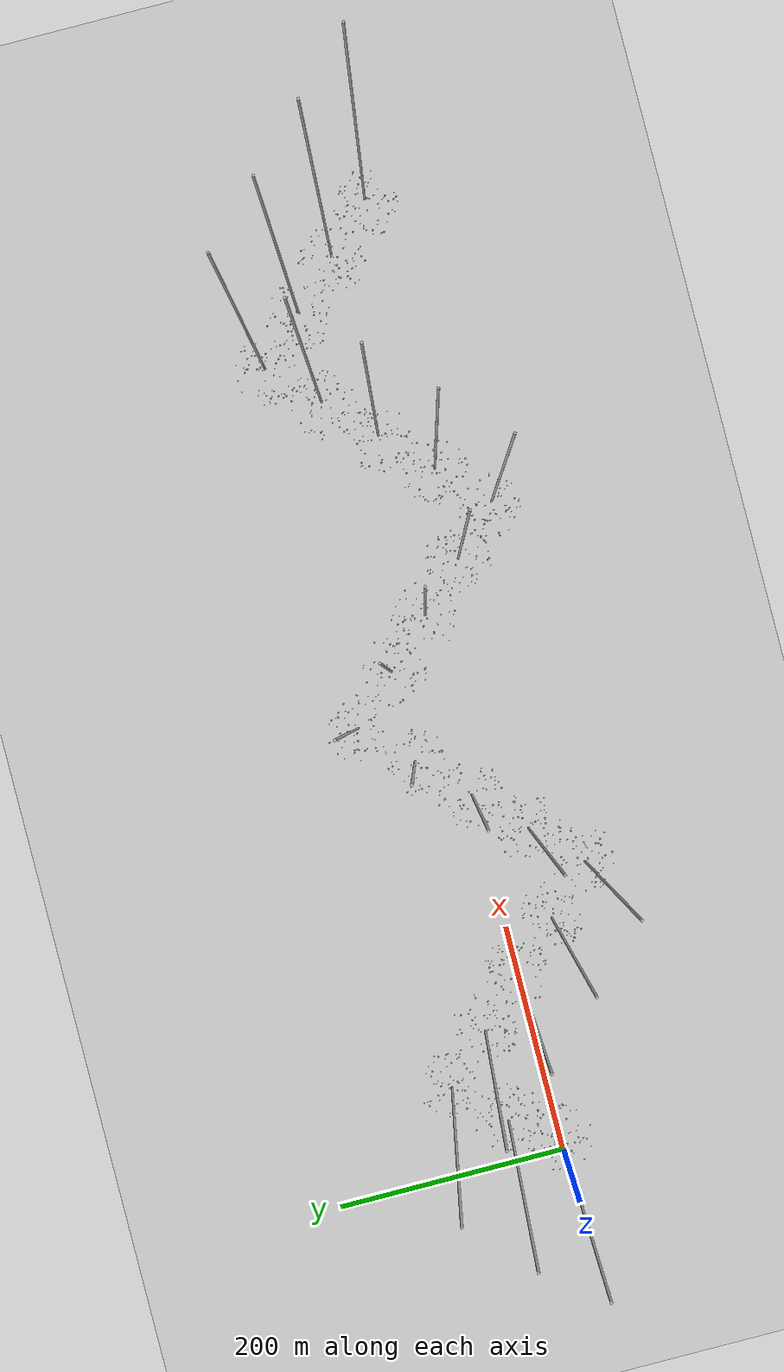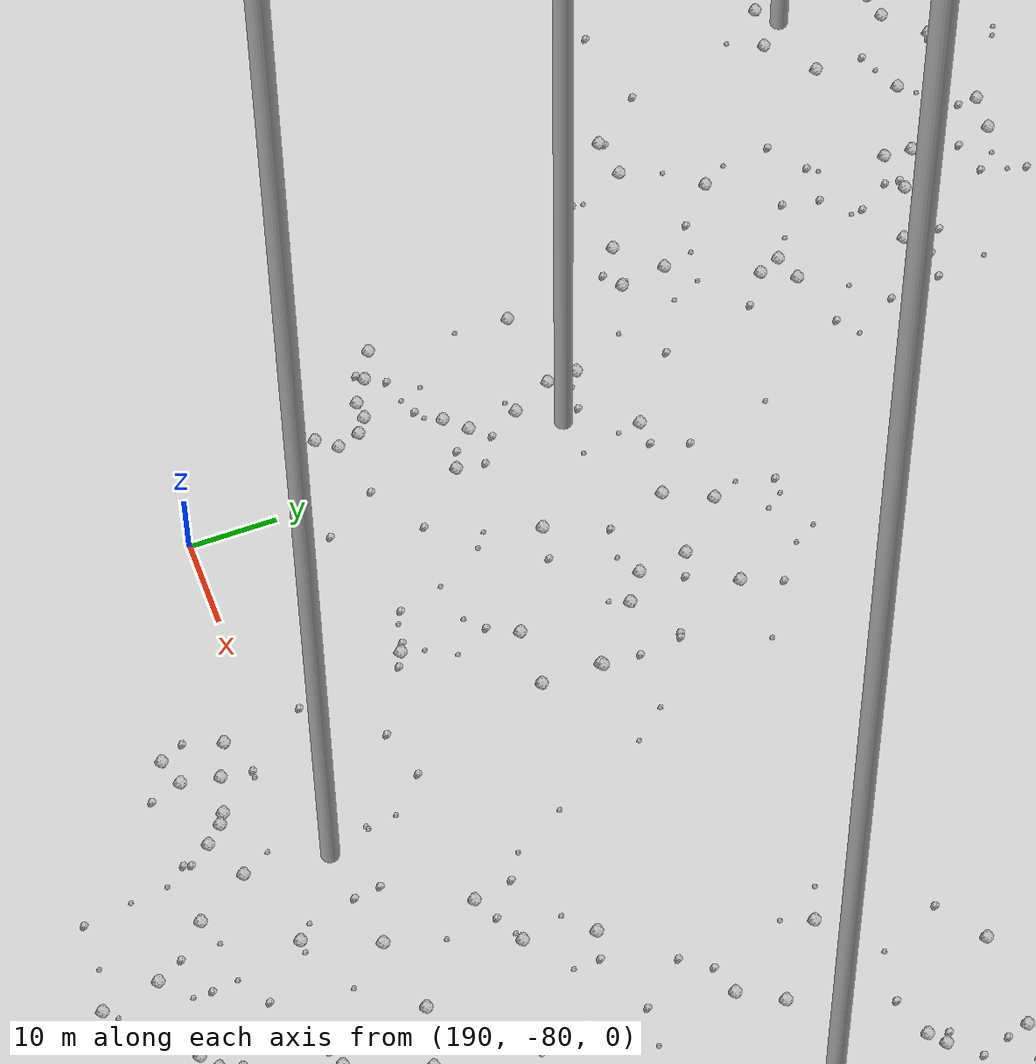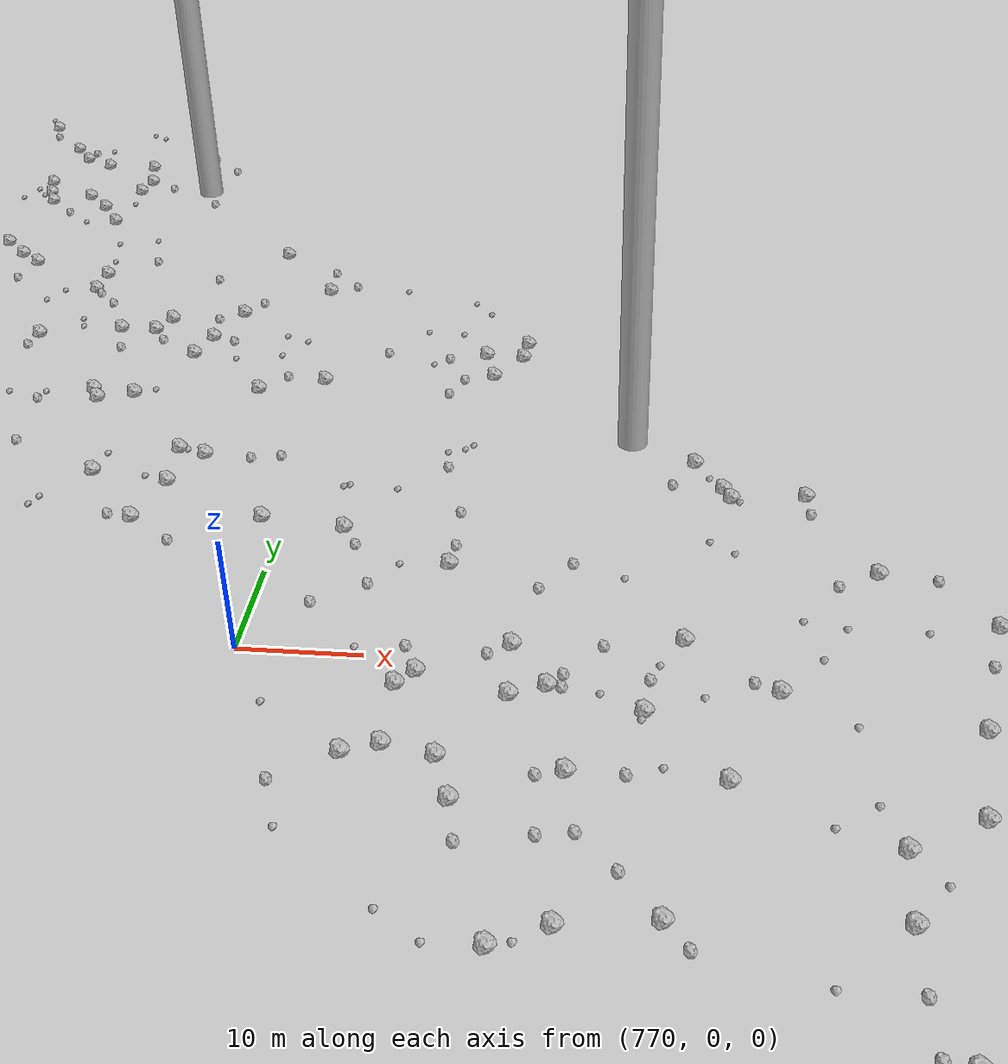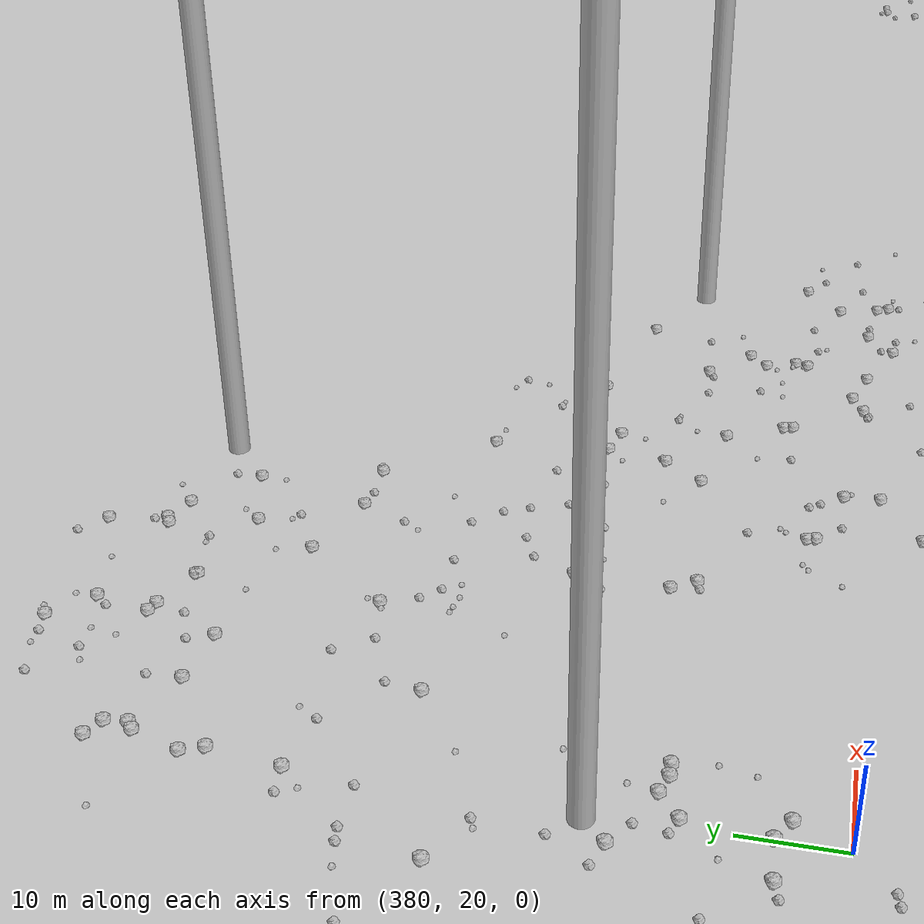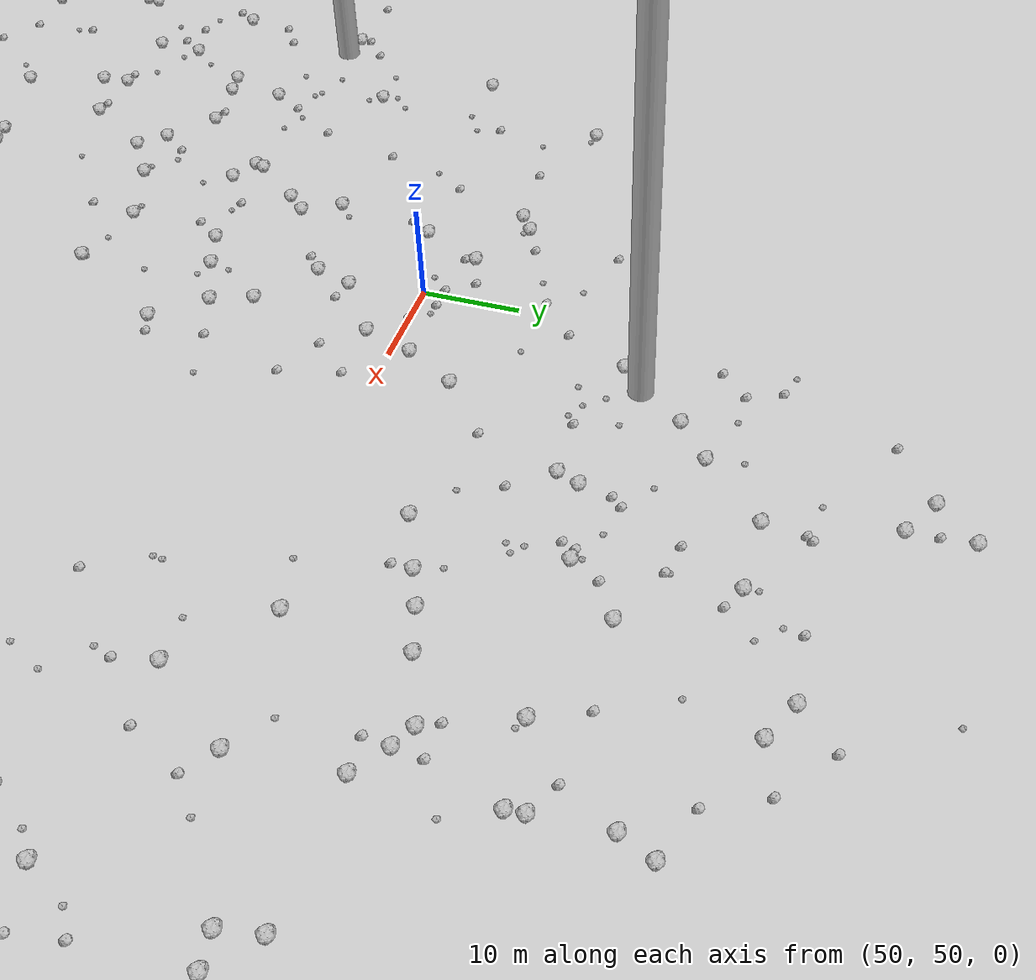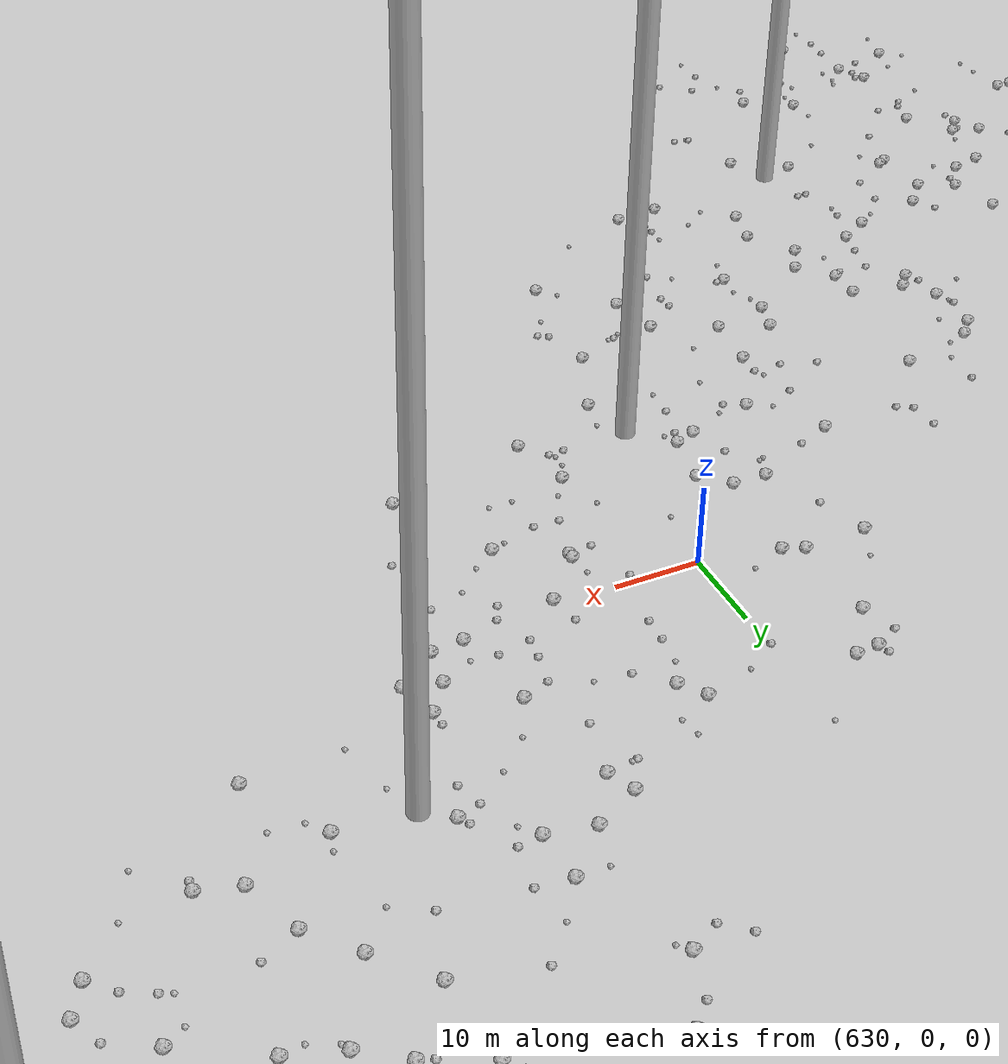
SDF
<sdf version="1.6">
 <world name="default">
  <include><uri>model://custom_ground</uri></include>
  <include><uri>model://sun</uri></include>
  <spherical_coordinates>
   <surface_model>EARTH_WGS84</surface_model>
   <latitude_deg>38.161479</latitude_deg>
   <longitude_deg>-122.454630</longitude_deg>
   <elevation>488.0</elevation>
   <heading_deg>90</heading_deg>
  </spherical_coordinates>
  <model name="rock1_0_0">
   <include><uri>model://rock1</uri><pose>-2.9324141354575097 -6.368236812320632 0.5 0 0 0</pose></include>
  </model>
  <model name="rock1_0_1">
   <include><uri>model://rock1</uri><pose>13.46610589667953 2.4398403298637845 0.5 0 0 0</pose></include>
  </model>
  <model name="rock1_0_2">
   <include><uri>model://rock1</uri><pose>20.34053255283797 20.99698691956157 0.5 0 0 0</pose></include>
  </model>
  <model name="rock1_0_3">
   <include><uri>model://rock1</uri><pose>5.2022583293776705 10.7854915841274 0.5 0 0 0</pose></include>
  </model>
  <model name="rock1_0_4">
   <include><uri>model://rock1</uri><pose>13.807694923434667 7.545383934660585 0.5 0 0 0</pose></include>
  </model>
  <model name="rock1_0_5">
   <include><uri>model://rock1</uri><pose>3.882870924408973 -4.257634271946809 0.5 0 0 0</pose></include>
  </model>
  <model name="rock1_0_6">
   <include><uri>model://rock1</uri><pose>-8.389569873573956 9.612759528949312 0.5 0 0 0</pose></include>
  </model>
  <model name="rock1_0_7">
   <include><uri>model://rock1</uri><pose>5.91481263053959 25.62177669870372 0.5 0 0 0</pose></include>
  </model>
  <model name="rock1_0_8">
   <include><uri>model://rock1</uri><pose>29.066266125253513 2.3659846462236658 0.5 0 0 0</pose></include>
  </model>
  <model name="rock1_0_9">
   <include><uri>model://rock1</uri><pose>18.15856218442294 14.715251476516194 0.5 0 0 0</pose></include>
  </model>
  <model name="rock1_0_10">
   <include><uri>model://rock1</uri><pose>35.48825071149271 -6.189548473605676 0.5 0 0 0</pose></include>
  </model>
  <model name="rock1_0_11">
   <include><uri>model://rock1</uri><pose>37.791730280886924 -5.878001931229068 0.5 0 0 0</pose></include>
  </model>
  <model name="rock1_0_12">
   <include><uri>model://rock1</uri><pose>37.489626567352694 -9.060976700686936 0.5 0 0 0</pose></include>
  </model>
  <model name="rock1_0_13">
   <include><uri>model://rock1</uri><pose>22.467034822884216 2.5062110923653407 0.5 0 0 0</pose></include>
  </model>
  <model name="rock1_0_14">
   <include><uri>model://rock1</uri><pose>25.06688469210004 -8.909779256055394 0.5 0 0 0</pose></include>
  </model>
  <model name="rock1_0_15">
   <include><uri>model://rock1</uri><pose>27.060633304240845 16.11708083216547 0.5 0 0 0</pose></include>
  </model>
  <model name="rock1_0_16">
   <include><uri>model://rock1</uri><pose>22.673257288895968 -0.4912072563856462 0.5 0 0 0</pose></include>
  </model>
  <model name="rock1_0_17">
   <include><uri>model://rock1</uri><pose>-14.720571240163167 13.097522298830306 0.5 0 0 0</pose></include>
  </model>
  <model name="rock1_0_18">
   <include><uri>model://rock1</uri><pose>5.652921043723843 -19.17207267172882 0.5 0 0 0</pose></include>
  </model>
  <model name="rock1_0_19">
   <include><uri>model://rock1</uri><pose>4.212767519009592 -21.939610942625166 0.5 0 0 0</pose></include>
  </model>
  <model name="rock1_0_20">
   <include><uri>model://rock1</uri><pose>7.025915366520991 -14.885467555257843 0.5 0 0 0</pose></include>
  </model>
  <model name="rock1_0_21">
   <include><uri>model://rock1</uri><pose>-14.95244829147186 -3.4588617004487006 0.5 0 0 0</pose></include>
  </model>
  <model name="rock1_0_22">
   <include><uri>model://rock1</uri><pose>20.796471267207245 15.248260672883916 0.5 0 0 0</pose></include>
  </model>
  <model name="rock1_0_23">
   <include><uri>model://rock1</uri><pose>34.141163504209956 9.836183012746282 0.5 0 0 0</pose></include>
  </model>
  <model name="rock1_0_24">
   <include><uri>model://rock1</uri><pose>3.469520152777868 -10.822815651152627 0.5 0 0 0</pose></include>
  </model>
  <model name="rock1_0_25">
   <include><uri>model://rock1</uri><pose>4.151924267984967 -2.7777814685930764 0.5 0 0 0</pose></include>
  </model>
  <model name="rock1_0_26">
   <include><uri>model://rock1</uri><pose>-15.675651259611762 7.624797963854576 0.5 0 0 0</pose></include>
  </model>
  <model name="rock2_0_0">
   <include><uri>model://rock2</uri><pose>8.56708330937509 17.73904087781232 0.3 0 0 0</pose></include>
  </model>
  <model name="rock2_0_1">
   <include><uri>model://rock2</uri><pose>-12.73490866337433 -15.363794722363357 0.3 0 0 0</pose></include>
  </model>
  <model name="rock2_0_2">
   <include><uri>model://rock2</uri><pose>11.795537241028732 4.987536789957886 0.3 0 0 0</pose></include>
  </model>
  <model name="rock2_0_3">
   <include><uri>model://rock2</uri><pose>17.406875028853335 -17.13469149350483 0.3 0 0 0</pose></include>
  </model>
  <model name="rock2_0_4">
   <include><uri>model://rock2</uri><pose>2.4194377632378092 -15.250667296753047 0.3 0 0 0</pose></include>
  </model>
  <model name="rock2_0_5">
   <include><uri>model://rock2</uri><pose>8.488345011271633 29.071413524012826 0.3 0 0 0</pose></include>
  </model>
  <model name="rock2_0_6">
   <include><uri>model://rock2</uri><pose>3.618254422430695 8.615480266341073 0.3 0 0 0</pose></include>
  </model>
  <model name="rock2_0_7">
   <include><uri>model://rock2</uri><pose>6.700646327570507 24.952146245609498 0.3 0 0 0</pose></include>
  </model>
  <model name="rock2_0_8">
   <include><uri>model://rock2</uri><pose>13.265486540809363 -14.503659107865888 0.3 0 0 0</pose></include>
  </model>
  <model name="rock2_0_9">
   <include><uri>model://rock2</uri><pose>22.19783005072634 24.23117611979469 0.3 0 0 0</pose></include>
  </model>
  <model name="rock2_0_10">
   <include><uri>model://rock2</uri><pose>-6.3711401505640435 13.38547749454824 0.3 0 0 0</pose></include>
  </model>
  <model name="rock2_0_11">
   <include><uri>model://rock2</uri><pose>5.67654307018244 26.77121354266624 0.3 0 0 0</pose></include>
  </model>
  <model name="rock2_0_12">
   <include><uri>model://rock2</uri><pose>36.30613639447473 -11.114217703448496 0.3 0 0 0</pose></include>
  </model>
  <model name="rock2_0_13">
   <include><uri>model://rock2</uri><pose>8.737260625918381 5.9770673258229365 0.3 0 0 0</pose></include>
  </model>
  <model name="rock2_0_14">
   <include><uri>model://rock2</uri><pose>3.603408200137295 -28.8995255031459 0.3 0 0 0</pose></include>
  </model>
  <model name="rock2_0_15">
   <include><uri>model://rock2</uri><pose>-12.779948892514465 2.0466476821020905 0.3 0 0 0</pose></include>
  </model>
  <model name="rock2_0_16">
   <include><uri>model://rock2</uri><pose>25.254088206401136 16.410387931614537 0.3 0 0 0</pose></include>
  </model>
  <model name="rock2_0_17">
   <include><uri>model://rock2</uri><pose>20.760701807275538 2.534882022445288 0.3 0 0 0</pose></include>
  </model>
  <model name="rock2_0_18">
   <include><uri>model://rock2</uri><pose>38.83498487604449 -7.837967504967406 0.3 0 0 0</pose></include>
  </model>
  <model name="rock2_0_19">
   <include><uri>model://rock2</uri><pose>12.64199049090223 -7.47627772629318 0.3 0 0 0</pose></include>
  </model>
  <model name="rock2_0_20">
   <include><uri>model://rock2</uri><pose>-5.285332718605929 -7.410247533426912 0.3 0 0 0</pose></include>
  </model>
  <model name="rock2_0_21">
   <include><uri>model://rock2</uri><pose>-2.2695544641724155 25.85945105974796 0.3 0 0 0</pose></include>
  </model>
  <model name="rock2_0_22">
   <include><uri>model://rock2</uri><pose>33.578110315664844 9.403591700333301 0.3 0 0 0</pose></include>
  </model>
  <model name="rock2_0_23">
   <include><uri>model://rock2</uri><pose>27.371622589726485 2.4908124234455826 0.3 0 0 0</pose></include>
  </model>
  <model name="rock2_0_24">
   <include><uri>model://rock2</uri><pose>5.741670624189176 15.836641174411483 0.3 0 0 0</pose></include>
  </model>
  <model name="rock2_0_25">
   <include><uri>model://rock2</uri><pose>14.801483288739597 -27.608426739981617 0.3 0 0 0</pose></include>
  </model>
  <model name="rock2_0_26">
   <include><uri>model://rock2</uri><pose>31.191121601790194 -13.807028844668771 0.3 0 0 0</pose></include>
  </model>
  <model name="rock3_0_0">
   <include><uri>model://rock3</uri><pose>15.221424498030053 6.225143285999664 0.2 0 0 0</pose></include>
  </model>
  <model name="rock3_0_1">
   <include><uri>model://rock3</uri><pose>-9.538513821511058 7.310590706947913 0.2 0 0 0</pose></include>
  </model>
  <model name="rock3_0_2">
   <include><uri>model://rock3</uri><pose>18.120842651205713 25.48493869486724 0.2 0 0 0</pose></include>
  </model>
  <model name="rock3_0_3">
   <include><uri>model://rock3</uri><pose>37.79471746176245 4.824640972387897 0.2 0 0 0</pose></include>
  </model>
  <model name="rock3_0_4">
   <include><uri>model://rock3</uri><pose>-13.690207615545484 -3.3954374056214895 0.2 0 0 0</pose></include>
  </model>
  <model name="rock3_0_5">
   <include><uri>model://rock3</uri><pose>19.279533552422834 4.6988335110949535 0.2 0 0 0</pose></include>
  </model>
  <model name="rock3_0_6">
   <include><uri>model://rock3</uri><pose>-7.849259238556668 -18.288692682406293 0.2 0 0 0</pose></include>
  </model>
  <model name="rock3_0_7">
   <include><uri>model://rock3</uri><pose>-10.964135106389858 1.5007230197050276 0.2 0 0 0</pose></include>
  </model>
  <model name="rock3_0_8">
   <include><uri>model://rock3</uri><pose>30.488881406057608 -19.262697589713262 0.2 0 0 0</pose></include>
  </model>
  <model name="rock3_0_9">
   <include><uri>model://rock3</uri><pose>8.761870356711345 2.6034370426198663 0.2 0 0 0</pose></include>
  </model>
  <model name="rock3_0_10">
   <include><uri>model://rock3</uri><pose>15.22158635747001 22.23393133342043 0.2 0 0 0</pose></include>
  </model>
  <model name="rock3_0_11">
   <include><uri>model://rock3</uri><pose>-3.99562852740171 11.392912643787646 0.2 0 0 0</pose></include>
  </model>
  <model name="rock3_0_12">
   <include><uri>model://rock3</uri><pose>1.5684197108279214 -19.162111756525007 0.2 0 0 0</pose></include>
  </model>
  <model name="rock3_0_13">
   <include><uri>model://rock3</uri><pose>22.18170550650013 -11.264823106256038 0.2 0 0 0</pose></include>
  </model>
  <model name="rock3_0_14">
   <include><uri>model://rock3</uri><pose>-0.6084842122051306 -15.395059354366579 0.2 0 0 0</pose></include>
  </model>
  <model name="rock3_0_15">
   <include><uri>model://rock3</uri><pose>30.91150978996361 -15.999022530333448 0.2 0 0 0</pose></include>
  </model>
  <model name="rock3_0_16">
   <include><uri>model://rock3</uri><pose>14.686261431396282 26.651534976308625 0.2 0 0 0</pose></include>
  </model>
  <model name="rock3_0_17">
   <include><uri>model://rock3</uri><pose>5.932429161006535 6.539220565273638 0.2 0 0 0</pose></include>
  </model>
  <model name="rock3_0_18">
   <include><uri>model://rock3</uri><pose>-3.509189755763966 -23.74419139764698 0.2 0 0 0</pose></include>
  </model>
  <model name="rock3_0_19">
   <include><uri>model://rock3</uri><pose>-4.916373049439143 8.136077528860383 0.2 0 0 0</pose></include>
  </model>
  <model name="rock3_0_20">
   <include><uri>model://rock3</uri><pose>2.181105333119561 -6.81557861238139 0.2 0 0 0</pose></include>
  </model>
  <model name="rock3_0_21">
   <include><uri>model://rock3</uri><pose>23.699676533580657 25.4156827611745 0.2 0 0 0</pose></include>
  </model>
  <model name="rock3_0_22">
   <include><uri>model://rock3</uri><pose>12.94953036758622 -9.211674538617778 0.2 0 0 0</pose></include>
  </model>
  <model name="rock3_0_23">
   <include><uri>model://rock3</uri><pose>15.892152006730342 10.073143696395036 0.2 0 0 0</pose></include>
  </model>
  <model name="rock3_0_24">
   <include><uri>model://rock3</uri><pose>26.282010902362664 24.248802230898796 0.2 0 0 0</pose></include>
  </model>
  <model name="rock3_0_25">
   <include><uri>model://rock3</uri><pose>3.1660500604936033 -16.27827254263422 0.2 0 0 0</pose></include>
  </model>
  <model name="rock3_0_26">
   <include><uri>model://rock3</uri><pose>5.340330569794798 -27.31067399067119 0.2 0 0 0</pose></include>
  </model>
  <model name="rock1_1_0">
   <include><uri>model://rock1</uri><pose>18.2905274595731 59.10230745749842 0.5 0 0 0</pose></include>
  </model>
  <model name="rock1_1_1">
   <include><uri>model://rock1</uri><pose>49.88637888358669 38.48679693743301 0.5 0 0 0</pose></include>
  </model>
  <model name="rock1_1_2">
   <include><uri>model://rock1</uri><pose>37.4201120021702 57.257268308372616 0.5 0 0 0</pose></include>
  </model>
  <model name="rock1_1_3">
   <include><uri>model://rock1</uri><pose>34.525085321475004 25.44672724628716 0.5 0 0 0</pose></include>
  </model>
  <model name="rock1_1_4">
   <include><uri>model://rock1</uri><pose>51.87257275963093 27.419560734093842 0.5 0 0 0</pose></include>
  </model>
  <model name="rock1_1_5">
   <include><uri>model://rock1</uri><pose>38.874260506549824 13.138861667485171 0.5 0 0 0</pose></include>
  </model>
  <model name="rock1_1_6">
   <include><uri>model://rock1</uri><pose>38.65771339722859 36.53093400454575 0.5 0 0 0</pose></include>
  </model>
  <model name="rock1_1_7">
   <include><uri>model://rock1</uri><pose>11.430526426270491 44.390903609527925 0.5 0 0 0</pose></include>
  </model>
  <model name="rock1_1_8">
   <include><uri>model://rock1</uri><pose>59.332493089397666 51.9736587681065 0.5 0 0 0</pose></include>
  </model>
  <model name="rock1_1_9">
   <include><uri>model://rock1</uri><pose>47.68021602225731 25.964607122062404 0.5 0 0 0</pose></include>
  </model>
  <model name="rock1_1_10">
   <include><uri>model://rock1</uri><pose>40.69442556637803 32.64548795279893 0.5 0 0 0</pose></include>
  </model>
  <model name="rock1_1_11">
   <include><uri>model://rock1</uri><pose>40.79243846416138 47.1280413815068 0.5 0 0 0</pose></include>
  </model>
  <model name="rock1_1_12">
   <include><uri>model://rock1</uri><pose>57.31154281287747 29.878862663358596 0.5 0 0 0</pose></include>
  </model>
  <model name="rock1_1_13">
   <include><uri>model://rock1</uri><pose>17.410745249489217 32.91003507958969 0.5 0 0 0</pose></include>
  </model>
  <model name="rock1_1_14">
   <include><uri>model://rock1</uri><pose>35.33235132181421 55.847559480990384 0.5 0 0 0</pose></include>
  </model>
  <model name="rock1_1_15">
   <include><uri>model://rock1</uri><pose>57.54445475259133 46.79284448214716 0.5 0 0 0</pose></include>
  </model>
  <model name="rock1_1_16">
   <include><uri>model://rock1</uri><pose>34.198015136362336 24.424787580195325 0.5 0 0 0</pose></include>
  </model>
  <model name="rock1_1_17">
   <include><uri>model://rock1</uri><pose>31.788516678869968 12.381872905955076 0.5 0 0 0</pose></include>
  </model>
  <model name="rock1_1_18">
   <include><uri>model://rock1</uri><pose>37.04182621239104 22.941273768072833 0.5 0 0 0</pose></include>
  </model>
  <model name="rock1_1_19">
   <include><uri>model://rock1</uri><pose>38.82027266205135 30.617435502751242 0.5 0 0 0</pose></include>
  </model>
  <model name="rock1_1_20">
   <include><uri>model://rock1</uri><pose>46.239027151955995 15.68422114179513 0.5 0 0 0</pose></include>
  </model>
  <model name="rock1_1_21">
   <include><uri>model://rock1</uri><pose>51.19198080945947 42.370605575870414 0.5 0 0 0</pose></include>
  </model>
  <model name="rock1_1_22">
   <include><uri>model://rock1</uri><pose>55.86673154568248 34.03224361499683 0.5 0 0 0</pose></include>
  </model>
  <model name="rock1_1_23">
   <include><uri>model://rock1</uri><pose>54.33209209995621 14.004378570986852 0.5 0 0 0</pose></include>
  </model>
  <model name="rock1_1_24">
   <include><uri>model://rock1</uri><pose>61.37357909480337 25.13701792830375 0.5 0 0 0</pose></include>
  </model>
  <model name="rock1_1_25">
   <include><uri>model://rock1</uri><pose>35.15300930088971 69.22528118367 0.5 0 0 0</pose></include>
  </model>
  <model name="rock1_1_26">
   <include><uri>model://rock1</uri><pose>43.83061988076292 53.41309580645747 0.5 0 0 0</pose></include>
  </model>
  <model name="rock2_1_0">
   <include><uri>model://rock2</uri><pose>60.50622649980082 43.10265006032404 0.3 0 0 0</pose></include>
  </model>
  <model name="rock2_1_1">
   <include><uri>model://rock2</uri><pose>25.96914546255746 29.55335370429385 0.3 0 0 0</pose></include>
  </model>
  <model name="rock2_1_2">
   <include><uri>model://rock2</uri><pose>39.22066753555005 44.865848823228994 0.3 0 0 0</pose></include>
  </model>
  <model name="rock2_1_3">
   <include><uri>model://rock2</uri><pose>40.5634046120952 58.88154646559142 0.3 0 0 0</pose></include>
  </model>
  <model name="rock2_1_4">
   <include><uri>model://rock2</uri><pose>27.447912771072048 55.2403980419255 0.3 0 0 0</pose></include>
  </model>
  <model name="rock2_1_5">
   <include><uri>model://rock2</uri><pose>51.818225772061226 52.04262858555984 0.3 0 0 0</pose></include>
  </model>
  <model name="rock2_1_6">
   <include><uri>model://rock2</uri><pose>45.56931130098894 23.245323520295873 0.3 0 0 0</pose></include>
  </model>
  <model name="rock2_1_7">
   <include><uri>model://rock2</uri><pose>53.38925688054833 41.81156102914798 0.3 0 0 0</pose></include>
  </model>
  <model name="rock2_1_8">
   <include><uri>model://rock2</uri><pose>43.91614541399373 52.35569882199018 0.3 0 0 0</pose></include>
  </model>
  <model name="rock2_1_9">
   <include><uri>model://rock2</uri><pose>20.04714454508963 48.26355924917953 0.3 0 0 0</pose></include>
  </model>
  <model name="rock2_1_10">
   <include><uri>model://rock2</uri><pose>45.51133401893597 10.52831651478808 0.3 0 0 0</pose></include>
  </model>
  <model name="rock2_1_11">
   <include><uri>model://rock2</uri><pose>63.88238688657307 46.79771184454612 0.3 0 0 0</pose></include>
  </model>
  <model name="rock2_1_12">
   <include><uri>model://rock2</uri><pose>48.51442953191753 62.52257856945749 0.3 0 0 0</pose></include>
  </model>
  <model name="rock2_1_13">
   <include><uri>model://rock2</uri><pose>32.24008629292856 47.648143846202004 0.3 0 0 0</pose></include>
  </model>
  <model name="rock2_1_14">
   <include><uri>model://rock2</uri><pose>41.23597346668526 25.89419123029566 0.3 0 0 0</pose></include>
  </model>
  <model name="rock2_1_15">
   <include><uri>model://rock2</uri><pose>28.42141827898603 38.34662706525661 0.3 0 0 0</pose></include>
  </model>
  <model name="rock2_1_16">
   <include><uri>model://rock2</uri><pose>52.62431822473149 66.06874388929694 0.3 0 0 0</pose></include>
  </model>
  <model name="rock2_1_17">
   <include><uri>model://rock2</uri><pose>63.446973283448976 25.95188348954196 0.3 0 0 0</pose></include>
  </model>
  <model name="rock2_1_18">
   <include><uri>model://rock2</uri><pose>54.27025030405546 50.020529649497924 0.3 0 0 0</pose></include>
  </model>
  <model name="rock2_1_19">
   <include><uri>model://rock2</uri><pose>47.48164393277132 54.728498023274966 0.3 0 0 0</pose></include>
  </model>
  <model name="rock2_1_20">
   <include><uri>model://rock2</uri><pose>39.59351768724715 67.56984694147702 0.3 0 0 0</pose></include>
  </model>
  <model name="rock2_1_21">
   <include><uri>model://rock2</uri><pose>65.30765028725301 40.751314996515475 0.3 0 0 0</pose></include>
  </model>
  <model name="rock2_1_22">
   <include><uri>model://rock2</uri><pose>49.333891092505205 52.06635075174027 0.3 0 0 0</pose></include>
  </model>
  <model name="rock2_1_23">
   <include><uri>model://rock2</uri><pose>47.8910992111485 36.85741545651587 0.3 0 0 0</pose></include>
  </model>
  <model name="rock2_1_24">
   <include><uri>model://rock2</uri><pose>38.38495583766255 30.578105098275774 0.3 0 0 0</pose></include>
  </model>
  <model name="rock2_1_25">
   <include><uri>model://rock2</uri><pose>62.354522230166246 31.696670913444038 0.3 0 0 0</pose></include>
  </model>
  <model name="rock2_1_26">
   <include><uri>model://rock2</uri><pose>33.80006835783227 15.145812034142633 0.3 0 0 0</pose></include>
  </model>
  <model name="rock3_1_0">
   <include><uri>model://rock3</uri><pose>40.20269993182324 37.88807890695274 0.2 0 0 0</pose></include>
  </model>
  <model name="rock3_1_1">
   <include><uri>model://rock3</uri><pose>18.01237183390152 44.084758153085716 0.2 0 0 0</pose></include>
  </model>
  <model name="rock3_1_2">
   <include><uri>model://rock3</uri><pose>16.70147702289546 34.463487381396504 0.2 0 0 0</pose></include>
  </model>
  <model name="rock3_1_3">
   <include><uri>model://rock3</uri><pose>53.698926092242694 26.74867894592702 0.2 0 0 0</pose></include>
  </model>
  <model name="rock3_1_4">
   <include><uri>model://rock3</uri><pose>19.376077420756054 58.748334474387576 0.2 0 0 0</pose></include>
  </model>
  <model name="rock3_1_5">
   <include><uri>model://rock3</uri><pose>21.68002421261609 53.80834020397526 0.2 0 0 0</pose></include>
  </model>
  <model name="rock3_1_6">
   <include><uri>model://rock3</uri><pose>44.549310571361644 15.724047268134315 0.2 0 0 0</pose></include>
  </model>
  <model name="rock3_1_7">
   <include><uri>model://rock3</uri><pose>20.6312427583869 45.61728950409292 0.2 0 0 0</pose></include>
  </model>
  <model name="rock3_1_8">
   <include><uri>model://rock3</uri><pose>45.319189601866896 61.14453805815399 0.2 0 0 0</pose></include>
  </model>
  <model name="rock3_1_9">
   <include><uri>model://rock3</uri><pose>35.465626170246225 15.48106238911938 0.2 0 0 0</pose></include>
  </model>
  <model name="rock3_1_10">
   <include><uri>model://rock3</uri><pose>18.930995521460808 24.949727942467845 0.2 0 0 0</pose></include>
  </model>
  <model name="rock3_1_11">
   <include><uri>model://rock3</uri><pose>38.748905794167044 20.13820603522796 0.2 0 0 0</pose></include>
  </model>
  <model name="rock3_1_12">
   <include><uri>model://rock3</uri><pose>12.54647436933103 32.618835073130015 0.2 0 0 0</pose></include>
  </model>
  <model name="rock3_1_13">
   <include><uri>model://rock3</uri><pose>52.204337277787104 29.509760807459635 0.2 0 0 0</pose></include>
  </model>
  <model name="rock3_1_14">
   <include><uri>model://rock3</uri><pose>54.12506184067016 14.365184514193011 0.2 0 0 0</pose></include>
  </model>
  <model name="rock3_1_15">
   <include><uri>model://rock3</uri><pose>42.603391861176554 25.363983387316082 0.2 0 0 0</pose></include>
  </model>
  <model name="rock3_1_16">
   <include><uri>model://rock3</uri><pose>54.47862246733479 21.14473933448372 0.2 0 0 0</pose></include>
  </model>
  <model name="rock3_1_17">
   <include><uri>model://rock3</uri><pose>29.908461634945244 44.36871787822103 0.2 0 0 0</pose></include>
  </model>
  <model name="rock3_1_18">
   <include><uri>model://rock3</uri><pose>47.50269348575131 50.260779430122895 0.2 0 0 0</pose></include>
  </model>
  <model name="rock3_1_19">
   <include><uri>model://rock3</uri><pose>37.828982706191425 56.67808815924367 0.2 0 0 0</pose></include>
  </model>
  <model name="rock3_1_20">
   <include><uri>model://rock3</uri><pose>18.052855559470764 31.40660557092133 0.2 0 0 0</pose></include>
  </model>
  <model name="rock3_1_21">
   <include><uri>model://rock3</uri><pose>50.63028114012504 14.987949671494768 0.2 0 0 0</pose></include>
  </model>
  <model name="rock3_1_22">
   <include><uri>model://rock3</uri><pose>45.72182773190425 65.52374150886925 0.2 0 0 0</pose></include>
  </model>
  <model name="rock3_1_23">
   <include><uri>model://rock3</uri><pose>53.0928470168791 51.84287023753203 0.2 0 0 0</pose></include>
  </model>
  <model name="rock3_1_24">
   <include><uri>model://rock3</uri><pose>67.6935338034428 33.135595927851895 0.2 0 0 0</pose></include>
  </model>
  <model name="rock3_1_25">
   <include><uri>model://rock3</uri><pose>37.489967477216126 13.311628919019832 0.2 0 0 0</pose></include>
  </model>
  <model name="rock3_1_26">
   <include><uri>model://rock3</uri><pose>18.471852880846573 36.06362092046392 0.2 0 0 0</pose></include>
  </model>
  <model name="rock1_2_0">
   <include><uri>model://rock1</uri><pose>105.79113399808077 78.53358145689683 0.5 0 0 0</pose></include>
  </model>
  <model name="rock1_2_1">
   <include><uri>model://rock1</uri><pose>94.38099511798708 93.9577143020945 0.5 0 0 0</pose></include>
  </model>
  <model name="rock1_2_2">
   <include><uri>model://rock1</uri><pose>86.23837759191241 79.77294675334049 0.5 0 0 0</pose></include>
  </model>
  <model name="rock1_2_3">
   <include><uri>model://rock1</uri><pose>106.98140570565764 88.63880334216816 0.5 0 0 0</pose></include>
  </model>
  <model name="rock1_2_4">
   <include><uri>model://rock1</uri><pose>92.77676543250428 53.29092274201198 0.5 0 0 0</pose></include>
  </model>
  <model name="rock1_2_5">
   <include><uri>model://rock1</uri><pose>105.90950729708926 76.85514862069324 0.5 0 0 0</pose></include>
  </model>
  <model name="rock1_2_6">
   <include><uri>model://rock1</uri><pose>62.53449895464707 57.193196731201226 0.5 0 0 0</pose></include>
  </model>
  <model name="rock1_2_7">
   <include><uri>model://rock1</uri><pose>79.79458057330865 59.63605428317319 0.5 0 0 0</pose></include>
  </model>
  <model name="rock1_2_8">
   <include><uri>model://rock1</uri><pose>61.83905727459626 79.4982646390287 0.5 0 0 0</pose></include>
  </model>
  <model name="rock1_2_9">
   <include><uri>model://rock1</uri><pose>80.88927220349302 74.54860331915233 0.5 0 0 0</pose></include>
  </model>
  <model name="rock1_2_10">
   <include><uri>model://rock1</uri><pose>97.56970680264243 75.9624610942402 0.5 0 0 0</pose></include>
  </model>
  <model name="rock1_2_11">
   <include><uri>model://rock1</uri><pose>100.68455012760063 68.01804373516583 0.5 0 0 0</pose></include>
  </model>
  <model name="rock1_2_12">
   <include><uri>model://rock1</uri><pose>71.17662903039906 70.44622925816122 0.5 0 0 0</pose></include>
  </model>
  <model name="rock1_2_13">
   <include><uri>model://rock1</uri><pose>105.44553257652714 85.34308360714986 0.5 0 0 0</pose></include>
  </model>
  <model name="rock1_2_14">
   <include><uri>model://rock1</uri><pose>89.44283670348167 63.82420530512164 0.5 0 0 0</pose></include>
  </model>
  <model name="rock1_2_15">
   <include><uri>model://rock1</uri><pose>65.81532564417886 103.42338446990993 0.5 0 0 0</pose></include>
  </model>
  <model name="rock1_2_16">
   <include><uri>model://rock1</uri><pose>102.96924999400156 66.9074838385664 0.5 0 0 0</pose></include>
  </model>
  <model name="rock1_2_17">
   <include><uri>model://rock1</uri><pose>69.79598784885685 101.24593384559459 0.5 0 0 0</pose></include>
  </model>
  <model name="rock1_2_18">
   <include><uri>model://rock1</uri><pose>72.20497548362364 89.13320905340859 0.5 0 0 0</pose></include>
  </model>
  <model name="rock1_2_19">
   <include><uri>model://rock1</uri><pose>72.13536159693862 72.7088177112457 0.5 0 0 0</pose></include>
  </model>
  <model name="rock1_2_20">
   <include><uri>model://rock1</uri><pose>93.99819949675113 65.29030260097443 0.5 0 0 0</pose></include>
  </model>
  <model name="rock1_2_21">
   <include><uri>model://rock1</uri><pose>85.60464695553048 62.170171583120435 0.5 0 0 0</pose></include>
  </model>
  <model name="rock1_2_22">
   <include><uri>model://rock1</uri><pose>55.837836467795555 72.51086059564282 0.5 0 0 0</pose></include>
  </model>
  <model name="rock1_2_23">
   <include><uri>model://rock1</uri><pose>90.4937693720977 95.7415491890919 0.5 0 0 0</pose></include>
  </model>
  <model name="rock1_2_24">
   <include><uri>model://rock1</uri><pose>69.56724101247053 107.43493004752736 0.5 0 0 0</pose></include>
  </model>
  <model name="rock1_2_25">
   <include><uri>model://rock1</uri><pose>65.9584210990176 82.7869043130124 0.5 0 0 0</pose></include>
  </model>
  <model name="rock1_2_26">
   <include><uri>model://rock1</uri><pose>80.04738264615774 89.2674443918279 0.5 0 0 0</pose></include>
  </model>
  <model name="rock2_2_0">
   <include><uri>model://rock2</uri><pose>72.5854065379167 93.2864304078534 0.3 0 0 0</pose></include>
  </model>
  <model name="rock2_2_1">
   <include><uri>model://rock2</uri><pose>72.69796889908582 75.96263603357994 0.3 0 0 0</pose></include>
  </model>
  <model name="rock2_2_2">
   <include><uri>model://rock2</uri><pose>74.0369155359146 66.53792887444713 0.3 0 0 0</pose></include>
  </model>
  <model name="rock2_2_3">
   <include><uri>model://rock2</uri><pose>76.73598840210218 83.2007486017272 0.3 0 0 0</pose></include>
  </model>
  <model name="rock2_2_4">
   <include><uri>model://rock2</uri><pose>59.68571761857922 99.1958762606345 0.3 0 0 0</pose></include>
  </model>
  <model name="rock2_2_5">
   <include><uri>model://rock2</uri><pose>73.69172313529694 77.07751183425448 0.3 0 0 0</pose></include>
  </model>
  <model name="rock2_2_6">
   <include><uri>model://rock2</uri><pose>82.45851446295397 77.54521033524185 0.3 0 0 0</pose></include>
  </model>
  <model name="rock2_2_7">
   <include><uri>model://rock2</uri><pose>82.31272558267432 88.17750596520965 0.3 0 0 0</pose></include>
  </model>
  <model name="rock2_2_8">
   <include><uri>model://rock2</uri><pose>56.72867342495509 84.6078654484124 0.3 0 0 0</pose></include>
  </model>
  <model name="rock2_2_9">
   <include><uri>model://rock2</uri><pose>79.55994917394801 74.61760304355234 0.3 0 0 0</pose></include>
  </model>
  <model name="rock2_2_10">
   <include><uri>model://rock2</uri><pose>64.67575321473055 70.04777364989445 0.3 0 0 0</pose></include>
  </model>
  <model name="rock2_2_11">
   <include><uri>model://rock2</uri><pose>54.04423288240453 81.77933134809159 0.3 0 0 0</pose></include>
  </model>
  <model name="rock2_2_12">
   <include><uri>model://rock2</uri><pose>103.23959182637842 69.71129285627532 0.3 0 0 0</pose></include>
  </model>
  <model name="rock2_2_13">
   <include><uri>model://rock2</uri><pose>69.63092707761265 104.26976935779433 0.3 0 0 0</pose></include>
  </model>
  <model name="rock2_2_14">
   <include><uri>model://rock2</uri><pose>102.59152310530757 80.11016268112026 0.3 0 0 0</pose></include>
  </model>
  <model name="rock2_2_15">
   <include><uri>model://rock2</uri><pose>85.40508087398302 60.13078205662116 0.3 0 0 0</pose></include>
  </model>
  <model name="rock2_2_16">
   <include><uri>model://rock2</uri><pose>80.01313785948209 82.5835395077687 0.3 0 0 0</pose></include>
  </model>
  <model name="rock2_2_17">
   <include><uri>model://rock2</uri><pose>99.72802557585383 69.84859234838592 0.3 0 0 0</pose></include>
  </model>
  <model name="rock2_2_18">
   <include><uri>model://rock2</uri><pose>101.72384654197751 90.56814833258623 0.3 0 0 0</pose></include>
  </model>
  <model name="rock2_2_19">
   <include><uri>model://rock2</uri><pose>94.12933285917347 99.68088634221166 0.3 0 0 0</pose></include>
  </model>
  <model name="rock2_2_20">
   <include><uri>model://rock2</uri><pose>55.287004645026656 87.93504035307038 0.3 0 0 0</pose></include>
  </model>
  <model name="rock2_2_21">
   <include><uri>model://rock2</uri><pose>83.45811003061573 95.0920675382297 0.3 0 0 0</pose></include>
  </model>
  <model name="rock2_2_22">
   <include><uri>model://rock2</uri><pose>95.40695956632204 80.75320039005611 0.3 0 0 0</pose></include>
  </model>
  <model name="rock2_2_23">
   <include><uri>model://rock2</uri><pose>99.27341947297379 95.71962892233108 0.3 0 0 0</pose></include>
  </model>
  <model name="rock2_2_24">
   <include><uri>model://rock2</uri><pose>79.02551143461622 73.29433128596767 0.3 0 0 0</pose></include>
  </model>
  <model name="rock2_2_25">
   <include><uri>model://rock2</uri><pose>73.06969219620137 93.89941182494047 0.3 0 0 0</pose></include>
  </model>
  <model name="rock2_2_26">
   <include><uri>model://rock2</uri><pose>68.26584276706143 62.04366372920104 0.3 0 0 0</pose></include>
  </model>
  <model name="rock3_2_0">
   <include><uri>model://rock3</uri><pose>83.07764804220818 93.25019631568045 0.2 0 0 0</pose></include>
  </model>
  <model name="rock3_2_1">
   <include><uri>model://rock3</uri><pose>60.16206908239381 84.55273220134211 0.2 0 0 0</pose></include>
  </model>
  <model name="rock3_2_2">
   <include><uri>model://rock3</uri><pose>79.88183803851429 82.9949129501328 0.2 0 0 0</pose></include>
  </model>
  <model name="rock3_2_3">
   <include><uri>model://rock3</uri><pose>65.28330047310264 86.2720309574618 0.2 0 0 0</pose></include>
  </model>
  <model name="rock3_2_4">
   <include><uri>model://rock3</uri><pose>80.36653070776067 68.65679631487859 0.2 0 0 0</pose></include>
  </model>
  <model name="rock3_2_5">
   <include><uri>model://rock3</uri><pose>63.509776939035696 74.10796222443119 0.2 0 0 0</pose></include>
  </model>
  <model name="rock3_2_6">
   <include><uri>model://rock3</uri><pose>75.58888505423542 62.502957828495845 0.2 0 0 0</pose></include>
  </model>
  <model name="rock3_2_7">
   <include><uri>model://rock3</uri><pose>79.71990586314345 90.57184866724944 0.2 0 0 0</pose></include>
  </model>
  <model name="rock3_2_8">
   <include><uri>model://rock3</uri><pose>59.49422478986165 69.00141553896539 0.2 0 0 0</pose></include>
  </model>
  <model name="rock3_2_9">
   <include><uri>model://rock3</uri><pose>84.58237087423129 64.5550829196829 0.2 0 0 0</pose></include>
  </model>
  <model name="rock3_2_10">
   <include><uri>model://rock3</uri><pose>85.00685389742225 91.25505386443655 0.2 0 0 0</pose></include>
  </model>
  <model name="rock3_2_11">
   <include><uri>model://rock3</uri><pose>81.36340499816436 69.3633463172358 0.2 0 0 0</pose></include>
  </model>
  <model name="rock3_2_12">
   <include><uri>model://rock3</uri><pose>68.67409561847526 93.93514790375733 0.2 0 0 0</pose></include>
  </model>
  <model name="rock3_2_13">
   <include><uri>model://rock3</uri><pose>88.99106281973351 108.40433556922602 0.2 0 0 0</pose></include>
  </model>
  <model name="rock3_2_14">
   <include><uri>model://rock3</uri><pose>56.13319799326686 62.239873250368305 0.2 0 0 0</pose></include>
  </model>
  <model name="rock3_2_15">
   <include><uri>model://rock3</uri><pose>107.83150947700233 72.32394044123993 0.2 0 0 0</pose></include>
  </model>
  <model name="rock3_2_16">
   <include><uri>model://rock3</uri><pose>52.676871016806906 88.64475489325613 0.2 0 0 0</pose></include>
  </model>
  <model name="rock3_2_17">
   <include><uri>model://rock3</uri><pose>70.53063003726467 79.23457257121709 0.2 0 0 0</pose></include>
  </model>
  <model name="rock3_2_18">
   <include><uri>model://rock3</uri><pose>80.30230563883893 70.28549892909331 0.2 0 0 0</pose></include>
  </model>
  <model name="rock3_2_19">
   <include><uri>model://rock3</uri><pose>92.26934792755574 87.04847688763388 0.2 0 0 0</pose></include>
  </model>
  <model name="rock3_2_20">
   <include><uri>model://rock3</uri><pose>80.37114960091421 75.43650976837128 0.2 0 0 0</pose></include>
  </model>
  <model name="rock3_2_21">
   <include><uri>model://rock3</uri><pose>77.12580765330344 76.39265861975095 0.2 0 0 0</pose></include>
  </model>
  <model name="rock3_2_22">
   <include><uri>model://rock3</uri><pose>61.87240499438728 70.13602974572694 0.2 0 0 0</pose></include>
  </model>
  <model name="rock3_2_23">
   <include><uri>model://rock3</uri><pose>87.05047087822132 51.91151668219742 0.2 0 0 0</pose></include>
  </model>
  <model name="rock3_2_24">
   <include><uri>model://rock3</uri><pose>98.50018370371279 75.36800815486824 0.2 0 0 0</pose></include>
  </model>
  <model name="rock3_2_25">
   <include><uri>model://rock3</uri><pose>63.55351330282126 69.23913414691035 0.2 0 0 0</pose></include>
  </model>
  <model name="rock3_2_26">
   <include><uri>model://rock3</uri><pose>60.33465769928152 71.96439754187996 0.2 0 0 0</pose></include>
  </model>
  <model name="rock1_3_0">
   <include><uri>model://rock1</uri><pose>106.15887484441106 64.64882912324124 0.5 0 0 0</pose></include>
  </model>
  <model name="rock1_3_1">
   <include><uri>model://rock1</uri><pose>119.35797944951935 45.5062060865185 0.5 0 0 0</pose></include>
  </model>
  <model name="rock1_3_2">
   <include><uri>model://rock1</uri><pose>119.99042342747244 64.31839375894424 0.5 0 0 0</pose></include>
  </model>
  <model name="rock1_3_3">
   <include><uri>model://rock1</uri><pose>123.38513158163622 22.3475159616341 0.5 0 0 0</pose></include>
  </model>
  <model name="rock1_3_4">
   <include><uri>model://rock1</uri><pose>112.5379369673978 22.01695319954365 0.5 0 0 0</pose></include>
  </model>
  <model name="rock1_3_5">
   <include><uri>model://rock1</uri><pose>132.42302871743834 28.649422057209478 0.5 0 0 0</pose></include>
  </model>
  <model name="rock1_3_6">
   <include><uri>model://rock1</uri><pose>113.52134010198881 23.18360995387593 0.5 0 0 0</pose></include>
  </model>
  <model name="rock1_3_7">
   <include><uri>model://rock1</uri><pose>130.13114401707895 37.46037411572384 0.5 0 0 0</pose></include>
  </model>
  <model name="rock1_3_8">
   <include><uri>model://rock1</uri><pose>129.02150233850762 48.56912735472149 0.5 0 0 0</pose></include>
  </model>
  <model name="rock1_3_9">
   <include><uri>model://rock1</uri><pose>123.77003998973053 61.059395015673196 0.5 0 0 0</pose></include>
  </model>
  <model name="rock1_3_10">
   <include><uri>model://rock1</uri><pose>120.60058389974265 60.58404513602175 0.5 0 0 0</pose></include>
  </model>
  <model name="rock1_3_11">
   <include><uri>model://rock1</uri><pose>96.46987513795231 28.295568591701944 0.5 0 0 0</pose></include>
  </model>
  <model name="rock1_3_12">
   <include><uri>model://rock1</uri><pose>137.2573024025255 15.762643680538622 0.5 0 0 0</pose></include>
  </model>
  <model name="rock1_3_13">
   <include><uri>model://rock1</uri><pose>106.75614629137317 54.56731288447969 0.5 0 0 0</pose></include>
  </model>
  <model name="rock1_3_14">
   <include><uri>model://rock1</uri><pose>104.01484944136713 32.685841273441824 0.5 0 0 0</pose></include>
  </model>
  <model name="rock1_3_15">
   <include><uri>model://rock1</uri><pose>124.72613638227291 17.369908602777862 0.5 0 0 0</pose></include>
  </model>
  <model name="rock1_3_16">
   <include><uri>model://rock1</uri><pose>100.31170137359993 46.22054009571723 0.5 0 0 0</pose></include>
  </model>
  <model name="rock1_3_17">
   <include><uri>model://rock1</uri><pose>146.797986631284 41.273800227609286 0.5 0 0 0</pose></include>
  </model>
  <model name="rock1_3_18">
   <include><uri>model://rock1</uri><pose>111.3924418586347 23.921590247029545 0.5 0 0 0</pose></include>
  </model>
  <model name="rock1_3_19">
   <include><uri>model://rock1</uri><pose>100.22088601981338 19.83948980251808 0.5 0 0 0</pose></include>
  </model>
  <model name="rock1_3_20">
   <include><uri>model://rock1</uri><pose>138.2389839251723 48.05237803661244 0.5 0 0 0</pose></include>
  </model>
  <model name="rock1_3_21">
   <include><uri>model://rock1</uri><pose>98.90711743723915 18.904427234503558 0.5 0 0 0</pose></include>
  </model>
  <model name="rock1_3_22">
   <include><uri>model://rock1</uri><pose>141.24526999305016 31.470981082483586 0.5 0 0 0</pose></include>
  </model>
  <model name="rock1_3_23">
   <include><uri>model://rock1</uri><pose>95.40994345164052 24.112246097736627 0.5 0 0 0</pose></include>
  </model>
  <model name="rock1_3_24">
   <include><uri>model://rock1</uri><pose>117.54461124008371 27.066946679298447 0.5 0 0 0</pose></include>
  </model>
  <model name="rock1_3_25">
   <include><uri>model://rock1</uri><pose>114.44279750444306 39.743697587760906 0.5 0 0 0</pose></include>
  </model>
  <model name="rock1_3_26">
   <include><uri>model://rock1</uri><pose>135.7382397707857 57.1090953745898 0.5 0 0 0</pose></include>
  </model>
  <model name="rock2_3_0">
   <include><uri>model://rock2</uri><pose>130.54117732013873 45.50062730750543 0.3 0 0 0</pose></include>
  </model>
  <model name="rock2_3_1">
   <include><uri>model://rock2</uri><pose>110.01658712381192 15.319479446437924 0.3 0 0 0</pose></include>
  </model>
  <model name="rock2_3_2">
   <include><uri>model://rock2</uri><pose>118.25995100555954 13.336227827386256 0.3 0 0 0</pose></include>
  </model>
  <model name="rock2_3_3">
   <include><uri>model://rock2</uri><pose>109.55823617911324 52.461476310156954 0.3 0 0 0</pose></include>
  </model>
  <model name="rock2_3_4">
   <include><uri>model://rock2</uri><pose>117.336143695451 37.436757602835584 0.3 0 0 0</pose></include>
  </model>
  <model name="rock2_3_5">
   <include><uri>model://rock2</uri><pose>124.82072949486295 46.79864846126788 0.3 0 0 0</pose></include>
  </model>
  <model name="rock2_3_6">
   <include><uri>model://rock2</uri><pose>127.50900228705316 35.342975725390424 0.3 0 0 0</pose></include>
  </model>
  <model name="rock2_3_7">
   <include><uri>model://rock2</uri><pose>102.53703327989015 64.3722495054287 0.3 0 0 0</pose></include>
  </model>
  <model name="rock2_3_8">
   <include><uri>model://rock2</uri><pose>107.6859025359245 25.129349924512386 0.3 0 0 0</pose></include>
  </model>
  <model name="rock2_3_9">
   <include><uri>model://rock2</uri><pose>100.97836412457062 42.273028081052104 0.3 0 0 0</pose></include>
  </model>
  <model name="rock2_3_10">
   <include><uri>model://rock2</uri><pose>127.86400378577207 28.76711616341687 0.3 0 0 0</pose></include>
  </model>
  <model name="rock2_3_11">
   <include><uri>model://rock2</uri><pose>99.94621700774687 20.466855114820273 0.3 0 0 0</pose></include>
  </model>
  <model name="rock2_3_12">
   <include><uri>model://rock2</uri><pose>131.69868188010167 26.25698275482688 0.3 0 0 0</pose></include>
  </model>
  <model name="rock2_3_13">
   <include><uri>model://rock2</uri><pose>124.08950599444313 51.22679214645093 0.3 0 0 0</pose></include>
  </model>
  <model name="rock2_3_14">
   <include><uri>model://rock2</uri><pose>134.9114500152534 50.39506339039101 0.3 0 0 0</pose></include>
  </model>
  <model name="rock2_3_15">
   <include><uri>model://rock2</uri><pose>106.57842737939899 46.93782050983882 0.3 0 0 0</pose></include>
  </model>
  <model name="rock2_3_16">
   <include><uri>model://rock2</uri><pose>138.82942225690246 31.67294456863396 0.3 0 0 0</pose></include>
  </model>
  <model name="rock2_3_17">
   <include><uri>model://rock2</uri><pose>125.0463268976612 27.746223568531725 0.3 0 0 0</pose></include>
  </model>
  <model name="rock2_3_18">
   <include><uri>model://rock2</uri><pose>108.09433781677362 16.128285734960304 0.3 0 0 0</pose></include>
  </model>
  <model name="rock2_3_19">
   <include><uri>model://rock2</uri><pose>115.79079886436644 33.98590217730283 0.3 0 0 0</pose></include>
  </model>
  <model name="rock2_3_20">
   <include><uri>model://rock2</uri><pose>135.7087755707018 16.525457814968405 0.3 0 0 0</pose></include>
  </model>
  <model name="rock2_3_21">
   <include><uri>model://rock2</uri><pose>116.87462781763395 34.780983528553065 0.3 0 0 0</pose></include>
  </model>
  <model name="rock2_3_22">
   <include><uri>model://rock2</uri><pose>93.07252199113954 35.1148936019265 0.3 0 0 0</pose></include>
  </model>
  <model name="rock2_3_23">
   <include><uri>model://rock2</uri><pose>141.52897799560523 31.114569206697034 0.3 0 0 0</pose></include>
  </model>
  <model name="rock2_3_24">
   <include><uri>model://rock2</uri><pose>137.030907839534 62.89013840160856 0.3 0 0 0</pose></include>
  </model>
  <model name="rock2_3_25">
   <include><uri>model://rock2</uri><pose>98.9347249099622 23.635475421707973 0.3 0 0 0</pose></include>
  </model>
  <model name="rock2_3_26">
   <include><uri>model://rock2</uri><pose>136.7337762553754 26.96976127754166 0.3 0 0 0</pose></include>
  </model>
  <model name="rock3_3_0">
   <include><uri>model://rock3</uri><pose>112.70009437720184 55.008457993901665 0.2 0 0 0</pose></include>
  </model>
  <model name="rock3_3_1">
   <include><uri>model://rock3</uri><pose>101.70979543234506 33.63088056492785 0.2 0 0 0</pose></include>
  </model>
  <model name="rock3_3_2">
   <include><uri>model://rock3</uri><pose>129.5417700973882 32.517693755237104 0.2 0 0 0</pose></include>
  </model>
  <model name="rock3_3_3">
   <include><uri>model://rock3</uri><pose>123.12392271015585 68.88291881880635 0.2 0 0 0</pose></include>
  </model>
  <model name="rock3_3_4">
   <include><uri>model://rock3</uri><pose>112.2779016693494 14.178987422114966 0.2 0 0 0</pose></include>
  </model>
  <model name="rock3_3_5">
   <include><uri>model://rock3</uri><pose>117.89531757135575 14.588106666119085 0.2 0 0 0</pose></include>
  </model>
  <model name="rock3_3_6">
   <include><uri>model://rock3</uri><pose>90.21240350712864 41.28858435396178 0.2 0 0 0</pose></include>
  </model>
  <model name="rock3_3_7">
   <include><uri>model://rock3</uri><pose>115.25741636369811 25.26156469165145 0.2 0 0 0</pose></include>
  </model>
  <model name="rock3_3_8">
   <include><uri>model://rock3</uri><pose>132.64720699556744 47.13911207667761 0.2 0 0 0</pose></include>
  </model>
  <model name="rock3_3_9">
   <include><uri>model://rock3</uri><pose>121.74452838410099 49.62549254797233 0.2 0 0 0</pose></include>
  </model>
  <model name="rock3_3_10">
   <include><uri>model://rock3</uri><pose>110.96601282740497 34.3076703529151 0.2 0 0 0</pose></include>
  </model>
  <model name="rock3_3_11">
   <include><uri>model://rock3</uri><pose>116.95174327435386 43.63942272165173 0.2 0 0 0</pose></include>
  </model>
  <model name="rock3_3_12">
   <include><uri>model://rock3</uri><pose>95.58818358968313 45.863466463427216 0.2 0 0 0</pose></include>
  </model>
  <model name="rock3_3_13">
   <include><uri>model://rock3</uri><pose>136.02422145157394 51.698234122361384 0.2 0 0 0</pose></include>
  </model>
  <model name="rock3_3_14">
   <include><uri>model://rock3</uri><pose>102.75585042347647 57.24351836214181 0.2 0 0 0</pose></include>
  </model>
  <model name="rock3_3_15">
   <include><uri>model://rock3</uri><pose>136.98458010907356 48.98119915621618 0.2 0 0 0</pose></include>
  </model>
  <model name="rock3_3_16">
   <include><uri>model://rock3</uri><pose>149.530724844903 41.532957184817334 0.2 0 0 0</pose></include>
  </model>
  <model name="rock3_3_17">
   <include><uri>model://rock3</uri><pose>100.2596912344717 40.331279963809976 0.2 0 0 0</pose></include>
  </model>
  <model name="rock3_3_18">
   <include><uri>model://rock3</uri><pose>103.57873740577288 37.195123661140556 0.2 0 0 0</pose></include>
  </model>
  <model name="rock3_3_19">
   <include><uri>model://rock3</uri><pose>122.9607802111774 37.2531475164498 0.2 0 0 0</pose></include>
  </model>
  <model name="rock3_3_20">
   <include><uri>model://rock3</uri><pose>109.56559556331699 20.66173964455381 0.2 0 0 0</pose></include>
  </model>
  <model name="rock3_3_21">
   <include><uri>model://rock3</uri><pose>108.17734212145791 14.126086036519453 0.2 0 0 0</pose></include>
  </model>
  <model name="rock3_3_22">
   <include><uri>model://rock3</uri><pose>102.8352740555697 31.59347318098383 0.2 0 0 0</pose></include>
  </model>
  <model name="rock3_3_23">
   <include><uri>model://rock3</uri><pose>129.70467169767423 67.17777714857647 0.2 0 0 0</pose></include>
  </model>
  <model name="rock3_3_24">
   <include><uri>model://rock3</uri><pose>90.10033164277262 40.38707119060667 0.2 0 0 0</pose></include>
  </model>
  <model name="rock3_3_25">
   <include><uri>model://rock3</uri><pose>125.43331292619635 36.16645051346969 0.2 0 0 0</pose></include>
  </model>
  <model name="rock3_3_26">
   <include><uri>model://rock3</uri><pose>118.82539514736197 30.955425176875224 0.2 0 0 0</pose></include>
  </model>
  <model name="rock1_4_0">
   <include><uri>model://rock1</uri><pose>156.40983064829427 -19.94691892518203 0.5 0 0 0</pose></include>
  </model>
  <model name="rock1_4_1">
   <include><uri>model://rock1</uri><pose>134.06989500054888 10.692925134269764 0.5 0 0 0</pose></include>
  </model>
  <model name="rock1_4_2">
   <include><uri>model://rock1</uri><pose>165.73951144337855 -10.469010858962633 0.5 0 0 0</pose></include>
  </model>
  <model name="rock1_4_3">
   <include><uri>model://rock1</uri><pose>174.38968685799475 -18.65021550856422 0.5 0 0 0</pose></include>
  </model>
  <model name="rock1_4_4">
   <include><uri>model://rock1</uri><pose>173.86314866748438 10.666024554903245 0.5 0 0 0</pose></include>
  </model>
  <model name="rock1_4_5">
   <include><uri>model://rock1</uri><pose>155.48554672715977 7.006566843376895 0.5 0 0 0</pose></include>
  </model>
  <model name="rock1_4_6">
   <include><uri>model://rock1</uri><pose>155.15994540721414 20.96969807688064 0.5 0 0 0</pose></include>
  </model>
  <model name="rock1_4_7">
   <include><uri>model://rock1</uri><pose>160.30084783056472 -25.195261123329274 0.5 0 0 0</pose></include>
  </model>
  <model name="rock1_4_8">
   <include><uri>model://rock1</uri><pose>165.39905143846588 22.846902833301364 0.5 0 0 0</pose></include>
  </model>
  <model name="rock1_4_9">
   <include><uri>model://rock1</uri><pose>148.05437270146334 16.16696936350617 0.5 0 0 0</pose></include>
  </model>
  <model name="rock1_4_10">
   <include><uri>model://rock1</uri><pose>134.08733786455534 -9.377568283922447 0.5 0 0 0</pose></include>
  </model>
  <model name="rock1_4_11">
   <include><uri>model://rock1</uri><pose>175.07283545072332 -23.97997254689576 0.5 0 0 0</pose></include>
  </model>
  <model name="rock1_4_12">
   <include><uri>model://rock1</uri><pose>160.85131388029458 14.905669246920937 0.5 0 0 0</pose></include>
  </model>
  <model name="rock1_4_13">
   <include><uri>model://rock1</uri><pose>180.8137642369598 -5.068028627270728 0.5 0 0 0</pose></include>
  </model>
  <model name="rock1_4_14">
   <include><uri>model://rock1</uri><pose>170.08216798590442 -23.24674467960375 0.5 0 0 0</pose></include>
  </model>
  <model name="rock1_4_15">
   <include><uri>model://rock1</uri><pose>180.03541442232097 8.09331465673715 0.5 0 0 0</pose></include>
  </model>
  <model name="rock1_4_16">
   <include><uri>model://rock1</uri><pose>150.41094074285792 2.546189792941057 0.5 0 0 0</pose></include>
  </model>
  <model name="rock1_4_17">
   <include><uri>model://rock1</uri><pose>163.25342386598027 -25.95853516594597 0.5 0 0 0</pose></include>
  </model>
  <model name="rock1_4_18">
   <include><uri>model://rock1</uri><pose>169.30038337765757 13.308501030788989 0.5 0 0 0</pose></include>
  </model>
  <model name="rock1_4_19">
   <include><uri>model://rock1</uri><pose>169.5019485698441 22.61482106583292 0.5 0 0 0</pose></include>
  </model>
  <model name="rock1_4_20">
   <include><uri>model://rock1</uri><pose>177.7376146046082 -6.20747291403654 0.5 0 0 0</pose></include>
  </model>
  <model name="rock1_4_21">
   <include><uri>model://rock1</uri><pose>160.9605799727467 -19.129102833545616 0.5 0 0 0</pose></include>
  </model>
  <model name="rock1_4_22">
   <include><uri>model://rock1</uri><pose>178.83788457274056 -8.739121861535914 0.5 0 0 0</pose></include>
  </model>
  <model name="rock1_4_23">
   <include><uri>model://rock1</uri><pose>145.4701741429324 3.314226808160228 0.5 0 0 0</pose></include>
  </model>
  <model name="rock1_4_24">
   <include><uri>model://rock1</uri><pose>169.12029178385745 10.04115196472118 0.5 0 0 0</pose></include>
  </model>
  <model name="rock1_4_25">
   <include><uri>model://rock1</uri><pose>151.0848312784819 16.77094082658779 0.5 0 0 0</pose></include>
  </model>
  <model name="rock1_4_26">
   <include><uri>model://rock1</uri><pose>133.58695422530195 -13.155899953156329 0.5 0 0 0</pose></include>
  </model>
  <model name="rock2_4_0">
   <include><uri>model://rock2</uri><pose>180.1967913962896 12.352465973990007 0.3 0 0 0</pose></include>
  </model>
  <model name="rock2_4_1">
   <include><uri>model://rock2</uri><pose>187.49456100377444 -2.929942447918272 0.3 0 0 0</pose></include>
  </model>
  <model name="rock2_4_2">
   <include><uri>model://rock2</uri><pose>155.65298863571627 12.598040292099519 0.3 0 0 0</pose></include>
  </model>
  <model name="rock2_4_3">
   <include><uri>model://rock2</uri><pose>139.43302091618958 -1.1144112597480351 0.3 0 0 0</pose></include>
  </model>
  <model name="rock2_4_4">
   <include><uri>model://rock2</uri><pose>156.70145947634614 -19.332881831185635 0.3 0 0 0</pose></include>
  </model>
  <model name="rock2_4_5">
   <include><uri>model://rock2</uri><pose>165.43115589808107 20.622882228531076 0.3 0 0 0</pose></include>
  </model>
  <model name="rock2_4_6">
   <include><uri>model://rock2</uri><pose>186.8830414586293 3.9250022057131346 0.3 0 0 0</pose></include>
  </model>
  <model name="rock2_4_7">
   <include><uri>model://rock2</uri><pose>151.7422690750155 -14.132349904095287 0.3 0 0 0</pose></include>
  </model>
  <model name="rock2_4_8">
   <include><uri>model://rock2</uri><pose>174.45935406352984 19.715691156326983 0.3 0 0 0</pose></include>
  </model>
  <model name="rock2_4_9">
   <include><uri>model://rock2</uri><pose>155.82570378155282 20.727187195137404 0.3 0 0 0</pose></include>
  </model>
  <model name="rock2_4_10">
   <include><uri>model://rock2</uri><pose>173.08771591922425 -25.54936001124753 0.3 0 0 0</pose></include>
  </model>
  <model name="rock2_4_11">
   <include><uri>model://rock2</uri><pose>142.38103148455107 -16.41361919079467 0.3 0 0 0</pose></include>
  </model>
  <model name="rock2_4_12">
   <include><uri>model://rock2</uri><pose>163.4342131622663 -2.020038858270624 0.3 0 0 0</pose></include>
  </model>
  <model name="rock2_4_13">
   <include><uri>model://rock2</uri><pose>167.55141605731464 1.1582600401212488 0.3 0 0 0</pose></include>
  </model>
  <model name="rock2_4_14">
   <include><uri>model://rock2</uri><pose>172.63347733681053 10.524939769900442 0.3 0 0 0</pose></include>
  </model>
  <model name="rock2_4_15">
   <include><uri>model://rock2</uri><pose>182.8330166403509 10.342447626679053 0.3 0 0 0</pose></include>
  </model>
  <model name="rock2_4_16">
   <include><uri>model://rock2</uri><pose>182.34052720471118 -11.358024598643418 0.3 0 0 0</pose></include>
  </model>
  <model name="rock2_4_17">
   <include><uri>model://rock2</uri><pose>171.18282369789904 -3.20021244525606 0.3 0 0 0</pose></include>
  </model>
  <model name="rock2_4_18">
   <include><uri>model://rock2</uri><pose>172.51321669941603 8.790562585552195 0.3 0 0 0</pose></include>
  </model>
  <model name="rock2_4_19">
   <include><uri>model://rock2</uri><pose>185.969984826678 9.977490210531855 0.3 0 0 0</pose></include>
  </model>
  <model name="rock2_4_20">
   <include><uri>model://rock2</uri><pose>172.0183354199488 1.0306525370241673 0.3 0 0 0</pose></include>
  </model>
  <model name="rock2_4_21">
   <include><uri>model://rock2</uri><pose>170.0003057133079 -14.424591736419142 0.3 0 0 0</pose></include>
  </model>
  <model name="rock2_4_22">
   <include><uri>model://rock2</uri><pose>170.56996400563006 18.598461954164883 0.3 0 0 0</pose></include>
  </model>
  <model name="rock2_4_23">
   <include><uri>model://rock2</uri><pose>133.05429497916202 -1.0770238505905354 0.3 0 0 0</pose></include>
  </model>
  <model name="rock2_4_24">
   <include><uri>model://rock2</uri><pose>174.85711541865533 5.11537716934491 0.3 0 0 0</pose></include>
  </model>
  <model name="rock2_4_25">
   <include><uri>model://rock2</uri><pose>175.8598695044989 24.80770840692729 0.3 0 0 0</pose></include>
  </model>
  <model name="rock2_4_26">
   <include><uri>model://rock2</uri><pose>163.3629630786278 -26.862416355523198 0.3 0 0 0</pose></include>
  </model>
  <model name="rock3_4_0">
   <include><uri>model://rock3</uri><pose>162.45035829571916 -14.444454247350196 0.2 0 0 0</pose></include>
  </model>
  <model name="rock3_4_1">
   <include><uri>model://rock3</uri><pose>143.25133352652728 -18.536951379270487 0.2 0 0 0</pose></include>
  </model>
  <model name="rock3_4_2">
   <include><uri>model://rock3</uri><pose>148.4537653600283 -1.3505418916533856 0.2 0 0 0</pose></include>
  </model>
  <model name="rock3_4_3">
   <include><uri>model://rock3</uri><pose>144.70494504456147 22.4503356215032 0.2 0 0 0</pose></include>
  </model>
  <model name="rock3_4_4">
   <include><uri>model://rock3</uri><pose>157.81336043692139 27.84400320258085 0.2 0 0 0</pose></include>
  </model>
  <model name="rock3_4_5">
   <include><uri>model://rock3</uri><pose>137.147338663731 13.158263171029283 0.2 0 0 0</pose></include>
  </model>
  <model name="rock3_4_6">
   <include><uri>model://rock3</uri><pose>168.2518905731803 2.3278817294589658 0.2 0 0 0</pose></include>
  </model>
  <model name="rock3_4_7">
   <include><uri>model://rock3</uri><pose>177.21420438194895 -15.737012295997845 0.2 0 0 0</pose></include>
  </model>
  <model name="rock3_4_8">
   <include><uri>model://rock3</uri><pose>175.23597091335049 22.63994021506867 0.2 0 0 0</pose></include>
  </model>
  <model name="rock3_4_9">
   <include><uri>model://rock3</uri><pose>157.71919796250606 13.45386731684119 0.2 0 0 0</pose></include>
  </model>
  <model name="rock3_4_10">
   <include><uri>model://rock3</uri><pose>183.59112378724586 0.07816568054167661 0.2 0 0 0</pose></include>
  </model>
  <model name="rock3_4_11">
   <include><uri>model://rock3</uri><pose>163.86379219632263 -7.6038923816203265 0.2 0 0 0</pose></include>
  </model>
  <model name="rock3_4_12">
   <include><uri>model://rock3</uri><pose>156.65924842500982 28.40778003940789 0.2 0 0 0</pose></include>
  </model>
  <model name="rock3_4_13">
   <include><uri>model://rock3</uri><pose>173.4100259408777 -15.083418695659727 0.2 0 0 0</pose></include>
  </model>
  <model name="rock3_4_14">
   <include><uri>model://rock3</uri><pose>162.15447979614657 16.704148902232305 0.2 0 0 0</pose></include>
  </model>
  <model name="rock3_4_15">
   <include><uri>model://rock3</uri><pose>189.81475889686516 -1.0661162950508718 0.2 0 0 0</pose></include>
  </model>
  <model name="rock3_4_16">
   <include><uri>model://rock3</uri><pose>185.0530417386106 15.839765804563626 0.2 0 0 0</pose></include>
  </model>
  <model name="rock3_4_17">
   <include><uri>model://rock3</uri><pose>175.25072324082257 -4.466099307517723 0.2 0 0 0</pose></include>
  </model>
  <model name="rock3_4_18">
   <include><uri>model://rock3</uri><pose>163.2851663469658 -24.323778099584175 0.2 0 0 0</pose></include>
  </model>
  <model name="rock3_4_19">
   <include><uri>model://rock3</uri><pose>172.63526585290555 21.81004023627758 0.2 0 0 0</pose></include>
  </model>
  <model name="rock3_4_20">
   <include><uri>model://rock3</uri><pose>132.44624439184614 -6.562951560858458 0.2 0 0 0</pose></include>
  </model>
  <model name="rock3_4_21">
   <include><uri>model://rock3</uri><pose>174.9060726735116 3.747163575679906 0.2 0 0 0</pose></include>
  </model>
  <model name="rock3_4_22">
   <include><uri>model://rock3</uri><pose>186.76757712133144 8.101238049789792 0.2 0 0 0</pose></include>
  </model>
  <model name="rock3_4_23">
   <include><uri>model://rock3</uri><pose>174.43454719419225 -23.33010551681913 0.2 0 0 0</pose></include>
  </model>
  <model name="rock3_4_24">
   <include><uri>model://rock3</uri><pose>132.01823399278874 -0.7325535888627286 0.2 0 0 0</pose></include>
  </model>
  <model name="rock3_4_25">
   <include><uri>model://rock3</uri><pose>144.06113329711962 10.090644852316224 0.2 0 0 0</pose></include>
  </model>
  <model name="rock3_4_26">
   <include><uri>model://rock3</uri><pose>135.1624823035718 7.9213959824910845 0.2 0 0 0</pose></include>
  </model>
  <model name="rock1_5_0">
   <include><uri>model://rock1</uri><pose>186.35962155320274 -40.71542516849719 0.5 0 0 0</pose></include>
  </model>
  <model name="rock1_5_1">
   <include><uri>model://rock1</uri><pose>214.76227171364013 -24.85821757193 0.5 0 0 0</pose></include>
  </model>
  <model name="rock1_5_2">
   <include><uri>model://rock1</uri><pose>219.25147641914117 -42.730821242719045 0.5 0 0 0</pose></include>
  </model>
  <model name="rock1_5_3">
   <include><uri>model://rock1</uri><pose>176.72158761814546 -55.175188968418745 0.5 0 0 0</pose></include>
  </model>
  <model name="rock1_5_4">
   <include><uri>model://rock1</uri><pose>192.45831842145637 -28.271769635723075 0.5 0 0 0</pose></include>
  </model>
  <model name="rock1_5_5">
   <include><uri>model://rock1</uri><pose>204.13905986017693 -23.86899921972956 0.5 0 0 0</pose></include>
  </model>
  <model name="rock1_5_6">
   <include><uri>model://rock1</uri><pose>201.67920560495895 -29.104382607244638 0.5 0 0 0</pose></include>
  </model>
  <model name="rock1_5_7">
   <include><uri>model://rock1</uri><pose>183.09310052360024 -58.02165977699506 0.5 0 0 0</pose></include>
  </model>
  <model name="rock1_5_8">
   <include><uri>model://rock1</uri><pose>179.35905739599758 -56.975428409239846 0.5 0 0 0</pose></include>
  </model>
  <model name="rock1_5_9">
   <include><uri>model://rock1</uri><pose>201.23519901353825 -42.92629540736823 0.5 0 0 0</pose></include>
  </model>
  <model name="rock1_5_10">
   <include><uri>model://rock1</uri><pose>183.8022479765213 -32.64011960963869 0.5 0 0 0</pose></include>
  </model>
  <model name="rock1_5_11">
   <include><uri>model://rock1</uri><pose>210.52039914102352 -62.63982177866816 0.5 0 0 0</pose></include>
  </model>
  <model name="rock1_5_12">
   <include><uri>model://rock1</uri><pose>210.08887329208326 -34.85505437883371 0.5 0 0 0</pose></include>
  </model>
  <model name="rock1_5_13">
   <include><uri>model://rock1</uri><pose>173.4630040901718 -53.57496168172271 0.5 0 0 0</pose></include>
  </model>
  <model name="rock1_5_14">
   <include><uri>model://rock1</uri><pose>219.3444125188949 -49.55704286379789 0.5 0 0 0</pose></include>
  </model>
  <model name="rock1_5_15">
   <include><uri>model://rock1</uri><pose>174.81935250404143 -37.54108142999342 0.5 0 0 0</pose></include>
  </model>
  <model name="rock1_5_16">
   <include><uri>model://rock1</uri><pose>184.01878670813446 -36.11144277936075 0.5 0 0 0</pose></include>
  </model>
  <model name="rock1_5_17">
   <include><uri>model://rock1</uri><pose>186.6862603353294 -46.3665548471492 0.5 0 0 0</pose></include>
  </model>
  <model name="rock1_5_18">
   <include><uri>model://rock1</uri><pose>209.55669913578384 -29.25613961438348 0.5 0 0 0</pose></include>
  </model>
  <model name="rock1_5_19">
   <include><uri>model://rock1</uri><pose>182.30120214967093 -62.89737103218866 0.5 0 0 0</pose></include>
  </model>
  <model name="rock1_5_20">
   <include><uri>model://rock1</uri><pose>181.38475163338614 -56.80990100450601 0.5 0 0 0</pose></include>
  </model>
  <model name="rock1_5_21">
   <include><uri>model://rock1</uri><pose>184.59801573215998 -48.677873060245695 0.5 0 0 0</pose></include>
  </model>
  <model name="rock1_5_22">
   <include><uri>model://rock1</uri><pose>213.23378410562253 -37.09101014507466 0.5 0 0 0</pose></include>
  </model>
  <model name="rock1_5_23">
   <include><uri>model://rock1</uri><pose>190.98832932775713 -49.351837477988475 0.5 0 0 0</pose></include>
  </model>
  <model name="rock1_5_24">
   <include><uri>model://rock1</uri><pose>212.63614671701083 -49.6034109090798 0.5 0 0 0</pose></include>
  </model>
  <model name="rock1_5_25">
   <include><uri>model://rock1</uri><pose>183.94060237191087 -60.6696389896586 0.5 0 0 0</pose></include>
  </model>
  <model name="rock1_5_26">
   <include><uri>model://rock1</uri><pose>219.47006777746836 -42.55995104386833 0.5 0 0 0</pose></include>
  </model>
  <model name="rock2_5_0">
   <include><uri>model://rock2</uri><pose>209.4214170812733 -62.10981797255239 0.3 0 0 0</pose></include>
  </model>
  <model name="rock2_5_1">
   <include><uri>model://rock2</uri><pose>188.8710877160794 -48.562879623845845 0.3 0 0 0</pose></include>
  </model>
  <model name="rock2_5_2">
   <include><uri>model://rock2</uri><pose>175.89928183945636 -55.932714460278135 0.3 0 0 0</pose></include>
  </model>
  <model name="rock2_5_3">
   <include><uri>model://rock2</uri><pose>219.60443733502188 -38.263165962767445 0.3 0 0 0</pose></include>
  </model>
  <model name="rock2_5_4">
   <include><uri>model://rock2</uri><pose>182.53927910127203 -51.29999139474867 0.3 0 0 0</pose></include>
  </model>
  <model name="rock2_5_5">
   <include><uri>model://rock2</uri><pose>184.89274617263843 -22.332011879432976 0.3 0 0 0</pose></include>
  </model>
  <model name="rock2_5_6">
   <include><uri>model://rock2</uri><pose>205.6472384112463 -60.972787640494744 0.3 0 0 0</pose></include>
  </model>
  <model name="rock2_5_7">
   <include><uri>model://rock2</uri><pose>203.89808439842255 -35.95243099516529 0.3 0 0 0</pose></include>
  </model>
  <model name="rock2_5_8">
   <include><uri>model://rock2</uri><pose>177.8171692610522 -52.94667064721609 0.3 0 0 0</pose></include>
  </model>
  <model name="rock2_5_9">
   <include><uri>model://rock2</uri><pose>194.35055410345387 -65.19655599341112 0.3 0 0 0</pose></include>
  </model>
  <model name="rock2_5_10">
   <include><uri>model://rock2</uri><pose>190.48633153014825 -59.16436333345882 0.3 0 0 0</pose></include>
  </model>
  <model name="rock2_5_11">
   <include><uri>model://rock2</uri><pose>218.55984967724896 -33.254917185199375 0.3 0 0 0</pose></include>
  </model>
  <model name="rock2_5_12">
   <include><uri>model://rock2</uri><pose>212.25627663026378 -30.325601656698424 0.3 0 0 0</pose></include>
  </model>
  <model name="rock2_5_13">
   <include><uri>model://rock2</uri><pose>185.53395982621524 -33.91272935729429 0.3 0 0 0</pose></include>
  </model>
  <model name="rock2_5_14">
   <include><uri>model://rock2</uri><pose>195.2277671613428 -28.08435478810231 0.3 0 0 0</pose></include>
  </model>
  <model name="rock2_5_15">
   <include><uri>model://rock2</uri><pose>212.0540467773323 -63.410862800244765 0.3 0 0 0</pose></include>
  </model>
  <model name="rock2_5_16">
   <include><uri>model://rock2</uri><pose>182.81730908284013 -58.288320652717296 0.3 0 0 0</pose></include>
  </model>
  <model name="rock2_5_17">
   <include><uri>model://rock2</uri><pose>188.29694837785678 -34.05475376836166 0.3 0 0 0</pose></include>
  </model>
  <model name="rock2_5_18">
   <include><uri>model://rock2</uri><pose>188.3839042109442 -44.226285475730265 0.3 0 0 0</pose></include>
  </model>
  <model name="rock2_5_19">
   <include><uri>model://rock2</uri><pose>196.701148673882 -23.91954922454805 0.3 0 0 0</pose></include>
  </model>
  <model name="rock2_5_20">
   <include><uri>model://rock2</uri><pose>205.05720435897447 -43.56600880509647 0.3 0 0 0</pose></include>
  </model>
  <model name="rock2_5_21">
   <include><uri>model://rock2</uri><pose>219.0505551983945 -33.42829150639507 0.3 0 0 0</pose></include>
  </model>
  <model name="rock2_5_22">
   <include><uri>model://rock2</uri><pose>204.08636257899565 -16.668829704452214 0.3 0 0 0</pose></include>
  </model>
  <model name="rock2_5_23">
   <include><uri>model://rock2</uri><pose>196.67241065442226 -55.1152378397204 0.3 0 0 0</pose></include>
  </model>
  <model name="rock2_5_24">
   <include><uri>model://rock2</uri><pose>210.81702446775432 -52.935094404373274 0.3 0 0 0</pose></include>
  </model>
  <model name="rock2_5_25">
   <include><uri>model://rock2</uri><pose>191.38305849977635 -46.07580864305015 0.3 0 0 0</pose></include>
  </model>
  <model name="rock2_5_26">
   <include><uri>model://rock2</uri><pose>216.41018628849537 -20.34166354587461 0.3 0 0 0</pose></include>
  </model>
  <model name="rock3_5_0">
   <include><uri>model://rock3</uri><pose>180.55790773454737 -52.1822455473453 0.2 0 0 0</pose></include>
  </model>
  <model name="rock3_5_1">
   <include><uri>model://rock3</uri><pose>204.18284412835632 -55.84038903046659 0.2 0 0 0</pose></include>
  </model>
  <model name="rock3_5_2">
   <include><uri>model://rock3</uri><pose>179.63995768565067 -49.6390856659673 0.2 0 0 0</pose></include>
  </model>
  <model name="rock3_5_3">
   <include><uri>model://rock3</uri><pose>178.6675799072555 -19.051179351097346 0.2 0 0 0</pose></include>
  </model>
  <model name="rock3_5_4">
   <include><uri>model://rock3</uri><pose>211.009690404666 -60.08966410988972 0.2 0 0 0</pose></include>
  </model>
  <model name="rock3_5_5">
   <include><uri>model://rock3</uri><pose>193.77192052529654 -35.40843752529032 0.2 0 0 0</pose></include>
  </model>
  <model name="rock3_5_6">
   <include><uri>model://rock3</uri><pose>207.43029988159657 -36.479637488709116 0.2 0 0 0</pose></include>
  </model>
  <model name="rock3_5_7">
   <include><uri>model://rock3</uri><pose>205.9268323533196 -16.78492467688534 0.2 0 0 0</pose></include>
  </model>
  <model name="rock3_5_8">
   <include><uri>model://rock3</uri><pose>222.46866811488718 -24.088979709268706 0.2 0 0 0</pose></include>
  </model>
  <model name="rock3_5_9">
   <include><uri>model://rock3</uri><pose>201.05850078447293 -50.43527750706413 0.2 0 0 0</pose></include>
  </model>
  <model name="rock3_5_10">
   <include><uri>model://rock3</uri><pose>202.8823704666218 -20.904804864655105 0.2 0 0 0</pose></include>
  </model>
  <model name="rock3_5_11">
   <include><uri>model://rock3</uri><pose>183.51302420141974 -50.5188426167004 0.2 0 0 0</pose></include>
  </model>
  <model name="rock3_5_12">
   <include><uri>model://rock3</uri><pose>208.83459299037025 -54.84774561402736 0.2 0 0 0</pose></include>
  </model>
  <model name="rock3_5_13">
   <include><uri>model://rock3</uri><pose>207.00939458809654 -61.721175719339804 0.2 0 0 0</pose></include>
  </model>
  <model name="rock3_5_14">
   <include><uri>model://rock3</uri><pose>199.375226847614 -49.17083398775566 0.2 0 0 0</pose></include>
  </model>
  <model name="rock3_5_15">
   <include><uri>model://rock3</uri><pose>184.8044047345676 -41.44978719293239 0.2 0 0 0</pose></include>
  </model>
  <model name="rock3_5_16">
   <include><uri>model://rock3</uri><pose>180.6876194841717 -26.47071666473429 0.2 0 0 0</pose></include>
  </model>
  <model name="rock3_5_17">
   <include><uri>model://rock3</uri><pose>212.23957361555043 -39.26060938345296 0.2 0 0 0</pose></include>
  </model>
  <model name="rock3_5_18">
   <include><uri>model://rock3</uri><pose>194.42448329456528 -14.138487775032658 0.2 0 0 0</pose></include>
  </model>
  <model name="rock3_5_19">
   <include><uri>model://rock3</uri><pose>229.25069879289615 -42.014007275159145 0.2 0 0 0</pose></include>
  </model>
  <model name="rock3_5_20">
   <include><uri>model://rock3</uri><pose>207.28665232565896 -18.673122287503574 0.2 0 0 0</pose></include>
  </model>
  <model name="rock3_5_21">
   <include><uri>model://rock3</uri><pose>192.70915190376678 -30.91129525719421 0.2 0 0 0</pose></include>
  </model>
  <model name="rock3_5_22">
   <include><uri>model://rock3</uri><pose>210.90595986658045 -14.827359223847466 0.2 0 0 0</pose></include>
  </model>
  <model name="rock3_5_23">
   <include><uri>model://rock3</uri><pose>212.72716438036474 -56.856549528907834 0.2 0 0 0</pose></include>
  </model>
  <model name="rock3_5_24">
   <include><uri>model://rock3</uri><pose>212.3166626784552 -17.358744455380027 0.2 0 0 0</pose></include>
  </model>
  <model name="rock3_5_25">
   <include><uri>model://rock3</uri><pose>174.33098519610064 -43.68003112483871 0.2 0 0 0</pose></include>
  </model>
  <model name="rock3_5_26">
   <include><uri>model://rock3</uri><pose>226.2759305446061 -38.46867851440697 0.2 0 0 0</pose></include>
  </model>
  <model name="rock1_6_0">
   <include><uri>model://rock1</uri><pose>251.22703996016082 -94.22520025456976 0.5 0 0 0</pose></include>
  </model>
  <model name="rock1_6_1">
   <include><uri>model://rock1</uri><pose>218.21068529235995 -85.75547407573336 0.5 0 0 0</pose></include>
  </model>
  <model name="rock1_6_2">
   <include><uri>model://rock1</uri><pose>248.35090568448703 -97.99982180131296 0.5 0 0 0</pose></include>
  </model>
  <model name="rock1_6_3">
   <include><uri>model://rock1</uri><pose>257.78447788268033 -75.46182513580632 0.5 0 0 0</pose></include>
  </model>
  <model name="rock1_6_4">
   <include><uri>model://rock1</uri><pose>225.3649544280796 -89.51114587857751 0.5 0 0 0</pose></include>
  </model>
  <model name="rock1_6_5">
   <include><uri>model://rock1</uri><pose>238.77027206748403 -99.45620451514964 0.5 0 0 0</pose></include>
  </model>
  <model name="rock1_6_6">
   <include><uri>model://rock1</uri><pose>214.311073594842 -91.13197841466285 0.5 0 0 0</pose></include>
  </model>
  <model name="rock1_6_7">
   <include><uri>model://rock1</uri><pose>239.39451587943515 -83.89580221800628 0.5 0 0 0</pose></include>
  </model>
  <model name="rock1_6_8">
   <include><uri>model://rock1</uri><pose>233.67956942758715 -93.09265096929818 0.5 0 0 0</pose></include>
  </model>
  <model name="rock1_6_9">
   <include><uri>model://rock1</uri><pose>241.1966147844485 -65.04422714996915 0.5 0 0 0</pose></include>
  </model>
  <model name="rock1_6_10">
   <include><uri>model://rock1</uri><pose>242.61523764568366 -75.76237108300572 0.5 0 0 0</pose></include>
  </model>
  <model name="rock1_6_11">
   <include><uri>model://rock1</uri><pose>247.34494015654644 -61.81914212400346 0.5 0 0 0</pose></include>
  </model>
  <model name="rock1_6_12">
   <include><uri>model://rock1</uri><pose>253.73899463837367 -98.79760226234316 0.5 0 0 0</pose></include>
  </model>
  <model name="rock1_6_13">
   <include><uri>model://rock1</uri><pose>217.39180485881977 -90.03765708635208 0.5 0 0 0</pose></include>
  </model>
  <model name="rock1_6_14">
   <include><uri>model://rock1</uri><pose>250.2342881700812 -96.5189647419582 0.5 0 0 0</pose></include>
  </model>
  <model name="rock1_6_15">
   <include><uri>model://rock1</uri><pose>222.36008780926258 -86.8579308959122 0.5 0 0 0</pose></include>
  </model>
  <model name="rock1_6_16">
   <include><uri>model://rock1</uri><pose>266.96882194153187 -75.96655158653545 0.5 0 0 0</pose></include>
  </model>
  <model name="rock1_6_17">
   <include><uri>model://rock1</uri><pose>229.9825442633832 -87.09133005937642 0.5 0 0 0</pose></include>
  </model>
  <model name="rock1_6_18">
   <include><uri>model://rock1</uri><pose>251.1813697895657 -73.94027004341268 0.5 0 0 0</pose></include>
  </model>
  <model name="rock1_6_19">
   <include><uri>model://rock1</uri><pose>214.40292005364415 -84.13568498331814 0.5 0 0 0</pose></include>
  </model>
  <model name="rock1_6_20">
   <include><uri>model://rock1</uri><pose>260.3566766928087 -78.61056942723152 0.5 0 0 0</pose></include>
  </model>
  <model name="rock1_6_21">
   <include><uri>model://rock1</uri><pose>260.5955513350807 -70.69092381459208 0.5 0 0 0</pose></include>
  </model>
  <model name="rock1_6_22">
   <include><uri>model://rock1</uri><pose>249.05616564406284 -54.10904084565747 0.5 0 0 0</pose></include>
  </model>
  <model name="rock1_6_23">
   <include><uri>model://rock1</uri><pose>240.06318179103576 -106.03302699371555 0.5 0 0 0</pose></include>
  </model>
  <model name="rock1_6_24">
   <include><uri>model://rock1</uri><pose>254.4044423792841 -84.35434229068724 0.5 0 0 0</pose></include>
  </model>
  <model name="rock1_6_25">
   <include><uri>model://rock1</uri><pose>250.30735867715313 -84.84569153941273 0.5 0 0 0</pose></include>
  </model>
  <model name="rock1_6_26">
   <include><uri>model://rock1</uri><pose>223.5379287578698 -87.59391791075886 0.5 0 0 0</pose></include>
  </model>
  <model name="rock2_6_0">
   <include><uri>model://rock2</uri><pose>219.36930574346582 -67.31552219582669 0.3 0 0 0</pose></include>
  </model>
  <model name="rock2_6_1">
   <include><uri>model://rock2</uri><pose>260.1902604159267 -84.67936867757568 0.3 0 0 0</pose></include>
  </model>
  <model name="rock2_6_2">
   <include><uri>model://rock2</uri><pose>241.71151619699262 -94.44599340381474 0.3 0 0 0</pose></include>
  </model>
  <model name="rock2_6_3">
   <include><uri>model://rock2</uri><pose>258.46201597208324 -91.72661648360953 0.3 0 0 0</pose></include>
  </model>
  <model name="rock2_6_4">
   <include><uri>model://rock2</uri><pose>252.4489367632721 -76.87916739453004 0.3 0 0 0</pose></include>
  </model>
  <model name="rock2_6_5">
   <include><uri>model://rock2</uri><pose>258.8455947311494 -58.94145547902049 0.3 0 0 0</pose></include>
  </model>
  <model name="rock2_6_6">
   <include><uri>model://rock2</uri><pose>224.99908714002765 -65.72544372903984 0.3 0 0 0</pose></include>
  </model>
  <model name="rock2_6_7">
   <include><uri>model://rock2</uri><pose>258.04870017589263 -103.7698792691337 0.3 0 0 0</pose></include>
  </model>
  <model name="rock2_6_8">
   <include><uri>model://rock2</uri><pose>240.2691577624238 -60.57892494166462 0.3 0 0 0</pose></include>
  </model>
  <model name="rock2_6_9">
   <include><uri>model://rock2</uri><pose>261.8739152110564 -96.85591401313908 0.3 0 0 0</pose></include>
  </model>
  <model name="rock2_6_10">
   <include><uri>model://rock2</uri><pose>213.14202240886104 -75.16100226762127 0.3 0 0 0</pose></include>
  </model>
  <model name="rock2_6_11">
   <include><uri>model://rock2</uri><pose>229.8577687556485 -104.82196530244562 0.3 0 0 0</pose></include>
  </model>
  <model name="rock2_6_12">
   <include><uri>model://rock2</uri><pose>218.46125967205796 -93.6011024698548 0.3 0 0 0</pose></include>
  </model>
  <model name="rock2_6_13">
   <include><uri>model://rock2</uri><pose>236.58406363847192 -76.90701281719423 0.3 0 0 0</pose></include>
  </model>
  <model name="rock2_6_14">
   <include><uri>model://rock2</uri><pose>261.95515364587925 -64.86273060506056 0.3 0 0 0</pose></include>
  </model>
  <model name="rock2_6_15">
   <include><uri>model://rock2</uri><pose>226.7690177376054 -92.77143127674175 0.3 0 0 0</pose></include>
  </model>
  <model name="rock2_6_16">
   <include><uri>model://rock2</uri><pose>218.56936876052941 -82.25023567931052 0.3 0 0 0</pose></include>
  </model>
  <model name="rock2_6_17">
   <include><uri>model://rock2</uri><pose>252.15014988622366 -54.850114519437724 0.3 0 0 0</pose></include>
  </model>
  <model name="rock2_6_18">
   <include><uri>model://rock2</uri><pose>227.02486919251956 -91.9426820292101 0.3 0 0 0</pose></include>
  </model>
  <model name="rock2_6_19">
   <include><uri>model://rock2</uri><pose>252.47017598448613 -85.03741276041825 0.3 0 0 0</pose></include>
  </model>
  <model name="rock2_6_20">
   <include><uri>model://rock2</uri><pose>243.90871777721338 -63.48818299891663 0.3 0 0 0</pose></include>
  </model>
  <model name="rock2_6_21">
   <include><uri>model://rock2</uri><pose>244.93779469845944 -89.17325474614557 0.3 0 0 0</pose></include>
  </model>
  <model name="rock2_6_22">
   <include><uri>model://rock2</uri><pose>248.98749588578414 -86.09972092089716 0.3 0 0 0</pose></include>
  </model>
  <model name="rock2_6_23">
   <include><uri>model://rock2</uri><pose>237.13752454960044 -96.40978375415438 0.3 0 0 0</pose></include>
  </model>
  <model name="rock2_6_24">
   <include><uri>model://rock2</uri><pose>212.9701843050352 -88.40727100950821 0.3 0 0 0</pose></include>
  </model>
  <model name="rock2_6_25">
   <include><uri>model://rock2</uri><pose>269.2580307973173 -76.74288306165062 0.3 0 0 0</pose></include>
  </model>
  <model name="rock2_6_26">
   <include><uri>model://rock2</uri><pose>236.19808562910924 -73.90621184867362 0.3 0 0 0</pose></include>
  </model>
  <model name="rock3_6_0">
   <include><uri>model://rock3</uri><pose>268.5292701742512 -74.3989886595408 0.2 0 0 0</pose></include>
  </model>
  <model name="rock3_6_1">
   <include><uri>model://rock3</uri><pose>234.16003009235817 -52.91536817704481 0.2 0 0 0</pose></include>
  </model>
  <model name="rock3_6_2">
   <include><uri>model://rock3</uri><pose>228.2019830619818 -83.84273118870023 0.2 0 0 0</pose></include>
  </model>
  <model name="rock3_6_3">
   <include><uri>model://rock3</uri><pose>237.3744752597 -58.77863505193009 0.2 0 0 0</pose></include>
  </model>
  <model name="rock3_6_4">
   <include><uri>model://rock3</uri><pose>260.2344602124505 -64.33923063399939 0.2 0 0 0</pose></include>
  </model>
  <model name="rock3_6_5">
   <include><uri>model://rock3</uri><pose>245.94626805442374 -56.99784278518888 0.2 0 0 0</pose></include>
  </model>
  <model name="rock3_6_6">
   <include><uri>model://rock3</uri><pose>264.83529565100014 -79.75041641431989 0.2 0 0 0</pose></include>
  </model>
  <model name="rock3_6_7">
   <include><uri>model://rock3</uri><pose>240.70282843081637 -83.8308332390452 0.2 0 0 0</pose></include>
  </model>
  <model name="rock3_6_8">
   <include><uri>model://rock3</uri><pose>246.2271429122752 -62.20641053953697 0.2 0 0 0</pose></include>
  </model>
  <model name="rock3_6_9">
   <include><uri>model://rock3</uri><pose>262.9822382638458 -62.37828494334148 0.2 0 0 0</pose></include>
  </model>
  <model name="rock3_6_10">
   <include><uri>model://rock3</uri><pose>261.9411185533986 -65.4790565338993 0.2 0 0 0</pose></include>
  </model>
  <model name="rock3_6_11">
   <include><uri>model://rock3</uri><pose>229.30769209980912 -72.85967961793399 0.2 0 0 0</pose></include>
  </model>
  <model name="rock3_6_12">
   <include><uri>model://rock3</uri><pose>244.3596461804214 -69.29330247988494 0.2 0 0 0</pose></include>
  </model>
  <model name="rock3_6_13">
   <include><uri>model://rock3</uri><pose>241.636245837567 -96.57964895861214 0.2 0 0 0</pose></include>
  </model>
  <model name="rock3_6_14">
   <include><uri>model://rock3</uri><pose>241.31313015419153 -91.53889518957615 0.2 0 0 0</pose></include>
  </model>
  <model name="rock3_6_15">
   <include><uri>model://rock3</uri><pose>249.55497764496295 -85.19623232340619 0.2 0 0 0</pose></include>
  </model>
  <model name="rock3_6_16">
   <include><uri>model://rock3</uri><pose>235.15596804762936 -104.87307848299525 0.2 0 0 0</pose></include>
  </model>
  <model name="rock3_6_17">
   <include><uri>model://rock3</uri><pose>236.66691089005104 -91.94953818336519 0.2 0 0 0</pose></include>
  </model>
  <model name="rock3_6_18">
   <include><uri>model://rock3</uri><pose>241.1980689329077 -104.66821850963275 0.2 0 0 0</pose></include>
  </model>
  <model name="rock3_6_19">
   <include><uri>model://rock3</uri><pose>246.38769867655134 -80.36065561658457 0.2 0 0 0</pose></include>
  </model>
  <model name="rock3_6_20">
   <include><uri>model://rock3</uri><pose>228.9347347478282 -73.02215677229907 0.2 0 0 0</pose></include>
  </model>
  <model name="rock3_6_21">
   <include><uri>model://rock3</uri><pose>228.48531057721186 -95.14933944452413 0.2 0 0 0</pose></include>
  </model>
  <model name="rock3_6_22">
   <include><uri>model://rock3</uri><pose>219.31419825239493 -82.30490991618552 0.2 0 0 0</pose></include>
  </model>
  <model name="rock3_6_23">
   <include><uri>model://rock3</uri><pose>237.67327343580388 -82.33870314728526 0.2 0 0 0</pose></include>
  </model>
  <model name="rock3_6_24">
   <include><uri>model://rock3</uri><pose>252.2008195323461 -57.868373077036054 0.2 0 0 0</pose></include>
  </model>
  <model name="rock3_6_25">
   <include><uri>model://rock3</uri><pose>228.94108939672756 -99.34750402086742 0.2 0 0 0</pose></include>
  </model>
  <model name="rock3_6_26">
   <include><uri>model://rock3</uri><pose>228.75386235707333 -69.56517673493542 0.2 0 0 0</pose></include>
  </model>
  <model name="rock1_7_0">
   <include><uri>model://rock1</uri><pose>290.15694091553445 -34.3938271500141 0.5 0 0 0</pose></include>
  </model>
  <model name="rock1_7_1">
   <include><uri>model://rock1</uri><pose>288.40849084509244 -37.8018500086197 0.5 0 0 0</pose></include>
  </model>
  <model name="rock1_7_2">
   <include><uri>model://rock1</uri><pose>271.98972316565664 -25.62287761408325 0.5 0 0 0</pose></include>
  </model>
  <model name="rock1_7_3">
   <include><uri>model://rock1</uri><pose>260.660437957294 -42.86241061245767 0.5 0 0 0</pose></include>
  </model>
  <model name="rock1_7_4">
   <include><uri>model://rock1</uri><pose>282.58531412963873 -47.83767734500411 0.5 0 0 0</pose></include>
  </model>
  <model name="rock1_7_5">
   <include><uri>model://rock1</uri><pose>293.66753589266096 -22.274085494903275 0.5 0 0 0</pose></include>
  </model>
  <model name="rock1_7_6">
   <include><uri>model://rock1</uri><pose>255.71779495234276 -32.045012676765324 0.5 0 0 0</pose></include>
  </model>
  <model name="rock1_7_7">
   <include><uri>model://rock1</uri><pose>304.07149900523984 -34.67054014879256 0.5 0 0 0</pose></include>
  </model>
  <model name="rock1_7_8">
   <include><uri>model://rock1</uri><pose>275.17410732873043 -53.73267655924758 0.5 0 0 0</pose></include>
  </model>
  <model name="rock1_7_9">
   <include><uri>model://rock1</uri><pose>301.6614006430973 -54.65766491954075 0.5 0 0 0</pose></include>
  </model>
  <model name="rock1_7_10">
   <include><uri>model://rock1</uri><pose>278.7430933439459 -56.348603691534336 0.5 0 0 0</pose></include>
  </model>
  <model name="rock1_7_11">
   <include><uri>model://rock1</uri><pose>263.7983225038283 -15.650417023521662 0.5 0 0 0</pose></include>
  </model>
  <model name="rock1_7_12">
   <include><uri>model://rock1</uri><pose>274.5278297500888 -15.361286651067921 0.5 0 0 0</pose></include>
  </model>
  <model name="rock1_7_13">
   <include><uri>model://rock1</uri><pose>304.1306116346341 -34.039375106068576 0.5 0 0 0</pose></include>
  </model>
  <model name="rock1_7_14">
   <include><uri>model://rock1</uri><pose>290.4190259322728 -30.1164285342888 0.5 0 0 0</pose></include>
  </model>
  <model name="rock1_7_15">
   <include><uri>model://rock1</uri><pose>263.3119707414776 -38.163974416906655 0.5 0 0 0</pose></include>
  </model>
  <model name="rock1_7_16">
   <include><uri>model://rock1</uri><pose>273.640236634343 -24.152142304050393 0.5 0 0 0</pose></include>
  </model>
  <model name="rock1_7_17">
   <include><uri>model://rock1</uri><pose>281.5737351319014 -17.967288353283067 0.5 0 0 0</pose></include>
  </model>
  <model name="rock1_7_18">
   <include><uri>model://rock1</uri><pose>268.57360132376016 -65.55738203349885 0.5 0 0 0</pose></include>
  </model>
  <model name="rock1_7_19">
   <include><uri>model://rock1</uri><pose>297.8498079935517 -56.454436084895356 0.5 0 0 0</pose></include>
  </model>
  <model name="rock1_7_20">
   <include><uri>model://rock1</uri><pose>268.5429232168089 -52.83997605514607 0.5 0 0 0</pose></include>
  </model>
  <model name="rock1_7_21">
   <include><uri>model://rock1</uri><pose>276.8781231985324 -14.007122513503568 0.5 0 0 0</pose></include>
  </model>
  <model name="rock1_7_22">
   <include><uri>model://rock1</uri><pose>269.59433076142227 -55.90135151243699 0.5 0 0 0</pose></include>
  </model>
  <model name="rock1_7_23">
   <include><uri>model://rock1</uri><pose>283.67029080418996 -56.76282691610946 0.5 0 0 0</pose></include>
  </model>
  <model name="rock1_7_24">
   <include><uri>model://rock1</uri><pose>298.4702109369968 -39.621445532263785 0.5 0 0 0</pose></include>
  </model>
  <model name="rock1_7_25">
   <include><uri>model://rock1</uri><pose>300.74779402184606 -60.37528137224871 0.5 0 0 0</pose></include>
  </model>
  <model name="rock1_7_26">
   <include><uri>model://rock1</uri><pose>272.9893869674709 -66.40433364054427 0.5 0 0 0</pose></include>
  </model>
  <model name="rock2_7_0">
   <include><uri>model://rock2</uri><pose>290.06156177648654 -58.02499141456261 0.3 0 0 0</pose></include>
  </model>
  <model name="rock2_7_1">
   <include><uri>model://rock2</uri><pose>259.1183771846181 -52.109204104650715 0.3 0 0 0</pose></include>
  </model>
  <model name="rock2_7_2">
   <include><uri>model://rock2</uri><pose>272.5258687860104 -23.42670679246809 0.3 0 0 0</pose></include>
  </model>
  <model name="rock2_7_3">
   <include><uri>model://rock2</uri><pose>257.19316848079893 -43.934107197596646 0.3 0 0 0</pose></include>
  </model>
  <model name="rock2_7_4">
   <include><uri>model://rock2</uri><pose>271.63244644486736 -67.65974966633837 0.3 0 0 0</pose></include>
  </model>
  <model name="rock2_7_5">
   <include><uri>model://rock2</uri><pose>267.3142455743439 -27.272618816070064 0.3 0 0 0</pose></include>
  </model>
  <model name="rock2_7_6">
   <include><uri>model://rock2</uri><pose>301.16340785282637 -55.07133408353208 0.3 0 0 0</pose></include>
  </model>
  <model name="rock2_7_7">
   <include><uri>model://rock2</uri><pose>282.50338503278107 -56.7853645842256 0.3 0 0 0</pose></include>
  </model>
  <model name="rock2_7_8">
   <include><uri>model://rock2</uri><pose>254.9236082086135 -47.10331271047819 0.3 0 0 0</pose></include>
  </model>
  <model name="rock2_7_9">
   <include><uri>model://rock2</uri><pose>278.3185886438933 -28.70124953811071 0.3 0 0 0</pose></include>
  </model>
  <model name="rock2_7_10">
   <include><uri>model://rock2</uri><pose>308.7144895311312 -35.95321908257853 0.3 0 0 0</pose></include>
  </model>
  <model name="rock2_7_11">
   <include><uri>model://rock2</uri><pose>277.3295351724372 -32.926586550103245 0.3 0 0 0</pose></include>
  </model>
  <model name="rock2_7_12">
   <include><uri>model://rock2</uri><pose>280.58887788643307 -34.69260187432848 0.3 0 0 0</pose></include>
  </model>
  <model name="rock2_7_13">
   <include><uri>model://rock2</uri><pose>293.9107958108499 -59.33683577740766 0.3 0 0 0</pose></include>
  </model>
  <model name="rock2_7_14">
   <include><uri>model://rock2</uri><pose>295.6218092395984 -38.150676936849166 0.3 0 0 0</pose></include>
  </model>
  <model name="rock2_7_15">
   <include><uri>model://rock2</uri><pose>279.5842227984604 -32.916087896663036 0.3 0 0 0</pose></include>
  </model>
  <model name="rock2_7_16">
   <include><uri>model://rock2</uri><pose>296.7702933047413 -33.48550023086216 0.3 0 0 0</pose></include>
  </model>
  <model name="rock2_7_17">
   <include><uri>model://rock2</uri><pose>276.2146257270897 -20.9676682866482 0.3 0 0 0</pose></include>
  </model>
  <model name="rock2_7_18">
   <include><uri>model://rock2</uri><pose>280.24768150761037 -27.703091657855516 0.3 0 0 0</pose></include>
  </model>
  <model name="rock2_7_19">
   <include><uri>model://rock2</uri><pose>292.93621773800305 -38.551161761567144 0.3 0 0 0</pose></include>
  </model>
  <model name="rock2_7_20">
   <include><uri>model://rock2</uri><pose>301.91953265424087 -22.15699897108108 0.3 0 0 0</pose></include>
  </model>
  <model name="rock2_7_21">
   <include><uri>model://rock2</uri><pose>258.43663705843414 -19.403986730135266 0.3 0 0 0</pose></include>
  </model>
  <model name="rock2_7_22">
   <include><uri>model://rock2</uri><pose>278.0282880662322 -69.19432515949964 0.3 0 0 0</pose></include>
  </model>
  <model name="rock2_7_23">
   <include><uri>model://rock2</uri><pose>276.6902796185186 -32.950368929507626 0.3 0 0 0</pose></include>
  </model>
  <model name="rock2_7_24">
   <include><uri>model://rock2</uri><pose>275.1744823704332 -17.80236182254656 0.3 0 0 0</pose></include>
  </model>
  <model name="rock2_7_25">
   <include><uri>model://rock2</uri><pose>282.07497333418166 -44.83886966151857 0.3 0 0 0</pose></include>
  </model>
  <model name="rock2_7_26">
   <include><uri>model://rock2</uri><pose>279.18459672857017 -51.96250150180201 0.3 0 0 0</pose></include>
  </model>
  <model name="rock3_7_0">
   <include><uri>model://rock3</uri><pose>302.6884359865661 -34.737322217603314 0.2 0 0 0</pose></include>
  </model>
  <model name="rock3_7_1">
   <include><uri>model://rock3</uri><pose>290.4953050515646 -55.00237538849304 0.2 0 0 0</pose></include>
  </model>
  <model name="rock3_7_2">
   <include><uri>model://rock3</uri><pose>278.42929833670365 -15.879912305458078 0.2 0 0 0</pose></include>
  </model>
  <model name="rock3_7_3">
   <include><uri>model://rock3</uri><pose>275.0474988574004 -38.93600589506784 0.2 0 0 0</pose></include>
  </model>
  <model name="rock3_7_4">
   <include><uri>model://rock3</uri><pose>287.6982573987186 -58.92942726009968 0.2 0 0 0</pose></include>
  </model>
  <model name="rock3_7_5">
   <include><uri>model://rock3</uri><pose>280.5003702694254 -45.44524022924283 0.2 0 0 0</pose></include>
  </model>
  <model name="rock3_7_6">
   <include><uri>model://rock3</uri><pose>300.61690801260596 -55.65312462116578 0.2 0 0 0</pose></include>
  </model>
  <model name="rock3_7_7">
   <include><uri>model://rock3</uri><pose>285.18089414669976 -17.258764808218515 0.2 0 0 0</pose></include>
  </model>
  <model name="rock3_7_8">
   <include><uri>model://rock3</uri><pose>282.1541174679039 -43.63219000467633 0.2 0 0 0</pose></include>
  </model>
  <model name="rock3_7_9">
   <include><uri>model://rock3</uri><pose>270.85267723385743 -44.0737624487772 0.2 0 0 0</pose></include>
  </model>
  <model name="rock3_7_10">
   <include><uri>model://rock3</uri><pose>284.7778061640613 -66.200930621648 0.2 0 0 0</pose></include>
  </model>
  <model name="rock3_7_11">
   <include><uri>model://rock3</uri><pose>307.9207909050418 -31.912601749748617 0.2 0 0 0</pose></include>
  </model>
  <model name="rock3_7_12">
   <include><uri>model://rock3</uri><pose>286.94342678298773 -56.946003812283955 0.2 0 0 0</pose></include>
  </model>
  <model name="rock3_7_13">
   <include><uri>model://rock3</uri><pose>263.5118047090568 -52.52323706963625 0.2 0 0 0</pose></include>
  </model>
  <model name="rock3_7_14">
   <include><uri>model://rock3</uri><pose>306.8260439692515 -36.680422436095284 0.2 0 0 0</pose></include>
  </model>
  <model name="rock3_7_15">
   <include><uri>model://rock3</uri><pose>267.53074002638584 -59.92417068532153 0.2 0 0 0</pose></include>
  </model>
  <model name="rock3_7_16">
   <include><uri>model://rock3</uri><pose>295.8244594484031 -53.49297719315594 0.2 0 0 0</pose></include>
  </model>
  <model name="rock3_7_17">
   <include><uri>model://rock3</uri><pose>254.36406517799145 -35.463838744836735 0.2 0 0 0</pose></include>
  </model>
  <model name="rock3_7_18">
   <include><uri>model://rock3</uri><pose>299.0274413570397 -43.19428617111967 0.2 0 0 0</pose></include>
  </model>
  <model name="rock3_7_19">
   <include><uri>model://rock3</uri><pose>268.5122639008334 -67.48317881940734 0.2 0 0 0</pose></include>
  </model>
  <model name="rock3_7_20">
   <include><uri>model://rock3</uri><pose>292.3114204668086 -50.45725393232193 0.2 0 0 0</pose></include>
  </model>
  <model name="rock3_7_21">
   <include><uri>model://rock3</uri><pose>288.6741849728935 -50.67659599709322 0.2 0 0 0</pose></include>
  </model>
  <model name="rock3_7_22">
   <include><uri>model://rock3</uri><pose>282.7272536948688 -50.884133361264674 0.2 0 0 0</pose></include>
  </model>
  <model name="rock3_7_23">
   <include><uri>model://rock3</uri><pose>286.2641479621526 -25.874051189643808 0.2 0 0 0</pose></include>
  </model>
  <model name="rock3_7_24">
   <include><uri>model://rock3</uri><pose>261.4823167355945 -26.363998293520766 0.2 0 0 0</pose></include>
  </model>
  <model name="rock3_7_25">
   <include><uri>model://rock3</uri><pose>286.4451954209292 -50.343977035611594 0.2 0 0 0</pose></include>
  </model>
  <model name="rock3_7_26">
   <include><uri>model://rock3</uri><pose>251.91198405605027 -30.538824385717582 0.2 0 0 0</pose></include>
  </model>
  <model name="rock1_8_0">
   <include><uri>model://rock1</uri><pose>317.1886998694111 29.732877879882125 0.5 0 0 0</pose></include>
  </model>
  <model name="rock1_8_1">
   <include><uri>model://rock1</uri><pose>307.7647029367287 5.975574305861059 0.5 0 0 0</pose></include>
  </model>
  <model name="rock1_8_2">
   <include><uri>model://rock1</uri><pose>306.82725059033237 -21.53259765432092 0.5 0 0 0</pose></include>
  </model>
  <model name="rock1_8_3">
   <include><uri>model://rock1</uri><pose>320.70278435382147 24.185368772532378 0.5 0 0 0</pose></include>
  </model>
  <model name="rock1_8_4">
   <include><uri>model://rock1</uri><pose>347.39221303462114 3.60054372743312 0.5 0 0 0</pose></include>
  </model>
  <model name="rock1_8_5">
   <include><uri>model://rock1</uri><pose>338.9374951437237 14.860473274673026 0.5 0 0 0</pose></include>
  </model>
  <model name="rock1_8_6">
   <include><uri>model://rock1</uri><pose>305.03307166785913 -3.5951698577200872 0.5 0 0 0</pose></include>
  </model>
  <model name="rock1_8_7">
   <include><uri>model://rock1</uri><pose>321.8774997809543 1.5283899619702552 0.5 0 0 0</pose></include>
  </model>
  <model name="rock1_8_8">
   <include><uri>model://rock1</uri><pose>324.1087217055771 -25.72252991604445 0.5 0 0 0</pose></include>
  </model>
  <model name="rock1_8_9">
   <include><uri>model://rock1</uri><pose>320.76174130383345 22.790815204764897 0.5 0 0 0</pose></include>
  </model>
  <model name="rock1_8_10">
   <include><uri>model://rock1</uri><pose>320.1626036360289 -13.786298981926617 0.5 0 0 0</pose></include>
  </model>
  <model name="rock1_8_11">
   <include><uri>model://rock1</uri><pose>304.48268884391666 -2.218269085552201 0.5 0 0 0</pose></include>
  </model>
  <model name="rock1_8_12">
   <include><uri>model://rock1</uri><pose>296.7044323186341 6.842088368275078 0.5 0 0 0</pose></include>
  </model>
  <model name="rock1_8_13">
   <include><uri>model://rock1</uri><pose>332.49160166613444 -14.700185798002689 0.5 0 0 0</pose></include>
  </model>
  <model name="rock1_8_14">
   <include><uri>model://rock1</uri><pose>333.96117065901996 6.99037818975841 0.5 0 0 0</pose></include>
  </model>
  <model name="rock1_8_15">
   <include><uri>model://rock1</uri><pose>292.902936057567 -7.590157527159349 0.5 0 0 0</pose></include>
  </model>
  <model name="rock1_8_16">
   <include><uri>model://rock1</uri><pose>317.3596425007189 10.548964781655982 0.5 0 0 0</pose></include>
  </model>
  <model name="rock1_8_17">
   <include><uri>model://rock1</uri><pose>312.27578843551066 8.800080486256043 0.5 0 0 0</pose></include>
  </model>
  <model name="rock1_8_18">
   <include><uri>model://rock1</uri><pose>309.4001883704684 11.478547469992328 0.5 0 0 0</pose></include>
  </model>
  <model name="rock1_8_19">
   <include><uri>model://rock1</uri><pose>307.60676637433505 -7.103974677225761 0.5 0 0 0</pose></include>
  </model>
  <model name="rock1_8_20">
   <include><uri>model://rock1</uri><pose>339.823059922638 4.110294494864611 0.5 0 0 0</pose></include>
  </model>
  <model name="rock1_8_21">
   <include><uri>model://rock1</uri><pose>318.392824134967 -26.925026538182276 0.5 0 0 0</pose></include>
  </model>
  <model name="rock1_8_22">
   <include><uri>model://rock1</uri><pose>336.522424813522 -12.702595147996337 0.5 0 0 0</pose></include>
  </model>
  <model name="rock1_8_23">
   <include><uri>model://rock1</uri><pose>305.5515112812767 -15.944331632046493 0.5 0 0 0</pose></include>
  </model>
  <model name="rock1_8_24">
   <include><uri>model://rock1</uri><pose>329.15942857429167 25.750446081167873 0.5 0 0 0</pose></include>
  </model>
  <model name="rock1_8_25">
   <include><uri>model://rock1</uri><pose>300.1226947547221 -10.9502189336372 0.5 0 0 0</pose></include>
  </model>
  <model name="rock1_8_26">
   <include><uri>model://rock1</uri><pose>329.48019605638086 -20.206084971892043 0.5 0 0 0</pose></include>
  </model>
  <model name="rock2_8_0">
   <include><uri>model://rock2</uri><pose>335.69428064469037 -23.40253610283208 0.3 0 0 0</pose></include>
  </model>
  <model name="rock2_8_1">
   <include><uri>model://rock2</uri><pose>299.9054135784201 -11.505869043593645 0.3 0 0 0</pose></include>
  </model>
  <model name="rock2_8_2">
   <include><uri>model://rock2</uri><pose>331.45658708666224 21.628474611913788 0.3 0 0 0</pose></include>
  </model>
  <model name="rock2_8_3">
   <include><uri>model://rock2</uri><pose>312.5746212528719 11.985062723112947 0.3 0 0 0</pose></include>
  </model>
  <model name="rock2_8_4">
   <include><uri>model://rock2</uri><pose>304.69291325950735 -5.81536828854771 0.3 0 0 0</pose></include>
  </model>
  <model name="rock2_8_5">
   <include><uri>model://rock2</uri><pose>299.99135831438304 15.130455524894408 0.3 0 0 0</pose></include>
  </model>
  <model name="rock2_8_6">
   <include><uri>model://rock2</uri><pose>344.8774227893193 6.255158627095277 0.3 0 0 0</pose></include>
  </model>
  <model name="rock2_8_7">
   <include><uri>model://rock2</uri><pose>314.2622880353449 21.186548337362602 0.3 0 0 0</pose></include>
  </model>
  <model name="rock2_8_8">
   <include><uri>model://rock2</uri><pose>332.59092906121754 17.381135228727622 0.3 0 0 0</pose></include>
  </model>
  <model name="rock2_8_9">
   <include><uri>model://rock2</uri><pose>305.36294615906803 19.813183475882184 0.3 0 0 0</pose></include>
  </model>
  <model name="rock2_8_10">
   <include><uri>model://rock2</uri><pose>297.6307914528039 9.86390414399959 0.3 0 0 0</pose></include>
  </model>
  <model name="rock2_8_11">
   <include><uri>model://rock2</uri><pose>329.0781180543657 -14.951426160299642 0.3 0 0 0</pose></include>
  </model>
  <model name="rock2_8_12">
   <include><uri>model://rock2</uri><pose>339.0602293261035 -14.260071213792624 0.3 0 0 0</pose></include>
  </model>
  <model name="rock2_8_13">
   <include><uri>model://rock2</uri><pose>309.14883987450514 -4.017580315200565 0.3 0 0 0</pose></include>
  </model>
  <model name="rock2_8_14">
   <include><uri>model://rock2</uri><pose>304.43107243888153 -20.55362389034226 0.3 0 0 0</pose></include>
  </model>
  <model name="rock2_8_15">
   <include><uri>model://rock2</uri><pose>316.9647593852555 0.03984570648889374 0.3 0 0 0</pose></include>
  </model>
  <model name="rock2_8_16">
   <include><uri>model://rock2</uri><pose>334.6997910365186 -22.720015060216703 0.3 0 0 0</pose></include>
  </model>
  <model name="rock2_8_17">
   <include><uri>model://rock2</uri><pose>322.6080076829808 -21.86890555742722 0.3 0 0 0</pose></include>
  </model>
  <model name="rock2_8_18">
   <include><uri>model://rock2</uri><pose>338.9642106047439 19.674136232305536 0.3 0 0 0</pose></include>
  </model>
  <model name="rock2_8_19">
   <include><uri>model://rock2</uri><pose>307.25252481986183 -8.875171709885326 0.3 0 0 0</pose></include>
  </model>
  <model name="rock2_8_20">
   <include><uri>model://rock2</uri><pose>328.9293524329998 -24.078620472596363 0.3 0 0 0</pose></include>
  </model>
  <model name="rock2_8_21">
   <include><uri>model://rock2</uri><pose>291.9696611698573 0.39320657845453866 0.3 0 0 0</pose></include>
  </model>
  <model name="rock2_8_22">
   <include><uri>model://rock2</uri><pose>343.71450468422074 9.841434122833405 0.3 0 0 0</pose></include>
  </model>
  <model name="rock2_8_23">
   <include><uri>model://rock2</uri><pose>311.3520791477968 11.86909319778023 0.3 0 0 0</pose></include>
  </model>
  <model name="rock2_8_24">
   <include><uri>model://rock2</uri><pose>322.42196090101356 23.04623815656793 0.3 0 0 0</pose></include>
  </model>
  <model name="rock2_8_25">
   <include><uri>model://rock2</uri><pose>321.708819519371 -11.385360336545993 0.3 0 0 0</pose></include>
  </model>
  <model name="rock2_8_26">
   <include><uri>model://rock2</uri><pose>299.973321662812 9.862119826580575 0.3 0 0 0</pose></include>
  </model>
  <model name="rock3_8_0">
   <include><uri>model://rock3</uri><pose>325.4791136073207 26.56656861902858 0.2 0 0 0</pose></include>
  </model>
  <model name="rock3_8_1">
   <include><uri>model://rock3</uri><pose>311.88621160817183 17.631936183552625 0.2 0 0 0</pose></include>
  </model>
  <model name="rock3_8_2">
   <include><uri>model://rock3</uri><pose>296.9090384588084 18.672727615194603 0.2 0 0 0</pose></include>
  </model>
  <model name="rock3_8_3">
   <include><uri>model://rock3</uri><pose>335.2005725841425 7.777102451993137 0.2 0 0 0</pose></include>
  </model>
  <model name="rock3_8_4">
   <include><uri>model://rock3</uri><pose>327.48402832962387 14.483678898096557 0.2 0 0 0</pose></include>
  </model>
  <model name="rock3_8_5">
   <include><uri>model://rock3</uri><pose>318.5020316903765 -21.31982665317097 0.2 0 0 0</pose></include>
  </model>
  <model name="rock3_8_6">
   <include><uri>model://rock3</uri><pose>316.86359713289545 -28.800315657130934 0.2 0 0 0</pose></include>
  </model>
  <model name="rock3_8_7">
   <include><uri>model://rock3</uri><pose>335.2945109574078 -22.25356826266601 0.2 0 0 0</pose></include>
  </model>
  <model name="rock3_8_8">
   <include><uri>model://rock3</uri><pose>339.5514157124801 -4.461082481489353 0.2 0 0 0</pose></include>
  </model>
  <model name="rock3_8_9">
   <include><uri>model://rock3</uri><pose>292.3849787819143 10.377424635563997 0.2 0 0 0</pose></include>
  </model>
  <model name="rock3_8_10">
   <include><uri>model://rock3</uri><pose>336.32438300261754 24.938558055899897 0.2 0 0 0</pose></include>
  </model>
  <model name="rock3_8_11">
   <include><uri>model://rock3</uri><pose>317.4940973267829 12.754407868378337 0.2 0 0 0</pose></include>
  </model>
  <model name="rock3_8_12">
   <include><uri>model://rock3</uri><pose>321.40881533634985 -5.635624418522394 0.2 0 0 0</pose></include>
  </model>
  <model name="rock3_8_13">
   <include><uri>model://rock3</uri><pose>304.0103007137378 -8.692366132381323 0.2 0 0 0</pose></include>
  </model>
  <model name="rock3_8_14">
   <include><uri>model://rock3</uri><pose>340.35757303690593 14.61256870131551 0.2 0 0 0</pose></include>
  </model>
  <model name="rock3_8_15">
   <include><uri>model://rock3</uri><pose>307.9428933094227 18.694766120564495 0.2 0 0 0</pose></include>
  </model>
  <model name="rock3_8_16">
   <include><uri>model://rock3</uri><pose>306.6955889507136 -12.274904612557556 0.2 0 0 0</pose></include>
  </model>
  <model name="rock3_8_17">
   <include><uri>model://rock3</uri><pose>297.3155662758977 -13.499484190953257 0.2 0 0 0</pose></include>
  </model>
  <model name="rock3_8_18">
   <include><uri>model://rock3</uri><pose>305.0471869312025 -19.46803193638999 0.2 0 0 0</pose></include>
  </model>
  <model name="rock3_8_19">
   <include><uri>model://rock3</uri><pose>296.3312306708413 12.184250661055586 0.2 0 0 0</pose></include>
  </model>
  <model name="rock3_8_20">
   <include><uri>model://rock3</uri><pose>306.8079567520948 -14.557107851491807 0.2 0 0 0</pose></include>
  </model>
  <model name="rock3_8_21">
   <include><uri>model://rock3</uri><pose>344.54397776967414 13.503895144750985 0.2 0 0 0</pose></include>
  </model>
  <model name="rock3_8_22">
   <include><uri>model://rock3</uri><pose>348.50332947838365 2.292352633541036 0.2 0 0 0</pose></include>
  </model>
  <model name="rock3_8_23">
   <include><uri>model://rock3</uri><pose>325.6808535657098 -23.18647270580324 0.2 0 0 0</pose></include>
  </model>
  <model name="rock3_8_24">
   <include><uri>model://rock3</uri><pose>331.80144533400403 9.167669193996602 0.2 0 0 0</pose></include>
  </model>
  <model name="rock3_8_25">
   <include><uri>model://rock3</uri><pose>331.0352003174774 -9.36768905344162 0.2 0 0 0</pose></include>
  </model>
  <model name="rock3_8_26">
   <include><uri>model://rock3</uri><pose>325.4748308421634 25.536770572258007 0.2 0 0 0</pose></include>
  </model>
  <model name="rock1_9_0">
   <include><uri>model://rock1</uri><pose>362.34139821779826 17.87048963469666 0.5 0 0 0</pose></include>
  </model>
  <model name="rock1_9_1">
   <include><uri>model://rock1</uri><pose>359.2110480775312 64.0879519287925 0.5 0 0 0</pose></include>
  </model>
  <model name="rock1_9_2">
   <include><uri>model://rock1</uri><pose>382.42239409259776 25.271817665372826 0.5 0 0 0</pose></include>
  </model>
  <model name="rock1_9_3">
   <include><uri>model://rock1</uri><pose>387.17452126289993 36.31580595138258 0.5 0 0 0</pose></include>
  </model>
  <model name="rock1_9_4">
   <include><uri>model://rock1</uri><pose>357.3625034803104 37.56743001534431 0.5 0 0 0</pose></include>
  </model>
  <model name="rock1_9_5">
   <include><uri>model://rock1</uri><pose>351.8556912248511 31.81827584829225 0.5 0 0 0</pose></include>
  </model>
  <model name="rock1_9_6">
   <include><uri>model://rock1</uri><pose>385.679493852718 36.27217164608382 0.5 0 0 0</pose></include>
  </model>
  <model name="rock1_9_7">
   <include><uri>model://rock1</uri><pose>356.5601564285462 55.776705709778874 0.5 0 0 0</pose></include>
  </model>
  <model name="rock1_9_8">
   <include><uri>model://rock1</uri><pose>366.0464854142499 32.403598898057716 0.5 0 0 0</pose></include>
  </model>
  <model name="rock1_9_9">
   <include><uri>model://rock1</uri><pose>356.96445731873587 44.32105965088467 0.5 0 0 0</pose></include>
  </model>
  <model name="rock1_9_10">
   <include><uri>model://rock1</uri><pose>380.7165169305827 34.81707303130356 0.5 0 0 0</pose></include>
  </model>
  <model name="rock1_9_11">
   <include><uri>model://rock1</uri><pose>334.8574010481221 40.457101929253 0.5 0 0 0</pose></include>
  </model>
  <model name="rock1_9_12">
   <include><uri>model://rock1</uri><pose>361.74946361832536 15.48988451572252 0.5 0 0 0</pose></include>
  </model>
  <model name="rock1_9_13">
   <include><uri>model://rock1</uri><pose>344.3794909709345 20.692667431292822 0.5 0 0 0</pose></include>
  </model>
  <model name="rock1_9_14">
   <include><uri>model://rock1</uri><pose>375.3899176498957 26.412845136319344 0.5 0 0 0</pose></include>
  </model>
  <model name="rock1_9_15">
   <include><uri>model://rock1</uri><pose>380.0706666085795 26.671010533593453 0.5 0 0 0</pose></include>
  </model>
  <model name="rock1_9_16">
   <include><uri>model://rock1</uri><pose>383.4685795289284 36.966454993909096 0.5 0 0 0</pose></include>
  </model>
  <model name="rock1_9_17">
   <include><uri>model://rock1</uri><pose>351.5462051231212 31.36540651667746 0.5 0 0 0</pose></include>
  </model>
  <model name="rock1_9_18">
   <include><uri>model://rock1</uri><pose>334.36975384054466 46.44741169794835 0.5 0 0 0</pose></include>
  </model>
  <model name="rock1_9_19">
   <include><uri>model://rock1</uri><pose>343.7779613371757 27.746595630267805 0.5 0 0 0</pose></include>
  </model>
  <model name="rock1_9_20">
   <include><uri>model://rock1</uri><pose>376.76578279269614 40.59684607038864 0.5 0 0 0</pose></include>
  </model>
  <model name="rock1_9_21">
   <include><uri>model://rock1</uri><pose>371.8359552871207 55.303466737866906 0.5 0 0 0</pose></include>
  </model>
  <model name="rock1_9_22">
   <include><uri>model://rock1</uri><pose>334.9738444887179 53.19689126651964 0.5 0 0 0</pose></include>
  </model>
  <model name="rock1_9_23">
   <include><uri>model://rock1</uri><pose>360.26971984111844 60.350998062536945 0.5 0 0 0</pose></include>
  </model>
  <model name="rock1_9_24">
   <include><uri>model://rock1</uri><pose>342.1851411304763 45.92381955205063 0.5 0 0 0</pose></include>
  </model>
  <model name="rock1_9_25">
   <include><uri>model://rock1</uri><pose>364.9182142146699 23.21560481644805 0.5 0 0 0</pose></include>
  </model>
  <model name="rock1_9_26">
   <include><uri>model://rock1</uri><pose>352.83754082745287 36.55743323112493 0.5 0 0 0</pose></include>
  </model>
  <model name="rock2_9_0">
   <include><uri>model://rock2</uri><pose>364.0506557464756 60.41139158793483 0.3 0 0 0</pose></include>
  </model>
  <model name="rock2_9_1">
   <include><uri>model://rock2</uri><pose>378.86096274213634 63.322211842138266 0.3 0 0 0</pose></include>
  </model>
  <model name="rock2_9_2">
   <include><uri>model://rock2</uri><pose>374.8011714953874 16.106802196775615 0.3 0 0 0</pose></include>
  </model>
  <model name="rock2_9_3">
   <include><uri>model://rock2</uri><pose>379.38239373172127 38.69382624272012 0.3 0 0 0</pose></include>
  </model>
  <model name="rock2_9_4">
   <include><uri>model://rock2</uri><pose>378.88029814987635 35.49882806517573 0.3 0 0 0</pose></include>
  </model>
  <model name="rock2_9_5">
   <include><uri>model://rock2</uri><pose>372.26495350733717 62.97416704968229 0.3 0 0 0</pose></include>
  </model>
  <model name="rock2_9_6">
   <include><uri>model://rock2</uri><pose>331.99099698887863 49.95781859957954 0.3 0 0 0</pose></include>
  </model>
  <model name="rock2_9_7">
   <include><uri>model://rock2</uri><pose>356.06292691469883 19.379663823339968 0.3 0 0 0</pose></include>
  </model>
  <model name="rock2_9_8">
   <include><uri>model://rock2</uri><pose>362.6247670596214 15.02766837038515 0.3 0 0 0</pose></include>
  </model>
  <model name="rock2_9_9">
   <include><uri>model://rock2</uri><pose>376.12469142509445 16.394967966993768 0.3 0 0 0</pose></include>
  </model>
  <model name="rock2_9_10">
   <include><uri>model://rock2</uri><pose>374.0401198278678 41.50262725602431 0.3 0 0 0</pose></include>
  </model>
  <model name="rock2_9_11">
   <include><uri>model://rock2</uri><pose>357.35866926761554 44.26567627179699 0.3 0 0 0</pose></include>
  </model>
  <model name="rock2_9_12">
   <include><uri>model://rock2</uri><pose>370.25524083451666 31.924046246592773 0.3 0 0 0</pose></include>
  </model>
  <model name="rock2_9_13">
   <include><uri>model://rock2</uri><pose>373.51804863103297 25.849669585239454 0.3 0 0 0</pose></include>
  </model>
  <model name="rock2_9_14">
   <include><uri>model://rock2</uri><pose>364.48896675996934 26.33680662322426 0.3 0 0 0</pose></include>
  </model>
  <model name="rock2_9_15">
   <include><uri>model://rock2</uri><pose>362.45222225606057 22.20093983898821 0.3 0 0 0</pose></include>
  </model>
  <model name="rock2_9_16">
   <include><uri>model://rock2</uri><pose>376.62600335096346 45.73641758068637 0.3 0 0 0</pose></include>
  </model>
  <model name="rock2_9_17">
   <include><uri>model://rock2</uri><pose>348.706277676204 48.749901591975785 0.3 0 0 0</pose></include>
  </model>
  <model name="rock2_9_18">
   <include><uri>model://rock2</uri><pose>345.02209530158103 53.89255449043615 0.3 0 0 0</pose></include>
  </model>
  <model name="rock2_9_19">
   <include><uri>model://rock2</uri><pose>335.2431506378751 34.130498893575066 0.3 0 0 0</pose></include>
  </model>
  <model name="rock2_9_20">
   <include><uri>model://rock2</uri><pose>380.50195285713414 34.87349144943878 0.3 0 0 0</pose></include>
  </model>
  <model name="rock2_9_21">
   <include><uri>model://rock2</uri><pose>357.76840489919556 64.39225045102657 0.3 0 0 0</pose></include>
  </model>
  <model name="rock2_9_22">
   <include><uri>model://rock2</uri><pose>340.0536881139767 19.29175854843463 0.3 0 0 0</pose></include>
  </model>
  <model name="rock2_9_23">
   <include><uri>model://rock2</uri><pose>377.1608554125439 52.37502311632634 0.3 0 0 0</pose></include>
  </model>
  <model name="rock2_9_24">
   <include><uri>model://rock2</uri><pose>373.86231193776746 63.282088773135015 0.3 0 0 0</pose></include>
  </model>
  <model name="rock2_9_25">
   <include><uri>model://rock2</uri><pose>350.22581764619395 44.880051778001246 0.3 0 0 0</pose></include>
  </model>
  <model name="rock2_9_26">
   <include><uri>model://rock2</uri><pose>363.3305558803111 15.946514784356488 0.3 0 0 0</pose></include>
  </model>
  <model name="rock3_9_0">
   <include><uri>model://rock3</uri><pose>355.0779808502155 16.15738718718577 0.2 0 0 0</pose></include>
  </model>
  <model name="rock3_9_1">
   <include><uri>model://rock3</uri><pose>376.12715060058997 51.897852756157604 0.2 0 0 0</pose></include>
  </model>
  <model name="rock3_9_2">
   <include><uri>model://rock3</uri><pose>338.7230212741629 49.128842279759866 0.2 0 0 0</pose></include>
  </model>
  <model name="rock3_9_3">
   <include><uri>model://rock3</uri><pose>355.041627301103 15.125636721222042 0.2 0 0 0</pose></include>
  </model>
  <model name="rock3_9_4">
   <include><uri>model://rock3</uri><pose>384.09723603799085 39.810476171957816 0.2 0 0 0</pose></include>
  </model>
  <model name="rock3_9_5">
   <include><uri>model://rock3</uri><pose>340.776761384957 21.599849856669934 0.2 0 0 0</pose></include>
  </model>
  <model name="rock3_9_6">
   <include><uri>model://rock3</uri><pose>337.4484976549814 22.371096413585246 0.2 0 0 0</pose></include>
  </model>
  <model name="rock3_9_7">
   <include><uri>model://rock3</uri><pose>330.71816460085194 37.362353372953976 0.2 0 0 0</pose></include>
  </model>
  <model name="rock3_9_8">
   <include><uri>model://rock3</uri><pose>345.21318153185314 42.92926104620605 0.2 0 0 0</pose></include>
  </model>
  <model name="rock3_9_9">
   <include><uri>model://rock3</uri><pose>355.56996425114306 61.88386738699137 0.2 0 0 0</pose></include>
  </model>
  <model name="rock3_9_10">
   <include><uri>model://rock3</uri><pose>370.2888316932045 25.698242646894634 0.2 0 0 0</pose></include>
  </model>
  <model name="rock3_9_11">
   <include><uri>model://rock3</uri><pose>338.02101992843177 21.74170958286602 0.2 0 0 0</pose></include>
  </model>
  <model name="rock3_9_12">
   <include><uri>model://rock3</uri><pose>369.6106294470709 62.3473403030072 0.2 0 0 0</pose></include>
  </model>
  <model name="rock3_9_13">
   <include><uri>model://rock3</uri><pose>349.11105030589107 42.98419344575126 0.2 0 0 0</pose></include>
  </model>
  <model name="rock3_9_14">
   <include><uri>model://rock3</uri><pose>352.5705887972018 54.42532996609132 0.2 0 0 0</pose></include>
  </model>
  <model name="rock3_9_15">
   <include><uri>model://rock3</uri><pose>376.9093892410989 31.063442435560194 0.2 0 0 0</pose></include>
  </model>
  <model name="rock3_9_16">
   <include><uri>model://rock3</uri><pose>387.90232545267645 32.075168536772395 0.2 0 0 0</pose></include>
  </model>
  <model name="rock3_9_17">
   <include><uri>model://rock3</uri><pose>362.9845501031301 55.17919263967058 0.2 0 0 0</pose></include>
  </model>
  <model name="rock3_9_18">
   <include><uri>model://rock3</uri><pose>334.47036934666124 42.983830060197604 0.2 0 0 0</pose></include>
  </model>
  <model name="rock3_9_19">
   <include><uri>model://rock3</uri><pose>353.14178441766705 60.794423886242626 0.2 0 0 0</pose></include>
  </model>
  <model name="rock3_9_20">
   <include><uri>model://rock3</uri><pose>346.37257574411444 22.712672900750967 0.2 0 0 0</pose></include>
  </model>
  <model name="rock3_9_21">
   <include><uri>model://rock3</uri><pose>356.0267150050472 34.393565849137396 0.2 0 0 0</pose></include>
  </model>
  <model name="rock3_9_22">
   <include><uri>model://rock3</uri><pose>387.1634885060092 46.11553666203106 0.2 0 0 0</pose></include>
  </model>
  <model name="rock3_9_23">
   <include><uri>model://rock3</uri><pose>352.9590585121635 25.701051215830166 0.2 0 0 0</pose></include>
  </model>
  <model name="rock3_9_24">
   <include><uri>model://rock3</uri><pose>363.64439127787455 55.65049183258239 0.2 0 0 0</pose></include>
  </model>
  <model name="rock3_9_25">
   <include><uri>model://rock3</uri><pose>337.9581356197681 41.213002191049696 0.2 0 0 0</pose></include>
  </model>
  <model name="rock3_9_26">
   <include><uri>model://rock3</uri><pose>387.18915822260277 28.573505439327896 0.2 0 0 0</pose></include>
  </model>
  <model name="rock1_10_0">
   <include><uri>model://rock1</uri><pose>379.7600957541141 80.14484815353609 0.5 0 0 0</pose></include>
  </model>
  <model name="rock1_10_1">
   <include><uri>model://rock1</uri><pose>412.51604813078984 101.88350697851399 0.5 0 0 0</pose></include>
  </model>
  <model name="rock1_10_2">
   <include><uri>model://rock1</uri><pose>413.9134850096477 95.57724584702902 0.5 0 0 0</pose></include>
  </model>
  <model name="rock1_10_3">
   <include><uri>model://rock1</uri><pose>380.696867699375 77.8978173453865 0.5 0 0 0</pose></include>
  </model>
  <model name="rock1_10_4">
   <include><uri>model://rock1</uri><pose>382.3165238470334 86.12210571764822 0.5 0 0 0</pose></include>
  </model>
  <model name="rock1_10_5">
   <include><uri>model://rock1</uri><pose>427.60526543523565 74.8633130546961 0.5 0 0 0</pose></include>
  </model>
  <model name="rock1_10_6">
   <include><uri>model://rock1</uri><pose>392.0136718041051 60.70217575632198 0.5 0 0 0</pose></include>
  </model>
  <model name="rock1_10_7">
   <include><uri>model://rock1</uri><pose>423.73606319837893 88.20103489938697 0.5 0 0 0</pose></include>
  </model>
  <model name="rock1_10_8">
   <include><uri>model://rock1</uri><pose>417.2579041214278 94.18949682920241 0.5 0 0 0</pose></include>
  </model>
  <model name="rock1_10_9">
   <include><uri>model://rock1</uri><pose>393.99000982616997 108.37038996780801 0.5 0 0 0</pose></include>
  </model>
  <model name="rock1_10_10">
   <include><uri>model://rock1</uri><pose>420.783455021215 75.0401997227241 0.5 0 0 0</pose></include>
  </model>
  <model name="rock1_10_11">
   <include><uri>model://rock1</uri><pose>379.9753131271641 89.4847623385722 0.5 0 0 0</pose></include>
  </model>
  <model name="rock1_10_12">
   <include><uri>model://rock1</uri><pose>398.03227342173057 91.04249774756909 0.5 0 0 0</pose></include>
  </model>
  <model name="rock1_10_13">
   <include><uri>model://rock1</uri><pose>395.4134421411138 100.99019197621305 0.5 0 0 0</pose></include>
  </model>
  <model name="rock1_10_14">
   <include><uri>model://rock1</uri><pose>412.98654122949165 95.06249854021692 0.5 0 0 0</pose></include>
  </model>
  <model name="rock1_10_15">
   <include><uri>model://rock1</uri><pose>399.3197559613436 97.12716966275698 0.5 0 0 0</pose></include>
  </model>
  <model name="rock1_10_16">
   <include><uri>model://rock1</uri><pose>411.7510248601523 78.1709955734369 0.5 0 0 0</pose></include>
  </model>
  <model name="rock1_10_17">
   <include><uri>model://rock1</uri><pose>399.4132304670689 90.63668609057315 0.5 0 0 0</pose></include>
  </model>
  <model name="rock1_10_18">
   <include><uri>model://rock1</uri><pose>382.0495532034844 88.4557886451181 0.5 0 0 0</pose></include>
  </model>
  <model name="rock1_10_19">
   <include><uri>model://rock1</uri><pose>395.85060051195825 82.95235284123633 0.5 0 0 0</pose></include>
  </model>
  <model name="rock1_10_20">
   <include><uri>model://rock1</uri><pose>389.17114610218056 83.64703481005472 0.5 0 0 0</pose></include>
  </model>
  <model name="rock1_10_21">
   <include><uri>model://rock1</uri><pose>415.5582505622034 85.63751212450363 0.5 0 0 0</pose></include>
  </model>
  <model name="rock1_10_22">
   <include><uri>model://rock1</uri><pose>379.7331170991716 70.2976938084339 0.5 0 0 0</pose></include>
  </model>
  <model name="rock1_10_23">
   <include><uri>model://rock1</uri><pose>381.45130523912087 85.39565873887287 0.5 0 0 0</pose></include>
  </model>
  <model name="rock1_10_24">
   <include><uri>model://rock1</uri><pose>404.94745298687 88.43057710536459 0.5 0 0 0</pose></include>
  </model>
  <model name="rock1_10_25">
   <include><uri>model://rock1</uri><pose>404.22759854658835 68.4151256150588 0.5 0 0 0</pose></include>
  </model>
  <model name="rock1_10_26">
   <include><uri>model://rock1</uri><pose>404.82919228410486 88.60390097645589 0.5 0 0 0</pose></include>
  </model>
  <model name="rock2_10_0">
   <include><uri>model://rock2</uri><pose>409.7568790644478 104.40186662628648 0.3 0 0 0</pose></include>
  </model>
  <model name="rock2_10_1">
   <include><uri>model://rock2</uri><pose>394.7436981560443 85.66111727960839 0.3 0 0 0</pose></include>
  </model>
  <model name="rock2_10_2">
   <include><uri>model://rock2</uri><pose>386.3321486407902 69.2580097676049 0.3 0 0 0</pose></include>
  </model>
  <model name="rock2_10_3">
   <include><uri>model://rock2</uri><pose>415.06039586996934 54.56644454112934 0.3 0 0 0</pose></include>
  </model>
  <model name="rock2_10_4">
   <include><uri>model://rock2</uri><pose>391.45552859143976 95.47087145213703 0.3 0 0 0</pose></include>
  </model>
  <model name="rock2_10_5">
   <include><uri>model://rock2</uri><pose>419.8870364982836 62.56732295810069 0.3 0 0 0</pose></include>
  </model>
  <model name="rock2_10_6">
   <include><uri>model://rock2</uri><pose>411.5495609991346 89.84673232591682 0.3 0 0 0</pose></include>
  </model>
  <model name="rock2_10_7">
   <include><uri>model://rock2</uri><pose>376.64248717285415 69.95586934458144 0.3 0 0 0</pose></include>
  </model>
  <model name="rock2_10_8">
   <include><uri>model://rock2</uri><pose>398.5280184770824 87.36010504004201 0.3 0 0 0</pose></include>
  </model>
  <model name="rock2_10_9">
   <include><uri>model://rock2</uri><pose>392.5523033661934 64.51186941298829 0.3 0 0 0</pose></include>
  </model>
  <model name="rock2_10_10">
   <include><uri>model://rock2</uri><pose>413.443005536914 96.96873539480772 0.3 0 0 0</pose></include>
  </model>
  <model name="rock2_10_11">
   <include><uri>model://rock2</uri><pose>418.41590675415705 69.79997659387399 0.3 0 0 0</pose></include>
  </model>
  <model name="rock2_10_12">
   <include><uri>model://rock2</uri><pose>392.975022117002 100.5357323720788 0.3 0 0 0</pose></include>
  </model>
  <model name="rock2_10_13">
   <include><uri>model://rock2</uri><pose>423.2215900076179 74.6855537854959 0.3 0 0 0</pose></include>
  </model>
  <model name="rock2_10_14">
   <include><uri>model://rock2</uri><pose>377.17685242614505 98.90747327925035 0.3 0 0 0</pose></include>
  </model>
  <model name="rock2_10_15">
   <include><uri>model://rock2</uri><pose>428.501139276604 75.23803261094184 0.3 0 0 0</pose></include>
  </model>
  <model name="rock2_10_16">
   <include><uri>model://rock2</uri><pose>407.56143319900525 62.767508694084 0.3 0 0 0</pose></include>
  </model>
  <model name="rock2_10_17">
   <include><uri>model://rock2</uri><pose>382.68557089868796 103.65643160623777 0.3 0 0 0</pose></include>
  </model>
  <model name="rock2_10_18">
   <include><uri>model://rock2</uri><pose>388.9725527066575 87.36681886362737 0.3 0 0 0</pose></include>
  </model>
  <model name="rock2_10_19">
   <include><uri>model://rock2</uri><pose>398.59741725240883 67.24921719046137 0.3 0 0 0</pose></include>
  </model>
  <model name="rock2_10_20">
   <include><uri>model://rock2</uri><pose>387.1247324151226 99.0501256744774 0.3 0 0 0</pose></include>
  </model>
  <model name="rock2_10_21">
   <include><uri>model://rock2</uri><pose>417.42222191500196 81.39229049921335 0.3 0 0 0</pose></include>
  </model>
  <model name="rock2_10_22">
   <include><uri>model://rock2</uri><pose>396.03243739188235 71.01142051231136 0.3 0 0 0</pose></include>
  </model>
  <model name="rock2_10_23">
   <include><uri>model://rock2</uri><pose>412.74564199162285 62.77309984749657 0.3 0 0 0</pose></include>
  </model>
  <model name="rock2_10_24">
   <include><uri>model://rock2</uri><pose>398.0715915942015 95.69375001362738 0.3 0 0 0</pose></include>
  </model>
  <model name="rock2_10_25">
   <include><uri>model://rock2</uri><pose>405.7191363890905 64.67723710101082 0.3 0 0 0</pose></include>
  </model>
  <model name="rock2_10_26">
   <include><uri>model://rock2</uri><pose>423.68837266317894 91.18439727487953 0.3 0 0 0</pose></include>
  </model>
  <model name="rock3_10_0">
   <include><uri>model://rock3</uri><pose>371.84290485586786 85.3631848965934 0.2 0 0 0</pose></include>
  </model>
  <model name="rock3_10_1">
   <include><uri>model://rock3</uri><pose>404.67059833069396 69.84877361269241 0.2 0 0 0</pose></include>
  </model>
  <model name="rock3_10_2">
   <include><uri>model://rock3</uri><pose>396.8448051507894 101.87187810102407 0.2 0 0 0</pose></include>
  </model>
  <model name="rock3_10_3">
   <include><uri>model://rock3</uri><pose>391.15649763439393 100.45681071316574 0.2 0 0 0</pose></include>
  </model>
  <model name="rock3_10_4">
   <include><uri>model://rock3</uri><pose>387.6506607033469 71.34796935610828 0.2 0 0 0</pose></include>
  </model>
  <model name="rock3_10_5">
   <include><uri>model://rock3</uri><pose>389.65769145083317 94.49807685397442 0.2 0 0 0</pose></include>
  </model>
  <model name="rock3_10_6">
   <include><uri>model://rock3</uri><pose>377.5781559882887 68.08780355654966 0.2 0 0 0</pose></include>
  </model>
  <model name="rock3_10_7">
   <include><uri>model://rock3</uri><pose>423.7509942253344 85.29468361052238 0.2 0 0 0</pose></include>
  </model>
  <model name="rock3_10_8">
   <include><uri>model://rock3</uri><pose>408.7915485709219 60.915608027215995 0.2 0 0 0</pose></include>
  </model>
  <model name="rock3_10_9">
   <include><uri>model://rock3</uri><pose>417.31207064820387 67.9576927809836 0.2 0 0 0</pose></include>
  </model>
  <model name="rock3_10_10">
   <include><uri>model://rock3</uri><pose>403.4793782449665 82.61943967379398 0.2 0 0 0</pose></include>
  </model>
  <model name="rock3_10_11">
   <include><uri>model://rock3</uri><pose>410.50592205570024 89.80485750083038 0.2 0 0 0</pose></include>
  </model>
  <model name="rock3_10_12">
   <include><uri>model://rock3</uri><pose>394.46256434538236 95.57968764771107 0.2 0 0 0</pose></include>
  </model>
  <model name="rock3_10_13">
   <include><uri>model://rock3</uri><pose>399.33620102023065 99.5483544125847 0.2 0 0 0</pose></include>
  </model>
  <model name="rock3_10_14">
   <include><uri>model://rock3</uri><pose>420.4416765376814 96.58655795313078 0.2 0 0 0</pose></include>
  </model>
  <model name="rock3_10_15">
   <include><uri>model://rock3</uri><pose>410.78754487936914 81.962241866352 0.2 0 0 0</pose></include>
  </model>
  <model name="rock3_10_16">
   <include><uri>model://rock3</uri><pose>401.71918670501316 54.81282490368742 0.2 0 0 0</pose></include>
  </model>
  <model name="rock3_10_17">
   <include><uri>model://rock3</uri><pose>417.2536575118569 87.74016306275348 0.2 0 0 0</pose></include>
  </model>
  <model name="rock3_10_18">
   <include><uri>model://rock3</uri><pose>405.94995331567867 98.63082801807118 0.2 0 0 0</pose></include>
  </model>
  <model name="rock3_10_19">
   <include><uri>model://rock3</uri><pose>424.4563945906714 65.59574401378956 0.2 0 0 0</pose></include>
  </model>
  <model name="rock3_10_20">
   <include><uri>model://rock3</uri><pose>403.3623749469543 68.029147482988 0.2 0 0 0</pose></include>
  </model>
  <model name="rock3_10_21">
   <include><uri>model://rock3</uri><pose>405.0626893270281 60.91240833386163 0.2 0 0 0</pose></include>
  </model>
  <model name="rock3_10_22">
   <include><uri>model://rock3</uri><pose>406.6710268165602 60.60902850419085 0.2 0 0 0</pose></include>
  </model>
  <model name="rock3_10_23">
   <include><uri>model://rock3</uri><pose>416.54065964006327 82.08524386189418 0.2 0 0 0</pose></include>
  </model>
  <model name="rock3_10_24">
   <include><uri>model://rock3</uri><pose>393.9607902668531 92.68152559555054 0.2 0 0 0</pose></include>
  </model>
  <model name="rock3_10_25">
   <include><uri>model://rock3</uri><pose>384.8206847065923 55.60416239998739 0.2 0 0 0</pose></include>
  </model>
  <model name="rock3_10_26">
   <include><uri>model://rock3</uri><pose>404.1775540809001 61.05633422926406 0.2 0 0 0</pose></include>
  </model>
  <model name="rock1_11_0">
   <include><uri>model://rock1</uri><pose>436.33339194704536 43.19190252837315 0.5 0 0 0</pose></include>
  </model>
  <model name="rock1_11_1">
   <include><uri>model://rock1</uri><pose>452.0721054991042 52.693123425553594 0.5 0 0 0</pose></include>
  </model>
  <model name="rock1_11_2">
   <include><uri>model://rock1</uri><pose>455.32879447255186 22.311710739497766 0.5 0 0 0</pose></include>
  </model>
  <model name="rock1_11_3">
   <include><uri>model://rock1</uri><pose>412.56893336141695 39.66572775074174 0.5 0 0 0</pose></include>
  </model>
  <model name="rock1_11_4">
   <include><uri>model://rock1</uri><pose>446.5288914244546 30.2581788020488 0.5 0 0 0</pose></include>
  </model>
  <model name="rock1_11_5">
   <include><uri>model://rock1</uri><pose>462.4456774558463 28.23596270080645 0.5 0 0 0</pose></include>
  </model>
  <model name="rock1_11_6">
   <include><uri>model://rock1</uri><pose>468.3877602653006 48.64366067622505 0.5 0 0 0</pose></include>
  </model>
  <model name="rock1_11_7">
   <include><uri>model://rock1</uri><pose>426.1615267702234 13.9969351161505 0.5 0 0 0</pose></include>
  </model>
  <model name="rock1_11_8">
   <include><uri>model://rock1</uri><pose>424.322506803347 25.338028434522954 0.5 0 0 0</pose></include>
  </model>
  <model name="rock1_11_9">
   <include><uri>model://rock1</uri><pose>463.6912807540941 35.591212081199906 0.5 0 0 0</pose></include>
  </model>
  <model name="rock1_11_10">
   <include><uri>model://rock1</uri><pose>414.24630164800294 37.04841952760771 0.5 0 0 0</pose></include>
  </model>
  <model name="rock1_11_11">
   <include><uri>model://rock1</uri><pose>437.6463892561286 50.13981381409759 0.5 0 0 0</pose></include>
  </model>
  <model name="rock1_11_12">
   <include><uri>model://rock1</uri><pose>433.34072848742596 18.594992847525187 0.5 0 0 0</pose></include>
  </model>
  <model name="rock1_11_13">
   <include><uri>model://rock1</uri><pose>436.4485474371214 63.467085252356476 0.5 0 0 0</pose></include>
  </model>
  <model name="rock1_11_14">
   <include><uri>model://rock1</uri><pose>461.4761276559197 33.386927662159835 0.5 0 0 0</pose></include>
  </model>
  <model name="rock1_11_15">
   <include><uri>model://rock1</uri><pose>441.37114404678147 49.18762678904613 0.5 0 0 0</pose></include>
  </model>
  <model name="rock1_11_16">
   <include><uri>model://rock1</uri><pose>446.86546554677454 29.193513044766675 0.5 0 0 0</pose></include>
  </model>
  <model name="rock1_11_17">
   <include><uri>model://rock1</uri><pose>433.00258913663885 38.73551306023439 0.5 0 0 0</pose></include>
  </model>
  <model name="rock1_11_18">
   <include><uri>model://rock1</uri><pose>458.49387875484257 40.463743972844284 0.5 0 0 0</pose></include>
  </model>
  <model name="rock1_11_19">
   <include><uri>model://rock1</uri><pose>424.0434280651957 26.282799473971856 0.5 0 0 0</pose></include>
  </model>
  <model name="rock1_11_20">
   <include><uri>model://rock1</uri><pose>462.8138183635373 29.7430866900859 0.5 0 0 0</pose></include>
  </model>
  <model name="rock1_11_21">
   <include><uri>model://rock1</uri><pose>412.92127528052515 49.8367523313502 0.5 0 0 0</pose></include>
  </model>
  <model name="rock1_11_22">
   <include><uri>model://rock1</uri><pose>443.313119720454 36.81217901791577 0.5 0 0 0</pose></include>
  </model>
  <model name="rock1_11_23">
   <include><uri>model://rock1</uri><pose>433.03624112770774 22.657997434987507 0.5 0 0 0</pose></include>
  </model>
  <model name="rock1_11_24">
   <include><uri>model://rock1</uri><pose>435.0959101484871 11.801438841661477 0.5 0 0 0</pose></include>
  </model>
  <model name="rock1_11_25">
   <include><uri>model://rock1</uri><pose>436.02848276886897 10.698435261600219 0.5 0 0 0</pose></include>
  </model>
  <model name="rock1_11_26">
   <include><uri>model://rock1</uri><pose>452.48949765809135 20.934597761675185 0.5 0 0 0</pose></include>
  </model>
  <model name="rock2_11_0">
   <include><uri>model://rock2</uri><pose>466.7168857816105 27.043034673754217 0.3 0 0 0</pose></include>
  </model>
  <model name="rock2_11_1">
   <include><uri>model://rock2</uri><pose>431.1860601068905 25.150183551652688 0.3 0 0 0</pose></include>
  </model>
  <model name="rock2_11_2">
   <include><uri>model://rock2</uri><pose>451.3315471960579 20.217649356329943 0.3 0 0 0</pose></include>
  </model>
  <model name="rock2_11_3">
   <include><uri>model://rock2</uri><pose>451.6913112469214 62.757030597067555 0.3 0 0 0</pose></include>
  </model>
  <model name="rock2_11_4">
   <include><uri>model://rock2</uri><pose>450.96015723002216 20.386975029604123 0.3 0 0 0</pose></include>
  </model>
  <model name="rock2_11_5">
   <include><uri>model://rock2</uri><pose>453.1537348322207 40.011364954490766 0.3 0 0 0</pose></include>
  </model>
  <model name="rock2_11_6">
   <include><uri>model://rock2</uri><pose>423.8420937266354 56.768486749748504 0.3 0 0 0</pose></include>
  </model>
  <model name="rock2_11_7">
   <include><uri>model://rock2</uri><pose>426.90274633947314 22.63223312867498 0.3 0 0 0</pose></include>
  </model>
  <model name="rock2_11_8">
   <include><uri>model://rock2</uri><pose>421.80385059166736 48.115398397082025 0.3 0 0 0</pose></include>
  </model>
  <model name="rock2_11_9">
   <include><uri>model://rock2</uri><pose>424.05490406279284 32.687228143873625 0.3 0 0 0</pose></include>
  </model>
  <model name="rock2_11_10">
   <include><uri>model://rock2</uri><pose>422.5610403132387 59.558680959232355 0.3 0 0 0</pose></include>
  </model>
  <model name="rock2_11_11">
   <include><uri>model://rock2</uri><pose>439.6998166829518 28.938874795813256 0.3 0 0 0</pose></include>
  </model>
  <model name="rock2_11_12">
   <include><uri>model://rock2</uri><pose>454.8588049584851 33.65581356329905 0.3 0 0 0</pose></include>
  </model>
  <model name="rock2_11_13">
   <include><uri>model://rock2</uri><pose>418.29034656843777 56.05630005117036 0.3 0 0 0</pose></include>
  </model>
  <model name="rock2_11_14">
   <include><uri>model://rock2</uri><pose>445.87063132732914 42.86355320358439 0.3 0 0 0</pose></include>
  </model>
  <model name="rock2_11_15">
   <include><uri>model://rock2</uri><pose>457.2624274268009 39.82478341228663 0.3 0 0 0</pose></include>
  </model>
  <model name="rock2_11_16">
   <include><uri>model://rock2</uri><pose>436.84361088512367 43.71511995615848 0.3 0 0 0</pose></include>
  </model>
  <model name="rock2_11_17">
   <include><uri>model://rock2</uri><pose>430.1552468647444 49.46959838476481 0.3 0 0 0</pose></include>
  </model>
  <model name="rock2_11_18">
   <include><uri>model://rock2</uri><pose>412.95986692085074 36.66585331590214 0.3 0 0 0</pose></include>
  </model>
  <model name="rock2_11_19">
   <include><uri>model://rock2</uri><pose>446.22089839195496 57.37052346055854 0.3 0 0 0</pose></include>
  </model>
  <model name="rock2_11_20">
   <include><uri>model://rock2</uri><pose>431.8823001251404 55.283921320259594 0.3 0 0 0</pose></include>
  </model>
  <model name="rock2_11_21">
   <include><uri>model://rock2</uri><pose>410.9462868637224 46.75470277924958 0.3 0 0 0</pose></include>
  </model>
  <model name="rock2_11_22">
   <include><uri>model://rock2</uri><pose>425.3898551456545 52.675098925886424 0.3 0 0 0</pose></include>
  </model>
  <model name="rock2_11_23">
   <include><uri>model://rock2</uri><pose>430.29863737963814 26.357831434581826 0.3 0 0 0</pose></include>
  </model>
  <model name="rock2_11_24">
   <include><uri>model://rock2</uri><pose>466.5399347419853 41.05694628082424 0.3 0 0 0</pose></include>
  </model>
  <model name="rock2_11_25">
   <include><uri>model://rock2</uri><pose>444.4178360107608 14.019409858617415 0.3 0 0 0</pose></include>
  </model>
  <model name="rock2_11_26">
   <include><uri>model://rock2</uri><pose>447.23480626735966 11.136994990194385 0.3 0 0 0</pose></include>
  </model>
  <model name="rock3_11_0">
   <include><uri>model://rock3</uri><pose>449.68523852009406 63.88088583085438 0.2 0 0 0</pose></include>
  </model>
  <model name="rock3_11_1">
   <include><uri>model://rock3</uri><pose>432.1052104124151 12.579052211959086 0.2 0 0 0</pose></include>
  </model>
  <model name="rock3_11_2">
   <include><uri>model://rock3</uri><pose>425.08694928752914 28.549177859511282 0.2 0 0 0</pose></include>
  </model>
  <model name="rock3_11_3">
   <include><uri>model://rock3</uri><pose>439.27044569350545 32.78065590756728 0.2 0 0 0</pose></include>
  </model>
  <model name="rock3_11_4">
   <include><uri>model://rock3</uri><pose>416.5311515772797 22.203000181960583 0.2 0 0 0</pose></include>
  </model>
  <model name="rock3_11_5">
   <include><uri>model://rock3</uri><pose>428.24027556252025 42.41432964712607 0.2 0 0 0</pose></include>
  </model>
  <model name="rock3_11_6">
   <include><uri>model://rock3</uri><pose>468.9031343060363 37.01015407720866 0.2 0 0 0</pose></include>
  </model>
  <model name="rock3_11_7">
   <include><uri>model://rock3</uri><pose>457.6622025653584 31.086149868572136 0.2 0 0 0</pose></include>
  </model>
  <model name="rock3_11_8">
   <include><uri>model://rock3</uri><pose>454.2346569565247 30.820395421429026 0.2 0 0 0</pose></include>
  </model>
  <model name="rock3_11_9">
   <include><uri>model://rock3</uri><pose>443.9439357318701 40.342883614948526 0.2 0 0 0</pose></include>
  </model>
  <model name="rock3_11_10">
   <include><uri>model://rock3</uri><pose>439.47244277926194 62.99144253044077 0.2 0 0 0</pose></include>
  </model>
  <model name="rock3_11_11">
   <include><uri>model://rock3</uri><pose>418.66861551496413 25.78816378179238 0.2 0 0 0</pose></include>
  </model>
  <model name="rock3_11_12">
   <include><uri>model://rock3</uri><pose>441.136788742346 52.90217184715908 0.2 0 0 0</pose></include>
  </model>
  <model name="rock3_11_13">
   <include><uri>model://rock3</uri><pose>447.37933864746765 57.160666453853665 0.2 0 0 0</pose></include>
  </model>
  <model name="rock3_11_14">
   <include><uri>model://rock3</uri><pose>433.90065241757196 21.744444869553288 0.2 0 0 0</pose></include>
  </model>
  <model name="rock3_11_15">
   <include><uri>model://rock3</uri><pose>416.1599977200443 47.20740713935285 0.2 0 0 0</pose></include>
  </model>
  <model name="rock3_11_16">
   <include><uri>model://rock3</uri><pose>460.89866954660266 31.977896192184932 0.2 0 0 0</pose></include>
  </model>
  <model name="rock3_11_17">
   <include><uri>model://rock3</uri><pose>462.05749920931515 30.0485731762898 0.2 0 0 0</pose></include>
  </model>
  <model name="rock3_11_18">
   <include><uri>model://rock3</uri><pose>435.67052122961115 48.199689156811935 0.2 0 0 0</pose></include>
  </model>
  <model name="rock3_11_19">
   <include><uri>model://rock3</uri><pose>446.9530862292241 42.69592583763715 0.2 0 0 0</pose></include>
  </model>
  <model name="rock3_11_20">
   <include><uri>model://rock3</uri><pose>431.4652388898913 11.736377953192239 0.2 0 0 0</pose></include>
  </model>
  <model name="rock3_11_21">
   <include><uri>model://rock3</uri><pose>439.8792544890674 10.503449700060287 0.2 0 0 0</pose></include>
  </model>
  <model name="rock3_11_22">
   <include><uri>model://rock3</uri><pose>419.5563455309879 26.4245002660363 0.2 0 0 0</pose></include>
  </model>
  <model name="rock3_11_23">
   <include><uri>model://rock3</uri><pose>451.20166476289353 59.932794070649216 0.2 0 0 0</pose></include>
  </model>
  <model name="rock3_11_24">
   <include><uri>model://rock3</uri><pose>462.36623536034415 28.6965198223135 0.2 0 0 0</pose></include>
  </model>
  <model name="rock3_11_25">
   <include><uri>model://rock3</uri><pose>440.9208032765938 46.20617607154172 0.2 0 0 0</pose></include>
  </model>
  <model name="rock3_11_26">
   <include><uri>model://rock3</uri><pose>425.64571606687986 29.180159142099598 0.2 0 0 0</pose></include>
  </model>
  <model name="rock1_12_0">
   <include><uri>model://rock1</uri><pose>476.79530334721784 4.279645660206562 0.5 0 0 0</pose></include>
  </model>
  <model name="rock1_12_1">
   <include><uri>model://rock1</uri><pose>477.7215888449048 -14.006330185449086 0.5 0 0 0</pose></include>
  </model>
  <model name="rock1_12_2">
   <include><uri>model://rock1</uri><pose>465.1140729901291 -21.813916355004526 0.5 0 0 0</pose></include>
  </model>
  <model name="rock1_12_3">
   <include><uri>model://rock1</uri><pose>486.14612987286307 -3.2190126404946575 0.5 0 0 0</pose></include>
  </model>
  <model name="rock1_12_4">
   <include><uri>model://rock1</uri><pose>491.72888206127305 -26.128959061880327 0.5 0 0 0</pose></include>
  </model>
  <model name="rock1_12_5">
   <include><uri>model://rock1</uri><pose>491.17599531408433 -10.815141260491345 0.5 0 0 0</pose></include>
  </model>
  <model name="rock1_12_6">
   <include><uri>model://rock1</uri><pose>460.48094152049924 20.681704706840215 0.5 0 0 0</pose></include>
  </model>
  <model name="rock1_12_7">
   <include><uri>model://rock1</uri><pose>480.7092860227234 18.195234829523372 0.5 0 0 0</pose></include>
  </model>
  <model name="rock1_12_8">
   <include><uri>model://rock1</uri><pose>497.92684535685635 -19.54498118983572 0.5 0 0 0</pose></include>
  </model>
  <model name="rock1_12_9">
   <include><uri>model://rock1</uri><pose>471.52834381823504 3.124001189851157 0.5 0 0 0</pose></include>
  </model>
  <model name="rock1_12_10">
   <include><uri>model://rock1</uri><pose>468.1953937211347 17.523532336435686 0.5 0 0 0</pose></include>
  </model>
  <model name="rock1_12_11">
   <include><uri>model://rock1</uri><pose>479.9837642435969 19.723402124626624 0.5 0 0 0</pose></include>
  </model>
  <model name="rock1_12_12">
   <include><uri>model://rock1</uri><pose>500.904421001352 -7.401620335677297 0.5 0 0 0</pose></include>
  </model>
  <model name="rock1_12_13">
   <include><uri>model://rock1</uri><pose>482.6170549437636 10.220183432512592 0.5 0 0 0</pose></include>
  </model>
  <model name="rock1_12_14">
   <include><uri>model://rock1</uri><pose>478.67018094687296 24.5998001057999 0.5 0 0 0</pose></include>
  </model>
  <model name="rock1_12_15">
   <include><uri>model://rock1</uri><pose>494.52879217745857 -14.94457016396462 0.5 0 0 0</pose></include>
  </model>
  <model name="rock1_12_16">
   <include><uri>model://rock1</uri><pose>477.1940128024749 -1.283001773061308 0.5 0 0 0</pose></include>
  </model>
  <model name="rock1_12_17">
   <include><uri>model://rock1</uri><pose>483.8165759689294 29.213430397865274 0.5 0 0 0</pose></include>
  </model>
  <model name="rock1_12_18">
   <include><uri>model://rock1</uri><pose>487.08707115971083 1.2791204138350345 0.5 0 0 0</pose></include>
  </model>
  <model name="rock1_12_19">
   <include><uri>model://rock1</uri><pose>463.2533776544142 -4.206330978312472 0.5 0 0 0</pose></include>
  </model>
  <model name="rock1_12_20">
   <include><uri>model://rock1</uri><pose>477.8085389269301 -26.234081930782832 0.5 0 0 0</pose></include>
  </model>
  <model name="rock1_12_21">
   <include><uri>model://rock1</uri><pose>479.19385402026546 9.399088489368957 0.5 0 0 0</pose></include>
  </model>
  <model name="rock1_12_22">
   <include><uri>model://rock1</uri><pose>499.89984855608986 -6.163544614067344 0.5 0 0 0</pose></include>
  </model>
  <model name="rock1_12_23">
   <include><uri>model://rock1</uri><pose>464.290573639635 -4.399144057075212 0.5 0 0 0</pose></include>
  </model>
  <model name="rock1_12_24">
   <include><uri>model://rock1</uri><pose>505.8816212564168 11.201234541996989 0.5 0 0 0</pose></include>
  </model>
  <model name="rock1_12_25">
   <include><uri>model://rock1</uri><pose>509.7269249653844 1.0088039233548827 0.5 0 0 0</pose></include>
  </model>
  <model name="rock1_12_26">
   <include><uri>model://rock1</uri><pose>472.03233614963636 20.72107175521505 0.5 0 0 0</pose></include>
  </model>
  <model name="rock2_12_0">
   <include><uri>model://rock2</uri><pose>498.44111659502505 -18.060554295487858 0.3 0 0 0</pose></include>
  </model>
  <model name="rock2_12_1">
   <include><uri>model://rock2</uri><pose>485.1757674491042 -3.019661768036535 0.3 0 0 0</pose></include>
  </model>
  <model name="rock2_12_2">
   <include><uri>model://rock2</uri><pose>454.18306743369857 -15.275134052766337 0.3 0 0 0</pose></include>
  </model>
  <model name="rock2_12_3">
   <include><uri>model://rock2</uri><pose>495.16352626441653 -14.636084939600833 0.3 0 0 0</pose></include>
  </model>
  <model name="rock2_12_4">
   <include><uri>model://rock2</uri><pose>459.6547559318826 -11.431302299452756 0.3 0 0 0</pose></include>
  </model>
  <model name="rock2_12_5">
   <include><uri>model://rock2</uri><pose>492.1396244756645 -7.598512848185621 0.3 0 0 0</pose></include>
  </model>
  <model name="rock2_12_6">
   <include><uri>model://rock2</uri><pose>467.62306688191813 -19.156819430934796 0.3 0 0 0</pose></include>
  </model>
  <model name="rock2_12_7">
   <include><uri>model://rock2</uri><pose>481.0235505046594 16.773755753798582 0.3 0 0 0</pose></include>
  </model>
  <model name="rock2_12_8">
   <include><uri>model://rock2</uri><pose>487.53545522453385 10.777544856605736 0.3 0 0 0</pose></include>
  </model>
  <model name="rock2_12_9">
   <include><uri>model://rock2</uri><pose>490.51806880755737 -0.7307137112501998 0.3 0 0 0</pose></include>
  </model>
  <model name="rock2_12_10">
   <include><uri>model://rock2</uri><pose>474.4028412640686 20.58903284555319 0.3 0 0 0</pose></include>
  </model>
  <model name="rock2_12_11">
   <include><uri>model://rock2</uri><pose>477.7363747215456 -21.238094994688666 0.3 0 0 0</pose></include>
  </model>
  <model name="rock2_12_12">
   <include><uri>model://rock2</uri><pose>496.83416441290876 -14.636435170432176 0.3 0 0 0</pose></include>
  </model>
  <model name="rock2_12_13">
   <include><uri>model://rock2</uri><pose>472.589316262667 27.835865965476458 0.3 0 0 0</pose></include>
  </model>
  <model name="rock2_12_14">
   <include><uri>model://rock2</uri><pose>494.3047486482751 22.691186835858765 0.3 0 0 0</pose></include>
  </model>
  <model name="rock2_12_15">
   <include><uri>model://rock2</uri><pose>471.35420527582414 17.11425319643468 0.3 0 0 0</pose></include>
  </model>
  <model name="rock2_12_16">
   <include><uri>model://rock2</uri><pose>487.3299809690969 -25.39062976253008 0.3 0 0 0</pose></include>
  </model>
  <model name="rock2_12_17">
   <include><uri>model://rock2</uri><pose>494.599847798439 -4.133449309645719 0.3 0 0 0</pose></include>
  </model>
  <model name="rock2_12_18">
   <include><uri>model://rock2</uri><pose>468.43361046702523 19.004785582666564 0.3 0 0 0</pose></include>
  </model>
  <model name="rock2_12_19">
   <include><uri>model://rock2</uri><pose>471.1275022175073 -8.876029414873091 0.3 0 0 0</pose></include>
  </model>
  <model name="rock2_12_20">
   <include><uri>model://rock2</uri><pose>478.78277877238475 12.562917891764357 0.3 0 0 0</pose></include>
  </model>
  <model name="rock2_12_21">
   <include><uri>model://rock2</uri><pose>454.93236597993626 15.3007915303645 0.3 0 0 0</pose></include>
  </model>
  <model name="rock2_12_22">
   <include><uri>model://rock2</uri><pose>459.23533668220927 -1.1421150407908733 0.3 0 0 0</pose></include>
  </model>
  <model name="rock2_12_23">
   <include><uri>model://rock2</uri><pose>487.3519903023625 26.914980637084213 0.3 0 0 0</pose></include>
  </model>
  <model name="rock2_12_24">
   <include><uri>model://rock2</uri><pose>485.46194787767666 21.72379238260703 0.3 0 0 0</pose></include>
  </model>
  <model name="rock2_12_25">
   <include><uri>model://rock2</uri><pose>470.50010990991547 3.5793593856813644 0.3 0 0 0</pose></include>
  </model>
  <model name="rock2_12_26">
   <include><uri>model://rock2</uri><pose>496.2298101425529 3.439617879520796 0.3 0 0 0</pose></include>
  </model>
  <model name="rock3_12_0">
   <include><uri>model://rock3</uri><pose>491.7863911508671 27.56409921449822 0.2 0 0 0</pose></include>
  </model>
  <model name="rock3_12_1">
   <include><uri>model://rock3</uri><pose>484.5069960854345 13.023004893222144 0.2 0 0 0</pose></include>
  </model>
  <model name="rock3_12_2">
   <include><uri>model://rock3</uri><pose>498.6748512791092 12.23505183729658 0.2 0 0 0</pose></include>
  </model>
  <model name="rock3_12_3">
   <include><uri>model://rock3</uri><pose>482.7514510301616 -16.690302523662655 0.2 0 0 0</pose></include>
  </model>
  <model name="rock3_12_4">
   <include><uri>model://rock3</uri><pose>495.46194094610337 -25.203947067526624 0.2 0 0 0</pose></include>
  </model>
  <model name="rock3_12_5">
   <include><uri>model://rock3</uri><pose>491.82880183096484 8.950651344576471 0.2 0 0 0</pose></include>
  </model>
  <model name="rock3_12_6">
   <include><uri>model://rock3</uri><pose>478.8341623457958 6.798768413473013 0.2 0 0 0</pose></include>
  </model>
  <model name="rock3_12_7">
   <include><uri>model://rock3</uri><pose>483.6721990843205 17.503809592049592 0.2 0 0 0</pose></include>
  </model>
  <model name="rock3_12_8">
   <include><uri>model://rock3</uri><pose>465.8181415476322 -9.876376674954294 0.2 0 0 0</pose></include>
  </model>
  <model name="rock3_12_9">
   <include><uri>model://rock3</uri><pose>491.8451671014993 7.636804249076768 0.2 0 0 0</pose></include>
  </model>
  <model name="rock3_12_10">
   <include><uri>model://rock3</uri><pose>467.56852580868303 25.93459078093703 0.2 0 0 0</pose></include>
  </model>
  <model name="rock3_12_11">
   <include><uri>model://rock3</uri><pose>464.60168325164375 9.422518163628474 0.2 0 0 0</pose></include>
  </model>
  <model name="rock3_12_12">
   <include><uri>model://rock3</uri><pose>500.03484111709184 -3.2693908287275804 0.2 0 0 0</pose></include>
  </model>
  <model name="rock3_12_13">
   <include><uri>model://rock3</uri><pose>469.5256823193855 -9.17871848414558 0.2 0 0 0</pose></include>
  </model>
  <model name="rock3_12_14">
   <include><uri>model://rock3</uri><pose>460.83479250639795 5.669465317325631 0.2 0 0 0</pose></include>
  </model>
  <model name="rock3_12_15">
   <include><uri>model://rock3</uri><pose>466.8783786015314 -18.833262715827033 0.2 0 0 0</pose></include>
  </model>
  <model name="rock3_12_16">
   <include><uri>model://rock3</uri><pose>483.35167920560986 10.424635188226908 0.2 0 0 0</pose></include>
  </model>
  <model name="rock3_12_17">
   <include><uri>model://rock3</uri><pose>504.57621321352997 -5.438193631488758 0.2 0 0 0</pose></include>
  </model>
  <model name="rock3_12_18">
   <include><uri>model://rock3</uri><pose>480.8554312516968 12.824534075405403 0.2 0 0 0</pose></include>
  </model>
  <model name="rock3_12_19">
   <include><uri>model://rock3</uri><pose>499.1040442586003 17.286656097209395 0.2 0 0 0</pose></include>
  </model>
  <model name="rock3_12_20">
   <include><uri>model://rock3</uri><pose>474.90276029628166 -24.302096154453228 0.2 0 0 0</pose></include>
  </model>
  <model name="rock3_12_21">
   <include><uri>model://rock3</uri><pose>480.6980460569206 9.055353094270984 0.2 0 0 0</pose></include>
  </model>
  <model name="rock3_12_22">
   <include><uri>model://rock3</uri><pose>472.32282463689404 14.59589384864833 0.2 0 0 0</pose></include>
  </model>
  <model name="rock3_12_23">
   <include><uri>model://rock3</uri><pose>487.0307251791303 -14.369822943328112 0.2 0 0 0</pose></include>
  </model>
  <model name="rock3_12_24">
   <include><uri>model://rock3</uri><pose>486.3891252500738 -4.432061162344688 0.2 0 0 0</pose></include>
  </model>
  <model name="rock3_12_25">
   <include><uri>model://rock3</uri><pose>497.42884161042616 -14.045867758339469 0.2 0 0 0</pose></include>
  </model>
  <model name="rock3_12_26">
   <include><uri>model://rock3</uri><pose>492.6977000863652 -21.821585525814243 0.2 0 0 0</pose></include>
  </model>
  <model name="rock1_13_0">
   <include><uri>model://rock1</uri><pose>528.7484764078796 -15.161707407387077 0.5 0 0 0</pose></include>
  </model>
  <model name="rock1_13_1">
   <include><uri>model://rock1</uri><pose>528.3690775895049 -67.32645617244319 0.5 0 0 0</pose></include>
  </model>
  <model name="rock1_13_2">
   <include><uri>model://rock1</uri><pose>520.6326592241824 -31.28740806552409 0.5 0 0 0</pose></include>
  </model>
  <model name="rock1_13_3">
   <include><uri>model://rock1</uri><pose>529.2234583886116 -35.70136760270932 0.5 0 0 0</pose></include>
  </model>
  <model name="rock1_13_4">
   <include><uri>model://rock1</uri><pose>541.889388717593 -34.37895394715946 0.5 0 0 0</pose></include>
  </model>
  <model name="rock1_13_5">
   <include><uri>model://rock1</uri><pose>514.6698591026884 -66.83844532982286 0.5 0 0 0</pose></include>
  </model>
  <model name="rock1_13_6">
   <include><uri>model://rock1</uri><pose>541.3892582281836 -28.30834809059577 0.5 0 0 0</pose></include>
  </model>
  <model name="rock1_13_7">
   <include><uri>model://rock1</uri><pose>518.8999979040193 -56.182278676569005 0.5 0 0 0</pose></include>
  </model>
  <model name="rock1_13_8">
   <include><uri>model://rock1</uri><pose>535.8552920038443 -33.75301024276034 0.5 0 0 0</pose></include>
  </model>
  <model name="rock1_13_9">
   <include><uri>model://rock1</uri><pose>546.1261267076394 -40.25192837185722 0.5 0 0 0</pose></include>
  </model>
  <model name="rock1_13_10">
   <include><uri>model://rock1</uri><pose>539.1402193100301 -56.84123793555227 0.5 0 0 0</pose></include>
  </model>
  <model name="rock1_13_11">
   <include><uri>model://rock1</uri><pose>529.2895848311272 -32.31920434953394 0.5 0 0 0</pose></include>
  </model>
  <model name="rock1_13_12">
   <include><uri>model://rock1</uri><pose>530.3991129307258 -66.37436708000072 0.5 0 0 0</pose></include>
  </model>
  <model name="rock1_13_13">
   <include><uri>model://rock1</uri><pose>503.85229889641664 -48.881794592092874 0.5 0 0 0</pose></include>
  </model>
  <model name="rock1_13_14">
   <include><uri>model://rock1</uri><pose>538.4272405971368 -17.52180057654236 0.5 0 0 0</pose></include>
  </model>
  <model name="rock1_13_15">
   <include><uri>model://rock1</uri><pose>500.0352473675957 -36.4038059803204 0.5 0 0 0</pose></include>
  </model>
  <model name="rock1_13_16">
   <include><uri>model://rock1</uri><pose>528.0445371505938 -39.69051609682161 0.5 0 0 0</pose></include>
  </model>
  <model name="rock1_13_17">
   <include><uri>model://rock1</uri><pose>516.2248389055625 -37.01785607061305 0.5 0 0 0</pose></include>
  </model>
  <model name="rock1_13_18">
   <include><uri>model://rock1</uri><pose>503.09794327870134 -48.13536487850501 0.5 0 0 0</pose></include>
  </model>
  <model name="rock1_13_19">
   <include><uri>model://rock1</uri><pose>513.490729517659 -65.30991135609547 0.5 0 0 0</pose></include>
  </model>
  <model name="rock1_13_20">
   <include><uri>model://rock1</uri><pose>505.4922058450197 -23.828925092472645 0.5 0 0 0</pose></include>
  </model>
  <model name="rock1_13_21">
   <include><uri>model://rock1</uri><pose>517.4014921348705 -14.569312701857328 0.5 0 0 0</pose></include>
  </model>
  <model name="rock1_13_22">
   <include><uri>model://rock1</uri><pose>527.2615581510541 -20.8154512483149 0.5 0 0 0</pose></include>
  </model>
  <model name="rock1_13_23">
   <include><uri>model://rock1</uri><pose>541.5242141017587 -42.337451115789435 0.5 0 0 0</pose></include>
  </model>
  <model name="rock1_13_24">
   <include><uri>model://rock1</uri><pose>519.9749547287888 -27.192353587118262 0.5 0 0 0</pose></include>
  </model>
  <model name="rock1_13_25">
   <include><uri>model://rock1</uri><pose>517.5204787190104 -12.194724085828298 0.5 0 0 0</pose></include>
  </model>
  <model name="rock1_13_26">
   <include><uri>model://rock1</uri><pose>514.5132633607806 -13.596299401170526 0.5 0 0 0</pose></include>
  </model>
  <model name="rock2_13_0">
   <include><uri>model://rock2</uri><pose>501.73045237571165 -26.184572085453667 0.3 0 0 0</pose></include>
  </model>
  <model name="rock2_13_1">
   <include><uri>model://rock2</uri><pose>505.1991974914606 -34.25451901367924 0.3 0 0 0</pose></include>
  </model>
  <model name="rock2_13_2">
   <include><uri>model://rock2</uri><pose>542.4025991183763 -27.963200937799996 0.3 0 0 0</pose></include>
  </model>
  <model name="rock2_13_3">
   <include><uri>model://rock2</uri><pose>509.02707169594976 -21.932233847403545 0.3 0 0 0</pose></include>
  </model>
  <model name="rock2_13_4">
   <include><uri>model://rock2</uri><pose>495.53639646884426 -42.83162903290119 0.3 0 0 0</pose></include>
  </model>
  <model name="rock2_13_5">
   <include><uri>model://rock2</uri><pose>515.333326544798 -16.314883007527484 0.3 0 0 0</pose></include>
  </model>
  <model name="rock2_13_6">
   <include><uri>model://rock2</uri><pose>499.90065255811277 -52.17442794092668 0.3 0 0 0</pose></include>
  </model>
  <model name="rock2_13_7">
   <include><uri>model://rock2</uri><pose>511.2983725638538 -45.126999026962565 0.3 0 0 0</pose></include>
  </model>
  <model name="rock2_13_8">
   <include><uri>model://rock2</uri><pose>540.8211397809458 -39.364904356277414 0.3 0 0 0</pose></include>
  </model>
  <model name="rock2_13_9">
   <include><uri>model://rock2</uri><pose>528.2491060746997 -13.247191167676682 0.3 0 0 0</pose></include>
  </model>
  <model name="rock2_13_10">
   <include><uri>model://rock2</uri><pose>509.8721053999847 -50.8284151529061 0.3 0 0 0</pose></include>
  </model>
  <model name="rock2_13_11">
   <include><uri>model://rock2</uri><pose>536.5621024238382 -40.26307955360126 0.3 0 0 0</pose></include>
  </model>
  <model name="rock2_13_12">
   <include><uri>model://rock2</uri><pose>509.34292752180704 -48.84748080803623 0.3 0 0 0</pose></include>
  </model>
  <model name="rock2_13_13">
   <include><uri>model://rock2</uri><pose>508.17914739059194 -66.60151159630804 0.3 0 0 0</pose></include>
  </model>
  <model name="rock2_13_14">
   <include><uri>model://rock2</uri><pose>526.7479167820055 -49.024725740226955 0.3 0 0 0</pose></include>
  </model>
  <model name="rock2_13_15">
   <include><uri>model://rock2</uri><pose>537.814542540537 -46.12469550398784 0.3 0 0 0</pose></include>
  </model>
  <model name="rock2_13_16">
   <include><uri>model://rock2</uri><pose>528.8113774727761 -18.58872910557463 0.3 0 0 0</pose></include>
  </model>
  <model name="rock2_13_17">
   <include><uri>model://rock2</uri><pose>533.6402682922136 -64.26287826040662 0.3 0 0 0</pose></include>
  </model>
  <model name="rock2_13_18">
   <include><uri>model://rock2</uri><pose>516.6512654631789 -55.87820282616451 0.3 0 0 0</pose></include>
  </model>
  <model name="rock2_13_19">
   <include><uri>model://rock2</uri><pose>512.1451615061058 -46.55106797844415 0.3 0 0 0</pose></include>
  </model>
  <model name="rock2_13_20">
   <include><uri>model://rock2</uri><pose>504.37623540883203 -52.81716366649104 0.3 0 0 0</pose></include>
  </model>
  <model name="rock2_13_21">
   <include><uri>model://rock2</uri><pose>503.9978655832428 -48.673719487029814 0.3 0 0 0</pose></include>
  </model>
  <model name="rock2_13_22">
   <include><uri>model://rock2</uri><pose>512.2135488107665 -60.941398263983686 0.3 0 0 0</pose></include>
  </model>
  <model name="rock2_13_23">
   <include><uri>model://rock2</uri><pose>522.24439595788 -50.45620924132021 0.3 0 0 0</pose></include>
  </model>
  <model name="rock2_13_24">
   <include><uri>model://rock2</uri><pose>504.16638325194526 -40.57707248170472 0.3 0 0 0</pose></include>
  </model>
  <model name="rock2_13_25">
   <include><uri>model://rock2</uri><pose>497.4632134339354 -28.663829309385953 0.3 0 0 0</pose></include>
  </model>
  <model name="rock2_13_26">
   <include><uri>model://rock2</uri><pose>503.5166678455335 -23.517011171512017 0.3 0 0 0</pose></include>
  </model>
  <model name="rock3_13_0">
   <include><uri>model://rock3</uri><pose>515.54872199064 -60.356474744518536 0.2 0 0 0</pose></include>
  </model>
  <model name="rock3_13_1">
   <include><uri>model://rock3</uri><pose>526.260423842918 -59.70153070675691 0.2 0 0 0</pose></include>
  </model>
  <model name="rock3_13_2">
   <include><uri>model://rock3</uri><pose>498.5423721449712 -47.196619806672004 0.2 0 0 0</pose></include>
  </model>
  <model name="rock3_13_3">
   <include><uri>model://rock3</uri><pose>534.8243494338196 -25.382912298746845 0.2 0 0 0</pose></include>
  </model>
  <model name="rock3_13_4">
   <include><uri>model://rock3</uri><pose>549.3109446645702 -43.51841086075496 0.2 0 0 0</pose></include>
  </model>
  <model name="rock3_13_5">
   <include><uri>model://rock3</uri><pose>533.0912634116572 -30.59124089752425 0.2 0 0 0</pose></include>
  </model>
  <model name="rock3_13_6">
   <include><uri>model://rock3</uri><pose>527.3031753892551 -31.076630726803593 0.2 0 0 0</pose></include>
  </model>
  <model name="rock3_13_7">
   <include><uri>model://rock3</uri><pose>530.8277152844863 -42.9378620079858 0.2 0 0 0</pose></include>
  </model>
  <model name="rock3_13_8">
   <include><uri>model://rock3</uri><pose>531.1129723950853 -32.03098663920477 0.2 0 0 0</pose></include>
  </model>
  <model name="rock3_13_9">
   <include><uri>model://rock3</uri><pose>532.5071293403678 -61.14432900390224 0.2 0 0 0</pose></include>
  </model>
  <model name="rock3_13_10">
   <include><uri>model://rock3</uri><pose>544.4401456772297 -53.477016194367934 0.2 0 0 0</pose></include>
  </model>
  <model name="rock3_13_11">
   <include><uri>model://rock3</uri><pose>531.6808731865449 -65.64687873685465 0.2 0 0 0</pose></include>
  </model>
  <model name="rock3_13_12">
   <include><uri>model://rock3</uri><pose>496.33564920755066 -49.67147941862165 0.2 0 0 0</pose></include>
  </model>
  <model name="rock3_13_13">
   <include><uri>model://rock3</uri><pose>508.021414560835 -47.55515709361525 0.2 0 0 0</pose></include>
  </model>
  <model name="rock3_13_14">
   <include><uri>model://rock3</uri><pose>538.0373641370808 -51.44396255961354 0.2 0 0 0</pose></include>
  </model>
  <model name="rock3_13_15">
   <include><uri>model://rock3</uri><pose>514.3444965571301 -24.576564959211453 0.2 0 0 0</pose></include>
  </model>
  <model name="rock3_13_16">
   <include><uri>model://rock3</uri><pose>539.0927844047286 -58.377011638167616 0.2 0 0 0</pose></include>
  </model>
  <model name="rock3_13_17">
   <include><uri>model://rock3</uri><pose>540.4488210965951 -46.24281260856075 0.2 0 0 0</pose></include>
  </model>
  <model name="rock3_13_18">
   <include><uri>model://rock3</uri><pose>543.9844746197335 -28.659029525263826 0.2 0 0 0</pose></include>
  </model>
  <model name="rock3_13_19">
   <include><uri>model://rock3</uri><pose>533.4069511246861 -54.14474069081401 0.2 0 0 0</pose></include>
  </model>
  <model name="rock3_13_20">
   <include><uri>model://rock3</uri><pose>492.7303169311046 -34.597463124671656 0.2 0 0 0</pose></include>
  </model>
  <model name="rock3_13_21">
   <include><uri>model://rock3</uri><pose>536.0453676460792 -26.202895788450363 0.2 0 0 0</pose></include>
  </model>
  <model name="rock3_13_22">
   <include><uri>model://rock3</uri><pose>536.0665742541973 -62.17210456143043 0.2 0 0 0</pose></include>
  </model>
  <model name="rock3_13_23">
   <include><uri>model://rock3</uri><pose>502.22036874118044 -32.49221570071954 0.2 0 0 0</pose></include>
  </model>
  <model name="rock3_13_24">
   <include><uri>model://rock3</uri><pose>512.1486147576546 -57.08968777732589 0.2 0 0 0</pose></include>
  </model>
  <model name="rock3_13_25">
   <include><uri>model://rock3</uri><pose>520.2514301315066 -67.57935962852231 0.2 0 0 0</pose></include>
  </model>
  <model name="rock3_13_26">
   <include><uri>model://rock3</uri><pose>538.76622046813 -34.8552763926275 0.2 0 0 0</pose></include>
  </model>
  <model name="rock1_14_0">
   <include><uri>model://rock1</uri><pose>563.1154439908235 -67.32932940193234 0.5 0 0 0</pose></include>
  </model>
  <model name="rock1_14_1">
   <include><uri>model://rock1</uri><pose>582.1697531779334 -75.89957506004453 0.5 0 0 0</pose></include>
  </model>
  <model name="rock1_14_2">
   <include><uri>model://rock1</uri><pose>549.8995595384283 -63.096026656015724 0.5 0 0 0</pose></include>
  </model>
  <model name="rock1_14_3">
   <include><uri>model://rock1</uri><pose>575.3341568500367 -71.70467124885322 0.5 0 0 0</pose></include>
  </model>
  <model name="rock1_14_4">
   <include><uri>model://rock1</uri><pose>543.7091075684746 -97.16912456853153 0.5 0 0 0</pose></include>
  </model>
  <model name="rock1_14_5">
   <include><uri>model://rock1</uri><pose>551.9847193697733 -77.31033382245656 0.5 0 0 0</pose></include>
  </model>
  <model name="rock1_14_6">
   <include><uri>model://rock1</uri><pose>535.041933839436 -64.84390863726159 0.5 0 0 0</pose></include>
  </model>
  <model name="rock1_14_7">
   <include><uri>model://rock1</uri><pose>561.7149322782045 -59.93978251792668 0.5 0 0 0</pose></include>
  </model>
  <model name="rock1_14_8">
   <include><uri>model://rock1</uri><pose>564.9573327311383 -56.34804042273316 0.5 0 0 0</pose></include>
  </model>
  <model name="rock1_14_9">
   <include><uri>model://rock1</uri><pose>533.6587911499483 -80.60086934336654 0.5 0 0 0</pose></include>
  </model>
  <model name="rock1_14_10">
   <include><uri>model://rock1</uri><pose>555.5735591920654 -51.10536574717175 0.5 0 0 0</pose></include>
  </model>
  <model name="rock1_14_11">
   <include><uri>model://rock1</uri><pose>531.4422066825327 -80.75339791877799 0.5 0 0 0</pose></include>
  </model>
  <model name="rock1_14_12">
   <include><uri>model://rock1</uri><pose>544.2405748631197 -70.31334703832431 0.5 0 0 0</pose></include>
  </model>
  <model name="rock1_14_13">
   <include><uri>model://rock1</uri><pose>541.256997238409 -61.007858777926046 0.5 0 0 0</pose></include>
  </model>
  <model name="rock1_14_14">
   <include><uri>model://rock1</uri><pose>559.2962060146705 -101.28308967650224 0.5 0 0 0</pose></include>
  </model>
  <model name="rock1_14_15">
   <include><uri>model://rock1</uri><pose>546.1600846658423 -73.63220297223845 0.5 0 0 0</pose></include>
  </model>
  <model name="rock1_14_16">
   <include><uri>model://rock1</uri><pose>571.072260865648 -91.31097313365359 0.5 0 0 0</pose></include>
  </model>
  <model name="rock1_14_17">
   <include><uri>model://rock1</uri><pose>557.0423108124646 -57.75555839616395 0.5 0 0 0</pose></include>
  </model>
  <model name="rock1_14_18">
   <include><uri>model://rock1</uri><pose>564.7813686743453 -87.66966382183946 0.5 0 0 0</pose></include>
  </model>
  <model name="rock1_14_19">
   <include><uri>model://rock1</uri><pose>548.0514853147749 -71.43146354728496 0.5 0 0 0</pose></include>
  </model>
  <model name="rock1_14_20">
   <include><uri>model://rock1</uri><pose>550.3454182100112 -91.10349880928604 0.5 0 0 0</pose></include>
  </model>
  <model name="rock1_14_21">
   <include><uri>model://rock1</uri><pose>534.0520344930035 -68.95230736596582 0.5 0 0 0</pose></include>
  </model>
  <model name="rock1_14_22">
   <include><uri>model://rock1</uri><pose>553.9814122612024 -62.00512242362982 0.5 0 0 0</pose></include>
  </model>
  <model name="rock1_14_23">
   <include><uri>model://rock1</uri><pose>552.2790944952096 -95.01928006650053 0.5 0 0 0</pose></include>
  </model>
  <model name="rock1_14_24">
   <include><uri>model://rock1</uri><pose>562.0554511671777 -67.87384680314321 0.5 0 0 0</pose></include>
  </model>
  <model name="rock1_14_25">
   <include><uri>model://rock1</uri><pose>556.5865086009283 -104.02356491393519 0.5 0 0 0</pose></include>
  </model>
  <model name="rock1_14_26">
   <include><uri>model://rock1</uri><pose>574.5386397268383 -54.23178177223792 0.5 0 0 0</pose></include>
  </model>
  <model name="rock2_14_0">
   <include><uri>model://rock2</uri><pose>575.8252035102234 -98.17235814681004 0.3 0 0 0</pose></include>
  </model>
  <model name="rock2_14_1">
   <include><uri>model://rock2</uri><pose>551.2341603301811 -104.52914728151401 0.3 0 0 0</pose></include>
  </model>
  <model name="rock2_14_2">
   <include><uri>model://rock2</uri><pose>568.4454492385057 -63.91825860626367 0.3 0 0 0</pose></include>
  </model>
  <model name="rock2_14_3">
   <include><uri>model://rock2</uri><pose>556.3968793652635 -59.823711090362615 0.3 0 0 0</pose></include>
  </model>
  <model name="rock2_14_4">
   <include><uri>model://rock2</uri><pose>557.8755057159489 -105.08622508462369 0.3 0 0 0</pose></include>
  </model>
  <model name="rock2_14_5">
   <include><uri>model://rock2</uri><pose>569.4559819493703 -94.95959619398087 0.3 0 0 0</pose></include>
  </model>
  <model name="rock2_14_6">
   <include><uri>model://rock2</uri><pose>559.8005468954208 -74.92958182747981 0.3 0 0 0</pose></include>
  </model>
  <model name="rock2_14_7">
   <include><uri>model://rock2</uri><pose>551.3126381134678 -91.83894416608791 0.3 0 0 0</pose></include>
  </model>
  <model name="rock2_14_8">
   <include><uri>model://rock2</uri><pose>573.0965963802034 -101.95189921553471 0.3 0 0 0</pose></include>
  </model>
  <model name="rock2_14_9">
   <include><uri>model://rock2</uri><pose>586.0069736822697 -85.07144503166404 0.3 0 0 0</pose></include>
  </model>
  <model name="rock2_14_10">
   <include><uri>model://rock2</uri><pose>569.0717619902122 -59.22727981007907 0.3 0 0 0</pose></include>
  </model>
  <model name="rock2_14_11">
   <include><uri>model://rock2</uri><pose>550.7762194877785 -81.202462998893 0.3 0 0 0</pose></include>
  </model>
  <model name="rock2_14_12">
   <include><uri>model://rock2</uri><pose>546.8305231941677 -71.90955519013559 0.3 0 0 0</pose></include>
  </model>
  <model name="rock2_14_13">
   <include><uri>model://rock2</uri><pose>579.6397726224707 -101.1577455773322 0.3 0 0 0</pose></include>
  </model>
  <model name="rock2_14_14">
   <include><uri>model://rock2</uri><pose>550.8428504739679 -93.45728591619603 0.3 0 0 0</pose></include>
  </model>
  <model name="rock2_14_15">
   <include><uri>model://rock2</uri><pose>540.8632338631436 -67.73787281851266 0.3 0 0 0</pose></include>
  </model>
  <model name="rock2_14_16">
   <include><uri>model://rock2</uri><pose>551.5115530927475 -101.10496029027934 0.3 0 0 0</pose></include>
  </model>
  <model name="rock2_14_17">
   <include><uri>model://rock2</uri><pose>548.6001093771671 -96.07869113929047 0.3 0 0 0</pose></include>
  </model>
  <model name="rock2_14_18">
   <include><uri>model://rock2</uri><pose>576.25659759931 -57.45486946462448 0.3 0 0 0</pose></include>
  </model>
  <model name="rock2_14_19">
   <include><uri>model://rock2</uri><pose>577.0427037258092 -64.2119907274824 0.3 0 0 0</pose></include>
  </model>
  <model name="rock2_14_20">
   <include><uri>model://rock2</uri><pose>549.8843205590457 -82.42521470885711 0.3 0 0 0</pose></include>
  </model>
  <model name="rock2_14_21">
   <include><uri>model://rock2</uri><pose>578.2891386562399 -64.1994725290267 0.3 0 0 0</pose></include>
  </model>
  <model name="rock2_14_22">
   <include><uri>model://rock2</uri><pose>567.3238497035038 -88.85650122785106 0.3 0 0 0</pose></include>
  </model>
  <model name="rock2_14_23">
   <include><uri>model://rock2</uri><pose>563.0042345929432 -53.833505325109314 0.3 0 0 0</pose></include>
  </model>
  <model name="rock2_14_24">
   <include><uri>model://rock2</uri><pose>546.0847593481916 -75.97434273492169 0.3 0 0 0</pose></include>
  </model>
  <model name="rock2_14_25">
   <include><uri>model://rock2</uri><pose>583.9932976593789 -84.63040124711185 0.3 0 0 0</pose></include>
  </model>
  <model name="rock2_14_26">
   <include><uri>model://rock2</uri><pose>554.1527718543889 -81.2459186232689 0.3 0 0 0</pose></include>
  </model>
  <model name="rock3_14_0">
   <include><uri>model://rock3</uri><pose>542.0491744133309 -102.674369078182 0.2 0 0 0</pose></include>
  </model>
  <model name="rock3_14_1">
   <include><uri>model://rock3</uri><pose>571.7568052852033 -97.69659580971594 0.2 0 0 0</pose></include>
  </model>
  <model name="rock3_14_2">
   <include><uri>model://rock3</uri><pose>554.8967408238126 -95.23946787053353 0.2 0 0 0</pose></include>
  </model>
  <model name="rock3_14_3">
   <include><uri>model://rock3</uri><pose>540.5117798004524 -95.60901600613109 0.2 0 0 0</pose></include>
  </model>
  <model name="rock3_14_4">
   <include><uri>model://rock3</uri><pose>545.396070394952 -84.79080820695965 0.2 0 0 0</pose></include>
  </model>
  <model name="rock3_14_5">
   <include><uri>model://rock3</uri><pose>584.1834516426735 -85.0517624428278 0.2 0 0 0</pose></include>
  </model>
  <model name="rock3_14_6">
   <include><uri>model://rock3</uri><pose>533.7848811206111 -86.39857328989378 0.2 0 0 0</pose></include>
  </model>
  <model name="rock3_14_7">
   <include><uri>model://rock3</uri><pose>548.8809763939084 -69.40306529499418 0.2 0 0 0</pose></include>
  </model>
  <model name="rock3_14_8">
   <include><uri>model://rock3</uri><pose>572.961589886323 -106.55454293153457 0.2 0 0 0</pose></include>
  </model>
  <model name="rock3_14_9">
   <include><uri>model://rock3</uri><pose>544.5746964202002 -93.22294161352005 0.2 0 0 0</pose></include>
  </model>
  <model name="rock3_14_10">
   <include><uri>model://rock3</uri><pose>564.143939980382 -84.28711566820789 0.2 0 0 0</pose></include>
  </model>
  <model name="rock3_14_11">
   <include><uri>model://rock3</uri><pose>551.4958807423732 -52.58615690652593 0.2 0 0 0</pose></include>
  </model>
  <model name="rock3_14_12">
   <include><uri>model://rock3</uri><pose>551.3379164269726 -108.65436507767873 0.2 0 0 0</pose></include>
  </model>
  <model name="rock3_14_13">
   <include><uri>model://rock3</uri><pose>575.7803312682319 -59.60595423547952 0.2 0 0 0</pose></include>
  </model>
  <model name="rock3_14_14">
   <include><uri>model://rock3</uri><pose>555.3955037485114 -91.45551051589734 0.2 0 0 0</pose></include>
  </model>
  <model name="rock3_14_15">
   <include><uri>model://rock3</uri><pose>571.7956538783761 -56.12052334353592 0.2 0 0 0</pose></include>
  </model>
  <model name="rock3_14_16">
   <include><uri>model://rock3</uri><pose>533.95793465013 -89.5390663186119 0.2 0 0 0</pose></include>
  </model>
  <model name="rock3_14_17">
   <include><uri>model://rock3</uri><pose>574.0511279497166 -54.16939834592051 0.2 0 0 0</pose></include>
  </model>
  <model name="rock3_14_18">
   <include><uri>model://rock3</uri><pose>562.1512816718677 -94.98736305476403 0.2 0 0 0</pose></include>
  </model>
  <model name="rock3_14_19">
   <include><uri>model://rock3</uri><pose>561.6635836626854 -93.05948456612424 0.2 0 0 0</pose></include>
  </model>
  <model name="rock3_14_20">
   <include><uri>model://rock3</uri><pose>556.3155855994928 -63.93712070471002 0.2 0 0 0</pose></include>
  </model>
  <model name="rock3_14_21">
   <include><uri>model://rock3</uri><pose>571.3168762152499 -82.06094542494574 0.2 0 0 0</pose></include>
  </model>
  <model name="rock3_14_22">
   <include><uri>model://rock3</uri><pose>564.2474888915237 -90.74412165821148 0.2 0 0 0</pose></include>
  </model>
  <model name="rock3_14_23">
   <include><uri>model://rock3</uri><pose>564.2088514624934 -70.5227334705133 0.2 0 0 0</pose></include>
  </model>
  <model name="rock3_14_24">
   <include><uri>model://rock3</uri><pose>568.64234410866 -76.2253072800565 0.2 0 0 0</pose></include>
  </model>
  <model name="rock3_14_25">
   <include><uri>model://rock3</uri><pose>554.7904054628757 -92.69013851020057 0.2 0 0 0</pose></include>
  </model>
  <model name="rock3_14_26">
   <include><uri>model://rock3</uri><pose>542.7246371383173 -58.25721379115798 0.2 0 0 0</pose></include>
  </model>
  <model name="rock1_15_0">
   <include><uri>model://rock1</uri><pose>587.6523600771267 -23.249921258957954 0.5 0 0 0</pose></include>
  </model>
  <model name="rock1_15_1">
   <include><uri>model://rock1</uri><pose>578.521937723672 -38.40761621989832 0.5 0 0 0</pose></include>
  </model>
  <model name="rock1_15_2">
   <include><uri>model://rock1</uri><pose>575.8412594363097 -27.992688671501014 0.5 0 0 0</pose></include>
  </model>
  <model name="rock1_15_3">
   <include><uri>model://rock1</uri><pose>605.7348854058858 -32.28550299214666 0.5 0 0 0</pose></include>
  </model>
  <model name="rock1_15_4">
   <include><uri>model://rock1</uri><pose>576.7925306516496 -40.41122505015515 0.5 0 0 0</pose></include>
  </model>
  <model name="rock1_15_5">
   <include><uri>model://rock1</uri><pose>586.5257997235796 -51.610309146565825 0.5 0 0 0</pose></include>
  </model>
  <model name="rock1_15_6">
   <include><uri>model://rock1</uri><pose>604.4245296490633 -15.652741976118776 0.5 0 0 0</pose></include>
  </model>
  <model name="rock1_15_7">
   <include><uri>model://rock1</uri><pose>598.0861189696062 -68.89731312357722 0.5 0 0 0</pose></include>
  </model>
  <model name="rock1_15_8">
   <include><uri>model://rock1</uri><pose>575.7896230955064 -34.904109462448396 0.5 0 0 0</pose></include>
  </model>
  <model name="rock1_15_9">
   <include><uri>model://rock1</uri><pose>585.1854546856314 -39.736939604017024 0.5 0 0 0</pose></include>
  </model>
  <model name="rock1_15_10">
   <include><uri>model://rock1</uri><pose>627.549275517581 -30.977006269889806 0.5 0 0 0</pose></include>
  </model>
  <model name="rock1_15_11">
   <include><uri>model://rock1</uri><pose>598.8923380247179 -37.30929845259727 0.5 0 0 0</pose></include>
  </model>
  <model name="rock1_15_12">
   <include><uri>model://rock1</uri><pose>597.723722752535 -41.269564760585624 0.5 0 0 0</pose></include>
  </model>
  <model name="rock1_15_13">
   <include><uri>model://rock1</uri><pose>578.4700089373507 -51.86869238221516 0.5 0 0 0</pose></include>
  </model>
  <model name="rock1_15_14">
   <include><uri>model://rock1</uri><pose>589.0809510933746 -62.559398734869134 0.5 0 0 0</pose></include>
  </model>
  <model name="rock1_15_15">
   <include><uri>model://rock1</uri><pose>604.9582328779309 -39.56292077564146 0.5 0 0 0</pose></include>
  </model>
  <model name="rock1_15_16">
   <include><uri>model://rock1</uri><pose>610.4685786117259 -23.371673878704378 0.5 0 0 0</pose></include>
  </model>
  <model name="rock1_15_17">
   <include><uri>model://rock1</uri><pose>590.3825963702961 -57.31160931167628 0.5 0 0 0</pose></include>
  </model>
  <model name="rock1_15_18">
   <include><uri>model://rock1</uri><pose>621.8960553622517 -56.682713885051456 0.5 0 0 0</pose></include>
  </model>
  <model name="rock1_15_19">
   <include><uri>model://rock1</uri><pose>614.0074410441774 -49.59143206057011 0.5 0 0 0</pose></include>
  </model>
  <model name="rock1_15_20">
   <include><uri>model://rock1</uri><pose>588.7557230851907 -47.90863774380774 0.5 0 0 0</pose></include>
  </model>
  <model name="rock1_15_21">
   <include><uri>model://rock1</uri><pose>612.6495034154052 -43.09581829128757 0.5 0 0 0</pose></include>
  </model>
  <model name="rock1_15_22">
   <include><uri>model://rock1</uri><pose>585.1118289085047 -43.981390063259894 0.5 0 0 0</pose></include>
  </model>
  <model name="rock1_15_23">
   <include><uri>model://rock1</uri><pose>603.8568716025045 -68.36812369601309 0.5 0 0 0</pose></include>
  </model>
  <model name="rock1_15_24">
   <include><uri>model://rock1</uri><pose>598.7249743904864 -49.087122959534184 0.5 0 0 0</pose></include>
  </model>
  <model name="rock1_15_25">
   <include><uri>model://rock1</uri><pose>623.5983262448501 -40.251497064626975 0.5 0 0 0</pose></include>
  </model>
  <model name="rock1_15_26">
   <include><uri>model://rock1</uri><pose>577.9029781193333 -25.73595927809808 0.5 0 0 0</pose></include>
  </model>
  <model name="rock2_15_0">
   <include><uri>model://rock2</uri><pose>612.8302194158135 -24.68532671838618 0.3 0 0 0</pose></include>
  </model>
  <model name="rock2_15_1">
   <include><uri>model://rock2</uri><pose>620.8339364544873 -21.9643564431232 0.3 0 0 0</pose></include>
  </model>
  <model name="rock2_15_2">
   <include><uri>model://rock2</uri><pose>602.1546071000799 -29.362006535692366 0.3 0 0 0</pose></include>
  </model>
  <model name="rock2_15_3">
   <include><uri>model://rock2</uri><pose>605.7498732836893 -29.36616995020772 0.3 0 0 0</pose></include>
  </model>
  <model name="rock2_15_4">
   <include><uri>model://rock2</uri><pose>608.5056521358874 -14.062451804311792 0.3 0 0 0</pose></include>
  </model>
  <model name="rock2_15_5">
   <include><uri>model://rock2</uri><pose>601.1596569147782 -63.946600511709455 0.3 0 0 0</pose></include>
  </model>
  <model name="rock2_15_6">
   <include><uri>model://rock2</uri><pose>592.354782895846 -11.088985666899056 0.3 0 0 0</pose></include>
  </model>
  <model name="rock2_15_7">
   <include><uri>model://rock2</uri><pose>580.05189262153 -44.5420606994335 0.3 0 0 0</pose></include>
  </model>
  <model name="rock2_15_8">
   <include><uri>model://rock2</uri><pose>583.871607871263 -44.84951159190849 0.3 0 0 0</pose></include>
  </model>
  <model name="rock2_15_9">
   <include><uri>model://rock2</uri><pose>592.6219039743181 -14.8315635524445 0.3 0 0 0</pose></include>
  </model>
  <model name="rock2_15_10">
   <include><uri>model://rock2</uri><pose>601.3511356423546 -65.50145611228011 0.3 0 0 0</pose></include>
  </model>
  <model name="rock2_15_11">
   <include><uri>model://rock2</uri><pose>597.8263818717038 -27.886050637001617 0.3 0 0 0</pose></include>
  </model>
  <model name="rock2_15_12">
   <include><uri>model://rock2</uri><pose>608.1826074652412 -48.50429503081688 0.3 0 0 0</pose></include>
  </model>
  <model name="rock2_15_13">
   <include><uri>model://rock2</uri><pose>604.0511641516688 -23.980479919378375 0.3 0 0 0</pose></include>
  </model>
  <model name="rock2_15_14">
   <include><uri>model://rock2</uri><pose>582.6558370444211 -17.309687474548497 0.3 0 0 0</pose></include>
  </model>
  <model name="rock2_15_15">
   <include><uri>model://rock2</uri><pose>619.6376468042022 -26.251747498800718 0.3 0 0 0</pose></include>
  </model>
  <model name="rock2_15_16">
   <include><uri>model://rock2</uri><pose>626.2596920392867 -47.16448167435525 0.3 0 0 0</pose></include>
  </model>
  <model name="rock2_15_17">
   <include><uri>model://rock2</uri><pose>574.7360665523867 -32.49269323522565 0.3 0 0 0</pose></include>
  </model>
  <model name="rock2_15_18">
   <include><uri>model://rock2</uri><pose>617.3561869811873 -16.373148804969595 0.3 0 0 0</pose></include>
  </model>
  <model name="rock2_15_19">
   <include><uri>model://rock2</uri><pose>608.0164215059975 -46.62144609651834 0.3 0 0 0</pose></include>
  </model>
  <model name="rock2_15_20">
   <include><uri>model://rock2</uri><pose>625.0607330747218 -46.44650146168216 0.3 0 0 0</pose></include>
  </model>
  <model name="rock2_15_21">
   <include><uri>model://rock2</uri><pose>617.9243008157492 -42.85964870221436 0.3 0 0 0</pose></include>
  </model>
  <model name="rock2_15_22">
   <include><uri>model://rock2</uri><pose>607.3065836759513 -53.893991249833974 0.3 0 0 0</pose></include>
  </model>
  <model name="rock2_15_23">
   <include><uri>model://rock2</uri><pose>599.6138885042062 -49.18598357253812 0.3 0 0 0</pose></include>
  </model>
  <model name="rock2_15_24">
   <include><uri>model://rock2</uri><pose>579.1424789249655 -48.585716366490054 0.3 0 0 0</pose></include>
  </model>
  <model name="rock2_15_25">
   <include><uri>model://rock2</uri><pose>575.7457694828327 -38.85632177575786 0.3 0 0 0</pose></include>
  </model>
  <model name="rock2_15_26">
   <include><uri>model://rock2</uri><pose>594.4046721049176 -15.839691074965977 0.3 0 0 0</pose></include>
  </model>
  <model name="rock3_15_0">
   <include><uri>model://rock3</uri><pose>605.038680964954 -28.319649794737195 0.2 0 0 0</pose></include>
  </model>
  <model name="rock3_15_1">
   <include><uri>model://rock3</uri><pose>624.3459889792241 -50.083939529835604 0.2 0 0 0</pose></include>
  </model>
  <model name="rock3_15_2">
   <include><uri>model://rock3</uri><pose>582.1693422267126 -22.168009419950685 0.2 0 0 0</pose></include>
  </model>
  <model name="rock3_15_3">
   <include><uri>model://rock3</uri><pose>609.9012546314216 -36.91236272668177 0.2 0 0 0</pose></include>
  </model>
  <model name="rock3_15_4">
   <include><uri>model://rock3</uri><pose>612.9047597109753 -30.045007002139428 0.2 0 0 0</pose></include>
  </model>
  <model name="rock3_15_5">
   <include><uri>model://rock3</uri><pose>619.2943112579336 -30.054463430669777 0.2 0 0 0</pose></include>
  </model>
  <model name="rock3_15_6">
   <include><uri>model://rock3</uri><pose>604.6217689460519 -63.43474144894354 0.2 0 0 0</pose></include>
  </model>
  <model name="rock3_15_7">
   <include><uri>model://rock3</uri><pose>616.9168621812689 -43.603790047769024 0.2 0 0 0</pose></include>
  </model>
  <model name="rock3_15_8">
   <include><uri>model://rock3</uri><pose>612.8293189891582 -65.16206110432712 0.2 0 0 0</pose></include>
  </model>
  <model name="rock3_15_9">
   <include><uri>model://rock3</uri><pose>597.3982258194009 -52.934116837666224 0.2 0 0 0</pose></include>
  </model>
  <model name="rock3_15_10">
   <include><uri>model://rock3</uri><pose>619.6788755053453 -54.87675335761739 0.2 0 0 0</pose></include>
  </model>
  <model name="rock3_15_11">
   <include><uri>model://rock3</uri><pose>578.5434597734838 -30.098378208565983 0.2 0 0 0</pose></include>
  </model>
  <model name="rock3_15_12">
   <include><uri>model://rock3</uri><pose>601.0975421555688 -61.82123729056303 0.2 0 0 0</pose></include>
  </model>
  <model name="rock3_15_13">
   <include><uri>model://rock3</uri><pose>595.6785044758193 -63.69096820089703 0.2 0 0 0</pose></include>
  </model>
  <model name="rock3_15_14">
   <include><uri>model://rock3</uri><pose>574.8098340727483 -33.41648020533275 0.2 0 0 0</pose></include>
  </model>
  <model name="rock3_15_15">
   <include><uri>model://rock3</uri><pose>622.178427416134 -21.97996865710413 0.2 0 0 0</pose></include>
  </model>
  <model name="rock3_15_16">
   <include><uri>model://rock3</uri><pose>607.4798006641892 -22.1220230144609 0.2 0 0 0</pose></include>
  </model>
  <model name="rock3_15_17">
   <include><uri>model://rock3</uri><pose>613.9814070904597 -23.483415688967085 0.2 0 0 0</pose></include>
  </model>
  <model name="rock3_15_18">
   <include><uri>model://rock3</uri><pose>583.7366352476586 -48.820620431396414 0.2 0 0 0</pose></include>
  </model>
  <model name="rock3_15_19">
   <include><uri>model://rock3</uri><pose>570.9598384735934 -37.26026908270035 0.2 0 0 0</pose></include>
  </model>
  <model name="rock3_15_20">
   <include><uri>model://rock3</uri><pose>592.4856440319351 -66.00750578607767 0.2 0 0 0</pose></include>
  </model>
  <model name="rock3_15_21">
   <include><uri>model://rock3</uri><pose>597.6715226101619 -44.002193902261396 0.2 0 0 0</pose></include>
  </model>
  <model name="rock3_15_22">
   <include><uri>model://rock3</uri><pose>580.350095789454 -25.028096361589135 0.2 0 0 0</pose></include>
  </model>
  <model name="rock3_15_23">
   <include><uri>model://rock3</uri><pose>618.5482905380829 -42.93437972478573 0.2 0 0 0</pose></include>
  </model>
  <model name="rock3_15_24">
   <include><uri>model://rock3</uri><pose>604.3994628056878 -52.4054973384865 0.2 0 0 0</pose></include>
  </model>
  <model name="rock3_15_25">
   <include><uri>model://rock3</uri><pose>613.8910159827082 -13.635029304259788 0.2 0 0 0</pose></include>
  </model>
  <model name="rock3_15_26">
   <include><uri>model://rock3</uri><pose>598.824938699505 -46.28840624163421 0.2 0 0 0</pose></include>
  </model>
  <model name="rock1_16_0">
   <include><uri>model://rock1</uri><pose>618.4425267037515 14.0793820698511 0.5 0 0 0</pose></include>
  </model>
  <model name="rock1_16_1">
   <include><uri>model://rock1</uri><pose>654.0305007289534 24.7747136936159 0.5 0 0 0</pose></include>
  </model>
  <model name="rock1_16_2">
   <include><uri>model://rock1</uri><pose>621.6045399304196 -20.019151571224718 0.5 0 0 0</pose></include>
  </model>
  <model name="rock1_16_3">
   <include><uri>model://rock1</uri><pose>618.4855036146882 2.9472696330485206 0.5 0 0 0</pose></include>
  </model>
  <model name="rock1_16_4">
   <include><uri>model://rock1</uri><pose>610.8455980720731 2.642870410891355 0.5 0 0 0</pose></include>
  </model>
  <model name="rock1_16_5">
   <include><uri>model://rock1</uri><pose>636.8133549531746 -19.330206407457567 0.5 0 0 0</pose></include>
  </model>
  <model name="rock1_16_6">
   <include><uri>model://rock1</uri><pose>647.2323330619431 -0.4589648946884566 0.5 0 0 0</pose></include>
  </model>
  <model name="rock1_16_7">
   <include><uri>model://rock1</uri><pose>620.9200584265601 1.9732287457532607 0.5 0 0 0</pose></include>
  </model>
  <model name="rock1_16_8">
   <include><uri>model://rock1</uri><pose>622.9343098237841 19.95106682150101 0.5 0 0 0</pose></include>
  </model>
  <model name="rock1_16_9">
   <include><uri>model://rock1</uri><pose>618.9743950451787 -21.056890016700706 0.5 0 0 0</pose></include>
  </model>
  <model name="rock1_16_10">
   <include><uri>model://rock1</uri><pose>649.560074945388 -10.736122601329125 0.5 0 0 0</pose></include>
  </model>
  <model name="rock1_16_11">
   <include><uri>model://rock1</uri><pose>658.4917248719695 1.5051577622975785 0.5 0 0 0</pose></include>
  </model>
  <model name="rock1_16_12">
   <include><uri>model://rock1</uri><pose>622.8241063193885 -13.393256650634942 0.5 0 0 0</pose></include>
  </model>
  <model name="rock1_16_13">
   <include><uri>model://rock1</uri><pose>662.3044284339238 1.911202787953684 0.5 0 0 0</pose></include>
  </model>
  <model name="rock1_16_14">
   <include><uri>model://rock1</uri><pose>641.7884973295745 16.37293322903801 0.5 0 0 0</pose></include>
  </model>
  <model name="rock1_16_15">
   <include><uri>model://rock1</uri><pose>615.5740247348525 -10.371342074113457 0.5 0 0 0</pose></include>
  </model>
  <model name="rock1_16_16">
   <include><uri>model://rock1</uri><pose>663.0073303479213 6.586337263073702 0.5 0 0 0</pose></include>
  </model>
  <model name="rock1_16_17">
   <include><uri>model://rock1</uri><pose>667.0772610960787 5.565471324112991 0.5 0 0 0</pose></include>
  </model>
  <model name="rock1_16_18">
   <include><uri>model://rock1</uri><pose>642.2651393511455 -6.696418577175695 0.5 0 0 0</pose></include>
  </model>
  <model name="rock1_16_19">
   <include><uri>model://rock1</uri><pose>639.7749706886025 19.137788967426772 0.5 0 0 0</pose></include>
  </model>
  <model name="rock1_16_20">
   <include><uri>model://rock1</uri><pose>665.7282619026753 10.247388333607184 0.5 0 0 0</pose></include>
  </model>
  <model name="rock1_16_21">
   <include><uri>model://rock1</uri><pose>656.6203932699611 11.994077642455466 0.5 0 0 0</pose></include>
  </model>
  <model name="rock1_16_22">
   <include><uri>model://rock1</uri><pose>642.2211272379619 -6.0338289114102395 0.5 0 0 0</pose></include>
  </model>
  <model name="rock1_16_23">
   <include><uri>model://rock1</uri><pose>620.1696143203945 19.694913583396186 0.5 0 0 0</pose></include>
  </model>
  <model name="rock1_16_24">
   <include><uri>model://rock1</uri><pose>638.7110531901269 -26.863253160888 0.5 0 0 0</pose></include>
  </model>
  <model name="rock1_16_25">
   <include><uri>model://rock1</uri><pose>619.732960015631 -10.43458740895786 0.5 0 0 0</pose></include>
  </model>
  <model name="rock1_16_26">
   <include><uri>model://rock1</uri><pose>656.1020408868812 -22.724745201488453 0.5 0 0 0</pose></include>
  </model>
  <model name="rock2_16_0">
   <include><uri>model://rock2</uri><pose>660.3696067786502 -12.841985338805546 0.3 0 0 0</pose></include>
  </model>
  <model name="rock2_16_1">
   <include><uri>model://rock2</uri><pose>652.1869983444858 4.193364473839182 0.3 0 0 0</pose></include>
  </model>
  <model name="rock2_16_2">
   <include><uri>model://rock2</uri><pose>652.5481073903655 6.9003486907656395 0.3 0 0 0</pose></include>
  </model>
  <model name="rock2_16_3">
   <include><uri>model://rock2</uri><pose>665.5193597479225 12.02858932154421 0.3 0 0 0</pose></include>
  </model>
  <model name="rock2_16_4">
   <include><uri>model://rock2</uri><pose>652.3000470670592 17.838130384089574 0.3 0 0 0</pose></include>
  </model>
  <model name="rock2_16_5">
   <include><uri>model://rock2</uri><pose>652.926080346656 -2.120391200456247 0.3 0 0 0</pose></include>
  </model>
  <model name="rock2_16_6">
   <include><uri>model://rock2</uri><pose>637.8717092285029 -0.9812138196175972 0.3 0 0 0</pose></include>
  </model>
  <model name="rock2_16_7">
   <include><uri>model://rock2</uri><pose>636.078925790521 -24.067198800210143 0.3 0 0 0</pose></include>
  </model>
  <model name="rock2_16_8">
   <include><uri>model://rock2</uri><pose>653.3172914743624 10.645121590838599 0.3 0 0 0</pose></include>
  </model>
  <model name="rock2_16_9">
   <include><uri>model://rock2</uri><pose>659.5369425131574 -4.412962046422521 0.3 0 0 0</pose></include>
  </model>
  <model name="rock2_16_10">
   <include><uri>model://rock2</uri><pose>629.939356213797 14.860696059580306 0.3 0 0 0</pose></include>
  </model>
  <model name="rock2_16_11">
   <include><uri>model://rock2</uri><pose>639.3470565935393 -7.165125739902422 0.3 0 0 0</pose></include>
  </model>
  <model name="rock2_16_12">
   <include><uri>model://rock2</uri><pose>646.4619339058788 3.2288890947000084 0.3 0 0 0</pose></include>
  </model>
  <model name="rock2_16_13">
   <include><uri>model://rock2</uri><pose>612.5991921981896 -3.535061460771331 0.3 0 0 0</pose></include>
  </model>
  <model name="rock2_16_14">
   <include><uri>model://rock2</uri><pose>653.9527605217081 -0.08222173274819511 0.3 0 0 0</pose></include>
  </model>
  <model name="rock2_16_15">
   <include><uri>model://rock2</uri><pose>639.6286088063919 6.573191913689016 0.3 0 0 0</pose></include>
  </model>
  <model name="rock2_16_16">
   <include><uri>model://rock2</uri><pose>643.5812619295382 -12.670536222104477 0.3 0 0 0</pose></include>
  </model>
  <model name="rock2_16_17">
   <include><uri>model://rock2</uri><pose>617.0371587525582 18.08356448653769 0.3 0 0 0</pose></include>
  </model>
  <model name="rock2_16_18">
   <include><uri>model://rock2</uri><pose>639.7625702675873 9.655030362630917 0.3 0 0 0</pose></include>
  </model>
  <model name="rock2_16_19">
   <include><uri>model://rock2</uri><pose>619.5992344869578 20.88784117269249 0.3 0 0 0</pose></include>
  </model>
  <model name="rock2_16_20">
   <include><uri>model://rock2</uri><pose>645.0765297624633 13.065026907477566 0.3 0 0 0</pose></include>
  </model>
  <model name="rock2_16_21">
   <include><uri>model://rock2</uri><pose>656.0821153913649 4.96090203684868 0.3 0 0 0</pose></include>
  </model>
  <model name="rock2_16_22">
   <include><uri>model://rock2</uri><pose>640.5013554035914 -12.574554138132601 0.3 0 0 0</pose></include>
  </model>
  <model name="rock2_16_23">
   <include><uri>model://rock2</uri><pose>660.4757474718181 -4.482668655200168 0.3 0 0 0</pose></include>
  </model>
  <model name="rock2_16_24">
   <include><uri>model://rock2</uri><pose>650.360133342401 24.143947961841505 0.3 0 0 0</pose></include>
  </model>
  <model name="rock2_16_25">
   <include><uri>model://rock2</uri><pose>664.4586347627259 4.962473382438489 0.3 0 0 0</pose></include>
  </model>
  <model name="rock2_16_26">
   <include><uri>model://rock2</uri><pose>634.1742286810368 -24.19335012762413 0.3 0 0 0</pose></include>
  </model>
  <model name="rock3_16_0">
   <include><uri>model://rock3</uri><pose>655.290249850003 -5.752406433129952 0.2 0 0 0</pose></include>
  </model>
  <model name="rock3_16_1">
   <include><uri>model://rock3</uri><pose>667.3594003770273 9.820923001110998 0.2 0 0 0</pose></include>
  </model>
  <model name="rock3_16_2">
   <include><uri>model://rock3</uri><pose>643.2646475236587 23.426249671927422 0.2 0 0 0</pose></include>
  </model>
  <model name="rock3_16_3">
   <include><uri>model://rock3</uri><pose>635.5069638091536 -21.800004633156433 0.2 0 0 0</pose></include>
  </model>
  <model name="rock3_16_4">
   <include><uri>model://rock3</uri><pose>630.0499181588486 27.259647766338645 0.2 0 0 0</pose></include>
  </model>
  <model name="rock3_16_5">
   <include><uri>model://rock3</uri><pose>658.8889457400156 -12.209141223192056 0.2 0 0 0</pose></include>
  </model>
  <model name="rock3_16_6">
   <include><uri>model://rock3</uri><pose>649.0374943033684 12.415939864263223 0.2 0 0 0</pose></include>
  </model>
  <model name="rock3_16_7">
   <include><uri>model://rock3</uri><pose>641.7051299403096 -3.372513211200612 0.2 0 0 0</pose></include>
  </model>
  <model name="rock3_16_8">
   <include><uri>model://rock3</uri><pose>647.6187928298447 -11.556251630738473 0.2 0 0 0</pose></include>
  </model>
  <model name="rock3_16_9">
   <include><uri>model://rock3</uri><pose>659.0659623790278 16.794985567292436 0.2 0 0 0</pose></include>
  </model>
  <model name="rock3_16_10">
   <include><uri>model://rock3</uri><pose>646.5022252015632 -17.917799092790858 0.2 0 0 0</pose></include>
  </model>
  <model name="rock3_16_11">
   <include><uri>model://rock3</uri><pose>635.4764470623848 -23.52911467858323 0.2 0 0 0</pose></include>
  </model>
  <model name="rock3_16_12">
   <include><uri>model://rock3</uri><pose>640.0954237341815 13.128983639940031 0.2 0 0 0</pose></include>
  </model>
  <model name="rock3_16_13">
   <include><uri>model://rock3</uri><pose>638.514402759771 -16.78653861406125 0.2 0 0 0</pose></include>
  </model>
  <model name="rock3_16_14">
   <include><uri>model://rock3</uri><pose>614.5189319936319 -13.361593868906546 0.2 0 0 0</pose></include>
  </model>
  <model name="rock3_16_15">
   <include><uri>model://rock3</uri><pose>659.0175749648859 4.490041714159837 0.2 0 0 0</pose></include>
  </model>
  <model name="rock3_16_16">
   <include><uri>model://rock3</uri><pose>643.6642601446625 -17.95460772045754 0.2 0 0 0</pose></include>
  </model>
  <model name="rock3_16_17">
   <include><uri>model://rock3</uri><pose>643.7081650450549 21.032010641067963 0.2 0 0 0</pose></include>
  </model>
  <model name="rock3_16_18">
   <include><uri>model://rock3</uri><pose>667.1476504210567 10.750263837522205 0.2 0 0 0</pose></include>
  </model>
  <model name="rock3_16_19">
   <include><uri>model://rock3</uri><pose>612.5811047654282 6.678145322460942 0.2 0 0 0</pose></include>
  </model>
  <model name="rock3_16_20">
   <include><uri>model://rock3</uri><pose>635.129513510015 -13.836516138416815 0.2 0 0 0</pose></include>
  </model>
  <model name="rock3_16_21">
   <include><uri>model://rock3</uri><pose>628.8714170673236 -8.198713059250675 0.2 0 0 0</pose></include>
  </model>
  <model name="rock3_16_22">
   <include><uri>model://rock3</uri><pose>650.8930533003052 24.108146944957795 0.2 0 0 0</pose></include>
  </model>
  <model name="rock3_16_23">
   <include><uri>model://rock3</uri><pose>652.2729419016298 -8.795079315351522 0.2 0 0 0</pose></include>
  </model>
  <model name="rock3_16_24">
   <include><uri>model://rock3</uri><pose>628.2931785167319 -27.146193132906383 0.2 0 0 0</pose></include>
  </model>
  <model name="rock3_16_25">
   <include><uri>model://rock3</uri><pose>633.7310391156498 17.29429015320528 0.2 0 0 0</pose></include>
  </model>
  <model name="rock3_16_26">
   <include><uri>model://rock3</uri><pose>625.0356304912016 3.4802719289620683 0.2 0 0 0</pose></include>
  </model>
  <model name="rock1_17_0">
   <include><uri>model://rock1</uri><pose>694.2431616431388 43.241748852372325 0.5 0 0 0</pose></include>
  </model>
  <model name="rock1_17_1">
   <include><uri>model://rock1</uri><pose>690.3190061600603 24.137910568875423 0.5 0 0 0</pose></include>
  </model>
  <model name="rock1_17_2">
   <include><uri>model://rock1</uri><pose>678.4244153864552 41.5396697496592 0.5 0 0 0</pose></include>
  </model>
  <model name="rock1_17_3">
   <include><uri>model://rock1</uri><pose>694.8846812400091 22.828011661301318 0.5 0 0 0</pose></include>
  </model>
  <model name="rock1_17_4">
   <include><uri>model://rock1</uri><pose>661.2737581668531 55.13738499087104 0.5 0 0 0</pose></include>
  </model>
  <model name="rock1_17_5">
   <include><uri>model://rock1</uri><pose>687.5304025849799 50.42660958859406 0.5 0 0 0</pose></include>
  </model>
  <model name="rock1_17_6">
   <include><uri>model://rock1</uri><pose>706.8183917467811 28.710234019483696 0.5 0 0 0</pose></include>
  </model>
  <model name="rock1_17_7">
   <include><uri>model://rock1</uri><pose>657.8449273365634 30.55311710552925 0.5 0 0 0</pose></include>
  </model>
  <model name="rock1_17_8">
   <include><uri>model://rock1</uri><pose>669.680006364589 62.27533840893437 0.5 0 0 0</pose></include>
  </model>
  <model name="rock1_17_9">
   <include><uri>model://rock1</uri><pose>699.6811745062155 62.14801821931749 0.5 0 0 0</pose></include>
  </model>
  <model name="rock1_17_10">
   <include><uri>model://rock1</uri><pose>657.324252142638 47.377835273999644 0.5 0 0 0</pose></include>
  </model>
  <model name="rock1_17_11">
   <include><uri>model://rock1</uri><pose>697.3311635828178 58.66497992434207 0.5 0 0 0</pose></include>
  </model>
  <model name="rock1_17_12">
   <include><uri>model://rock1</uri><pose>652.6320757858797 27.846199285864472 0.5 0 0 0</pose></include>
  </model>
  <model name="rock1_17_13">
   <include><uri>model://rock1</uri><pose>677.5266699180892 51.11096405221274 0.5 0 0 0</pose></include>
  </model>
  <model name="rock1_17_14">
   <include><uri>model://rock1</uri><pose>689.8534739356056 65.34192612299776 0.5 0 0 0</pose></include>
  </model>
  <model name="rock1_17_15">
   <include><uri>model://rock1</uri><pose>683.497668687559 35.877905677566496 0.5 0 0 0</pose></include>
  </model>
  <model name="rock1_17_16">
   <include><uri>model://rock1</uri><pose>663.1999479172304 29.54909801796805 0.5 0 0 0</pose></include>
  </model>
  <model name="rock1_17_17">
   <include><uri>model://rock1</uri><pose>699.5920458901663 51.69585419619678 0.5 0 0 0</pose></include>
  </model>
  <model name="rock1_17_18">
   <include><uri>model://rock1</uri><pose>684.0855701003824 48.301529486418836 0.5 0 0 0</pose></include>
  </model>
  <model name="rock1_17_19">
   <include><uri>model://rock1</uri><pose>662.7967225035466 35.535666504036485 0.5 0 0 0</pose></include>
  </model>
  <model name="rock1_17_20">
   <include><uri>model://rock1</uri><pose>702.6948090497651 38.3566523990754 0.5 0 0 0</pose></include>
  </model>
  <model name="rock1_17_21">
   <include><uri>model://rock1</uri><pose>687.8101615788528 30.967137147590087 0.5 0 0 0</pose></include>
  </model>
  <model name="rock1_17_22">
   <include><uri>model://rock1</uri><pose>680.9078994760335 21.198496798002587 0.5 0 0 0</pose></include>
  </model>
  <model name="rock1_17_23">
   <include><uri>model://rock1</uri><pose>708.9369155339352 32.40287215219003 0.5 0 0 0</pose></include>
  </model>
  <model name="rock1_17_24">
   <include><uri>model://rock1</uri><pose>686.4987039520304 11.722237730334175 0.5 0 0 0</pose></include>
  </model>
  <model name="rock1_17_25">
   <include><uri>model://rock1</uri><pose>688.5991878948038 45.09035619808364 0.5 0 0 0</pose></include>
  </model>
  <model name="rock1_17_26">
   <include><uri>model://rock1</uri><pose>669.4269780358678 24.300142700942214 0.5 0 0 0</pose></include>
  </model>
  <model name="rock2_17_0">
   <include><uri>model://rock2</uri><pose>665.842833771266 29.854256917385804 0.3 0 0 0</pose></include>
  </model>
  <model name="rock2_17_1">
   <include><uri>model://rock2</uri><pose>668.6533622510315 25.358925033366294 0.3 0 0 0</pose></include>
  </model>
  <model name="rock2_17_2">
   <include><uri>model://rock2</uri><pose>704.2935273606956 31.073266900367212 0.3 0 0 0</pose></include>
  </model>
  <model name="rock2_17_3">
   <include><uri>model://rock2</uri><pose>675.8329672069984 33.83267603241856 0.3 0 0 0</pose></include>
  </model>
  <model name="rock2_17_4">
   <include><uri>model://rock2</uri><pose>682.4438009609562 48.75447312518546 0.3 0 0 0</pose></include>
  </model>
  <model name="rock2_17_5">
   <include><uri>model://rock2</uri><pose>666.7014779641175 35.023440784686194 0.3 0 0 0</pose></include>
  </model>
  <model name="rock2_17_6">
   <include><uri>model://rock2</uri><pose>700.5090137785052 55.14480900121724 0.3 0 0 0</pose></include>
  </model>
  <model name="rock2_17_7">
   <include><uri>model://rock2</uri><pose>694.7253903602688 21.40255698130634 0.3 0 0 0</pose></include>
  </model>
  <model name="rock2_17_8">
   <include><uri>model://rock2</uri><pose>673.1714011992866 51.7047897622259 0.3 0 0 0</pose></include>
  </model>
  <model name="rock2_17_9">
   <include><uri>model://rock2</uri><pose>708.1346290235437 41.34173940481516 0.3 0 0 0</pose></include>
  </model>
  <model name="rock2_17_10">
   <include><uri>model://rock2</uri><pose>692.0672743331671 32.9837275832058 0.3 0 0 0</pose></include>
  </model>
  <model name="rock2_17_11">
   <include><uri>model://rock2</uri><pose>705.0916211502158 47.35233149411536 0.3 0 0 0</pose></include>
  </model>
  <model name="rock2_17_12">
   <include><uri>model://rock2</uri><pose>667.6323813867195 20.331156591415244 0.3 0 0 0</pose></include>
  </model>
  <model name="rock2_17_13">
   <include><uri>model://rock2</uri><pose>695.666113225289 55.64771455657323 0.3 0 0 0</pose></include>
  </model>
  <model name="rock2_17_14">
   <include><uri>model://rock2</uri><pose>703.9715780634634 43.645337940031354 0.3 0 0 0</pose></include>
  </model>
  <model name="rock2_17_15">
   <include><uri>model://rock2</uri><pose>669.275174396746 43.74665804567658 0.3 0 0 0</pose></include>
  </model>
  <model name="rock2_17_16">
   <include><uri>model://rock2</uri><pose>697.0225218326262 50.2792977421529 0.3 0 0 0</pose></include>
  </model>
  <model name="rock2_17_17">
   <include><uri>model://rock2</uri><pose>666.688994495591 23.390148385192983 0.3 0 0 0</pose></include>
  </model>
  <model name="rock2_17_18">
   <include><uri>model://rock2</uri><pose>653.8177961103863 45.429001222640984 0.3 0 0 0</pose></include>
  </model>
  <model name="rock2_17_19">
   <include><uri>model://rock2</uri><pose>699.1417453824452 61.82355240296923 0.3 0 0 0</pose></include>
  </model>
  <model name="rock2_17_20">
   <include><uri>model://rock2</uri><pose>658.868618819844 52.57394609571904 0.3 0 0 0</pose></include>
  </model>
  <model name="rock2_17_21">
   <include><uri>model://rock2</uri><pose>701.2591138897777 32.60129269354849 0.3 0 0 0</pose></include>
  </model>
  <model name="rock2_17_22">
   <include><uri>model://rock2</uri><pose>707.3156330713424 35.6932510332403 0.3 0 0 0</pose></include>
  </model>
  <model name="rock2_17_23">
   <include><uri>model://rock2</uri><pose>682.020709734548 67.26023946226549 0.3 0 0 0</pose></include>
  </model>
  <model name="rock2_17_24">
   <include><uri>model://rock2</uri><pose>694.2245335084855 63.30808177631398 0.3 0 0 0</pose></include>
  </model>
  <model name="rock2_17_25">
   <include><uri>model://rock2</uri><pose>700.662803533108 50.79065604426945 0.3 0 0 0</pose></include>
  </model>
  <model name="rock2_17_26">
   <include><uri>model://rock2</uri><pose>651.1904919332654 47.68004350417683 0.3 0 0 0</pose></include>
  </model>
  <model name="rock3_17_0">
   <include><uri>model://rock3</uri><pose>659.3644335704196 57.571475495416855 0.2 0 0 0</pose></include>
  </model>
  <model name="rock3_17_1">
   <include><uri>model://rock3</uri><pose>689.8950509024061 51.493593219087415 0.2 0 0 0</pose></include>
  </model>
  <model name="rock3_17_2">
   <include><uri>model://rock3</uri><pose>700.2702808621967 36.844947023275225 0.2 0 0 0</pose></include>
  </model>
  <model name="rock3_17_3">
   <include><uri>model://rock3</uri><pose>681.4226765198634 23.28521398230956 0.2 0 0 0</pose></include>
  </model>
  <model name="rock3_17_4">
   <include><uri>model://rock3</uri><pose>699.2942735976476 17.84115123311572 0.2 0 0 0</pose></include>
  </model>
  <model name="rock3_17_5">
   <include><uri>model://rock3</uri><pose>706.7038512991894 49.44676474781269 0.2 0 0 0</pose></include>
  </model>
  <model name="rock3_17_6">
   <include><uri>model://rock3</uri><pose>673.9371230842318 51.215608476733784 0.2 0 0 0</pose></include>
  </model>
  <model name="rock3_17_7">
   <include><uri>model://rock3</uri><pose>662.7829175198247 20.329550325131294 0.2 0 0 0</pose></include>
  </model>
  <model name="rock3_17_8">
   <include><uri>model://rock3</uri><pose>701.9895191980144 23.456036775510793 0.2 0 0 0</pose></include>
  </model>
  <model name="rock3_17_9">
   <include><uri>model://rock3</uri><pose>673.5178170543575 58.65971202176285 0.2 0 0 0</pose></include>
  </model>
  <model name="rock3_17_10">
   <include><uri>model://rock3</uri><pose>677.0778752716346 66.32489349019563 0.2 0 0 0</pose></include>
  </model>
  <model name="rock3_17_11">
   <include><uri>model://rock3</uri><pose>679.652062115196 31.51849100894236 0.2 0 0 0</pose></include>
  </model>
  <model name="rock3_17_12">
   <include><uri>model://rock3</uri><pose>673.8531795502172 17.810565492657386 0.2 0 0 0</pose></include>
  </model>
  <model name="rock3_17_13">
   <include><uri>model://rock3</uri><pose>664.6803437031283 27.41645393323586 0.2 0 0 0</pose></include>
  </model>
  <model name="rock3_17_14">
   <include><uri>model://rock3</uri><pose>659.1205285235457 35.355653635312 0.2 0 0 0</pose></include>
  </model>
  <model name="rock3_17_15">
   <include><uri>model://rock3</uri><pose>704.517405843006 41.54222265794475 0.2 0 0 0</pose></include>
  </model>
  <model name="rock3_17_16">
   <include><uri>model://rock3</uri><pose>688.9530028773778 43.9694361820836 0.2 0 0 0</pose></include>
  </model>
  <model name="rock3_17_17">
   <include><uri>model://rock3</uri><pose>691.7337929217803 42.74802158666421 0.2 0 0 0</pose></include>
  </model>
  <model name="rock3_17_18">
   <include><uri>model://rock3</uri><pose>675.9034495029936 52.49762275171855 0.2 0 0 0</pose></include>
  </model>
  <model name="rock3_17_19">
   <include><uri>model://rock3</uri><pose>686.1716616090814 18.534856544022343 0.2 0 0 0</pose></include>
  </model>
  <model name="rock3_17_20">
   <include><uri>model://rock3</uri><pose>661.3489520967312 61.000802481925675 0.2 0 0 0</pose></include>
  </model>
  <model name="rock3_17_21">
   <include><uri>model://rock3</uri><pose>658.2611291215851 46.04728384678846 0.2 0 0 0</pose></include>
  </model>
  <model name="rock3_17_22">
   <include><uri>model://rock3</uri><pose>665.7747232421636 39.70681692856325 0.2 0 0 0</pose></include>
  </model>
  <model name="rock3_17_23">
   <include><uri>model://rock3</uri><pose>675.4499684715504 11.23341963097462 0.2 0 0 0</pose></include>
  </model>
  <model name="rock3_17_24">
   <include><uri>model://rock3</uri><pose>669.0778277176917 65.81470500181668 0.2 0 0 0</pose></include>
  </model>
  <model name="rock3_17_25">
   <include><uri>model://rock3</uri><pose>699.9596094966726 33.03488347407628 0.2 0 0 0</pose></include>
  </model>
  <model name="rock3_17_26">
   <include><uri>model://rock3</uri><pose>682.494400055798 18.85959168964002 0.2 0 0 0</pose></include>
  </model>
  <model name="rock1_18_0">
   <include><uri>model://rock1</uri><pose>695.5398173897146 68.37903397047387 0.5 0 0 0</pose></include>
  </model>
  <model name="rock1_18_1">
   <include><uri>model://rock1</uri><pose>724.1636179597979 98.6387301153971 0.5 0 0 0</pose></include>
  </model>
  <model name="rock1_18_2">
   <include><uri>model://rock1</uri><pose>691.5218566379036 79.05682016536556 0.5 0 0 0</pose></include>
  </model>
  <model name="rock1_18_3">
   <include><uri>model://rock1</uri><pose>733.5001147542861 80.73526482012343 0.5 0 0 0</pose></include>
  </model>
  <model name="rock1_18_4">
   <include><uri>model://rock1</uri><pose>735.9920480169072 76.78425353267363 0.5 0 0 0</pose></include>
  </model>
  <model name="rock1_18_5">
   <include><uri>model://rock1</uri><pose>700.2087853554825 85.23252633878249 0.5 0 0 0</pose></include>
  </model>
  <model name="rock1_18_6">
   <include><uri>model://rock1</uri><pose>725.6581424945352 70.06248425473532 0.5 0 0 0</pose></include>
  </model>
  <model name="rock1_18_7">
   <include><uri>model://rock1</uri><pose>697.2270392120517 75.22285129670202 0.5 0 0 0</pose></include>
  </model>
  <model name="rock1_18_8">
   <include><uri>model://rock1</uri><pose>739.6837946962809 62.709425677183106 0.5 0 0 0</pose></include>
  </model>
  <model name="rock1_18_9">
   <include><uri>model://rock1</uri><pose>727.9933325032825 54.01471113807323 0.5 0 0 0</pose></include>
  </model>
  <model name="rock1_18_10">
   <include><uri>model://rock1</uri><pose>726.5027078273142 95.40819421381903 0.5 0 0 0</pose></include>
  </model>
  <model name="rock1_18_11">
   <include><uri>model://rock1</uri><pose>724.5846987818873 87.67783654465143 0.5 0 0 0</pose></include>
  </model>
  <model name="rock1_18_12">
   <include><uri>model://rock1</uri><pose>736.3830498847564 85.81765495415965 0.5 0 0 0</pose></include>
  </model>
  <model name="rock1_18_13">
   <include><uri>model://rock1</uri><pose>696.9276159088332 81.84860180575711 0.5 0 0 0</pose></include>
  </model>
  <model name="rock1_18_14">
   <include><uri>model://rock1</uri><pose>728.3774011705099 67.19329028863491 0.5 0 0 0</pose></include>
  </model>
  <model name="rock1_18_15">
   <include><uri>model://rock1</uri><pose>735.685775298102 93.32437341107331 0.5 0 0 0</pose></include>
  </model>
  <model name="rock1_18_16">
   <include><uri>model://rock1</uri><pose>725.5235523061316 84.51561274277894 0.5 0 0 0</pose></include>
  </model>
  <model name="rock1_18_17">
   <include><uri>model://rock1</uri><pose>697.7201025503439 69.65728302107121 0.5 0 0 0</pose></include>
  </model>
  <model name="rock1_18_18">
   <include><uri>model://rock1</uri><pose>736.9037666285917 88.81044251171551 0.5 0 0 0</pose></include>
  </model>
  <model name="rock1_18_19">
   <include><uri>model://rock1</uri><pose>730.7967092203173 65.1792886715408 0.5 0 0 0</pose></include>
  </model>
  <model name="rock1_18_20">
   <include><uri>model://rock1</uri><pose>694.9168704196361 71.31166159096 0.5 0 0 0</pose></include>
  </model>
  <model name="rock1_18_21">
   <include><uri>model://rock1</uri><pose>739.581823410787 59.10308798643622 0.5 0 0 0</pose></include>
  </model>
  <model name="rock1_18_22">
   <include><uri>model://rock1</uri><pose>730.6929692824285 83.78673886761743 0.5 0 0 0</pose></include>
  </model>
  <model name="rock1_18_23">
   <include><uri>model://rock1</uri><pose>718.8660493162457 105.90966370304574 0.5 0 0 0</pose></include>
  </model>
  <model name="rock1_18_24">
   <include><uri>model://rock1</uri><pose>726.572696602662 82.12102354316264 0.5 0 0 0</pose></include>
  </model>
  <model name="rock1_18_25">
   <include><uri>model://rock1</uri><pose>726.1711762721915 61.673677067153925 0.5 0 0 0</pose></include>
  </model>
  <model name="rock1_18_26">
   <include><uri>model://rock1</uri><pose>729.8942623069477 93.51596787086402 0.5 0 0 0</pose></include>
  </model>
  <model name="rock2_18_0">
   <include><uri>model://rock2</uri><pose>726.8691593137291 97.48606321071956 0.3 0 0 0</pose></include>
  </model>
  <model name="rock2_18_1">
   <include><uri>model://rock2</uri><pose>701.945030567498 77.79463856084656 0.3 0 0 0</pose></include>
  </model>
  <model name="rock2_18_2">
   <include><uri>model://rock2</uri><pose>729.6796442192924 79.01232141968221 0.3 0 0 0</pose></include>
  </model>
  <model name="rock2_18_3">
   <include><uri>model://rock2</uri><pose>719.9834175680505 102.80245110107981 0.3 0 0 0</pose></include>
  </model>
  <model name="rock2_18_4">
   <include><uri>model://rock2</uri><pose>740.0566071728865 86.98685783965917 0.3 0 0 0</pose></include>
  </model>
  <model name="rock2_18_5">
   <include><uri>model://rock2</uri><pose>708.2295549061752 105.12944096286063 0.3 0 0 0</pose></include>
  </model>
  <model name="rock2_18_6">
   <include><uri>model://rock2</uri><pose>719.6140579300408 54.8319760982376 0.3 0 0 0</pose></include>
  </model>
  <model name="rock2_18_7">
   <include><uri>model://rock2</uri><pose>742.6831317476008 93.66496851384053 0.3 0 0 0</pose></include>
  </model>
  <model name="rock2_18_8">
   <include><uri>model://rock2</uri><pose>707.2684580380377 52.868026958013864 0.3 0 0 0</pose></include>
  </model>
  <model name="rock2_18_9">
   <include><uri>model://rock2</uri><pose>746.4507930138675 92.99534271590724 0.3 0 0 0</pose></include>
  </model>
  <model name="rock2_18_10">
   <include><uri>model://rock2</uri><pose>744.2322449347175 66.40939063238855 0.3 0 0 0</pose></include>
  </model>
  <model name="rock2_18_11">
   <include><uri>model://rock2</uri><pose>700.6455478650398 60.31756263607281 0.3 0 0 0</pose></include>
  </model>
  <model name="rock2_18_12">
   <include><uri>model://rock2</uri><pose>702.7863777147008 86.6529129133033 0.3 0 0 0</pose></include>
  </model>
  <model name="rock2_18_13">
   <include><uri>model://rock2</uri><pose>715.6753603078974 74.5789613474257 0.3 0 0 0</pose></include>
  </model>
  <model name="rock2_18_14">
   <include><uri>model://rock2</uri><pose>702.0334944297804 92.23200669054265 0.3 0 0 0</pose></include>
  </model>
  <model name="rock2_18_15">
   <include><uri>model://rock2</uri><pose>740.3998152042639 58.167690188570674 0.3 0 0 0</pose></include>
  </model>
  <model name="rock2_18_16">
   <include><uri>model://rock2</uri><pose>742.8121653320354 96.78340145418838 0.3 0 0 0</pose></include>
  </model>
  <model name="rock2_18_17">
   <include><uri>model://rock2</uri><pose>718.9639092486595 60.03796093104716 0.3 0 0 0</pose></include>
  </model>
  <model name="rock2_18_18">
   <include><uri>model://rock2</uri><pose>721.2266916694709 72.31131969189684 0.3 0 0 0</pose></include>
  </model>
  <model name="rock2_18_19">
   <include><uri>model://rock2</uri><pose>746.3646538278632 82.74136965686733 0.3 0 0 0</pose></include>
  </model>
  <model name="rock2_18_20">
   <include><uri>model://rock2</uri><pose>698.0579394186049 72.06363298281815 0.3 0 0 0</pose></include>
  </model>
  <model name="rock2_18_21">
   <include><uri>model://rock2</uri><pose>729.9457568194819 61.22588897524238 0.3 0 0 0</pose></include>
  </model>
  <model name="rock2_18_22">
   <include><uri>model://rock2</uri><pose>713.200744304621 69.79729278920496 0.3 0 0 0</pose></include>
  </model>
  <model name="rock2_18_23">
   <include><uri>model://rock2</uri><pose>712.7324172720083 83.28642225206845 0.3 0 0 0</pose></include>
  </model>
  <model name="rock2_18_24">
   <include><uri>model://rock2</uri><pose>703.3791317903957 64.5398174668146 0.3 0 0 0</pose></include>
  </model>
  <model name="rock2_18_25">
   <include><uri>model://rock2</uri><pose>692.9019973686343 83.41342167525357 0.3 0 0 0</pose></include>
  </model>
  <model name="rock2_18_26">
   <include><uri>model://rock2</uri><pose>692.8195948918614 89.38956688222657 0.3 0 0 0</pose></include>
  </model>
  <model name="rock3_18_0">
   <include><uri>model://rock3</uri><pose>718.621129240505 67.31888041201803 0.2 0 0 0</pose></include>
  </model>
  <model name="rock3_18_1">
   <include><uri>model://rock3</uri><pose>742.5152712586389 71.91658911449677 0.2 0 0 0</pose></include>
  </model>
  <model name="rock3_18_2">
   <include><uri>model://rock3</uri><pose>722.463847187751 82.98786277886553 0.2 0 0 0</pose></include>
  </model>
  <model name="rock3_18_3">
   <include><uri>model://rock3</uri><pose>738.3326770595528 70.74400275622753 0.2 0 0 0</pose></include>
  </model>
  <model name="rock3_18_4">
   <include><uri>model://rock3</uri><pose>694.4190632006313 84.07857334511394 0.2 0 0 0</pose></include>
  </model>
  <model name="rock3_18_5">
   <include><uri>model://rock3</uri><pose>724.7237436138844 83.9969673997918 0.2 0 0 0</pose></include>
  </model>
  <model name="rock3_18_6">
   <include><uri>model://rock3</uri><pose>739.3389727553111 66.07675022922047 0.2 0 0 0</pose></include>
  </model>
  <model name="rock3_18_7">
   <include><uri>model://rock3</uri><pose>701.3099872655056 60.6982315285627 0.2 0 0 0</pose></include>
  </model>
  <model name="rock3_18_8">
   <include><uri>model://rock3</uri><pose>698.0737984644782 80.55894958251473 0.2 0 0 0</pose></include>
  </model>
  <model name="rock3_18_9">
   <include><uri>model://rock3</uri><pose>732.4384665005821 76.57965543598507 0.2 0 0 0</pose></include>
  </model>
  <model name="rock3_18_10">
   <include><uri>model://rock3</uri><pose>693.9543941566315 89.85461687578811 0.2 0 0 0</pose></include>
  </model>
  <model name="rock3_18_11">
   <include><uri>model://rock3</uri><pose>703.0927602971567 79.29241890773395 0.2 0 0 0</pose></include>
  </model>
  <model name="rock3_18_12">
   <include><uri>model://rock3</uri><pose>706.1433984150401 55.40156214040952 0.2 0 0 0</pose></include>
  </model>
  <model name="rock3_18_13">
   <include><uri>model://rock3</uri><pose>706.2131126174014 90.22603361985031 0.2 0 0 0</pose></include>
  </model>
  <model name="rock3_18_14">
   <include><uri>model://rock3</uri><pose>736.1899398692935 58.69590447099339 0.2 0 0 0</pose></include>
  </model>
  <model name="rock3_18_15">
   <include><uri>model://rock3</uri><pose>713.6701053122006 81.56248052275825 0.2 0 0 0</pose></include>
  </model>
  <model name="rock3_18_16">
   <include><uri>model://rock3</uri><pose>717.1142261088582 108.84698510807142 0.2 0 0 0</pose></include>
  </model>
  <model name="rock3_18_17">
   <include><uri>model://rock3</uri><pose>696.4356630158873 93.0428542187924 0.2 0 0 0</pose></include>
  </model>
  <model name="rock3_18_18">
   <include><uri>model://rock3</uri><pose>728.7158731003344 98.46081125675677 0.2 0 0 0</pose></include>
  </model>
  <model name="rock3_18_19">
   <include><uri>model://rock3</uri><pose>736.6243873331533 82.09148701104559 0.2 0 0 0</pose></include>
  </model>
  <model name="rock3_18_20">
   <include><uri>model://rock3</uri><pose>721.3384508420899 61.80775828280399 0.2 0 0 0</pose></include>
  </model>
  <model name="rock3_18_21">
   <include><uri>model://rock3</uri><pose>734.0685864210807 103.4370443796473 0.2 0 0 0</pose></include>
  </model>
  <model name="rock3_18_22">
   <include><uri>model://rock3</uri><pose>732.4137299297115 104.46288467786599 0.2 0 0 0</pose></include>
  </model>
  <model name="rock3_18_23">
   <include><uri>model://rock3</uri><pose>697.7625964287283 65.58315859114802 0.2 0 0 0</pose></include>
  </model>
  <model name="rock3_18_24">
   <include><uri>model://rock3</uri><pose>700.7776878933688 58.80409177187173 0.2 0 0 0</pose></include>
  </model>
  <model name="rock3_18_25">
   <include><uri>model://rock3</uri><pose>717.2300572977118 87.09688145676124 0.2 0 0 0</pose></include>
  </model>
  <model name="rock3_18_26">
   <include><uri>model://rock3</uri><pose>723.4507592302053 85.69074669695144 0.2 0 0 0</pose></include>
  </model>
  <model name="rock1_19_0">
   <include><uri>model://rock1</uri><pose>784.9209773981431 43.483163931593474 0.5 0 0 0</pose></include>
  </model>
  <model name="rock1_19_1">
   <include><uri>model://rock1</uri><pose>767.97168226978 17.326264967300773 0.5 0 0 0</pose></include>
  </model>
  <model name="rock1_19_2">
   <include><uri>model://rock1</uri><pose>787.4128909256909 47.47114362669601 0.5 0 0 0</pose></include>
  </model>
  <model name="rock1_19_3">
   <include><uri>model://rock1</uri><pose>756.7635855198561 16.41511917302529 0.5 0 0 0</pose></include>
  </model>
  <model name="rock1_19_4">
   <include><uri>model://rock1</uri><pose>768.5073378714628 41.2790438585161 0.5 0 0 0</pose></include>
  </model>
  <model name="rock1_19_5">
   <include><uri>model://rock1</uri><pose>750.5917892554322 37.27220596136668 0.5 0 0 0</pose></include>
  </model>
  <model name="rock1_19_6">
   <include><uri>model://rock1</uri><pose>737.0813159796098 48.494814385266515 0.5 0 0 0</pose></include>
  </model>
  <model name="rock1_19_7">
   <include><uri>model://rock1</uri><pose>783.7062322757065 47.684046305836056 0.5 0 0 0</pose></include>
  </model>
  <model name="rock1_19_8">
   <include><uri>model://rock1</uri><pose>758.5189479888367 69.25082922155232 0.5 0 0 0</pose></include>
  </model>
  <model name="rock1_19_9">
   <include><uri>model://rock1</uri><pose>745.1695880992348 50.354770224483296 0.5 0 0 0</pose></include>
  </model>
  <model name="rock1_19_10">
   <include><uri>model://rock1</uri><pose>757.0696999536041 54.74980294105329 0.5 0 0 0</pose></include>
  </model>
  <model name="rock1_19_11">
   <include><uri>model://rock1</uri><pose>765.1242920222642 60.59771205150159 0.5 0 0 0</pose></include>
  </model>
  <model name="rock1_19_12">
   <include><uri>model://rock1</uri><pose>746.4340245321996 37.70499510216351 0.5 0 0 0</pose></include>
  </model>
  <model name="rock1_19_13">
   <include><uri>model://rock1</uri><pose>775.3048787245987 16.374572728536023 0.5 0 0 0</pose></include>
  </model>
  <model name="rock1_19_14">
   <include><uri>model://rock1</uri><pose>731.1857106597614 40.8735504425411 0.5 0 0 0</pose></include>
  </model>
  <model name="rock1_19_15">
   <include><uri>model://rock1</uri><pose>762.4115273668948 39.03468681381986 0.5 0 0 0</pose></include>
  </model>
  <model name="rock1_19_16">
   <include><uri>model://rock1</uri><pose>734.3246031670919 25.665078702337635 0.5 0 0 0</pose></include>
  </model>
  <model name="rock1_19_17">
   <include><uri>model://rock1</uri><pose>754.1930964281532 45.530500437311325 0.5 0 0 0</pose></include>
  </model>
  <model name="rock1_19_18">
   <include><uri>model://rock1</uri><pose>787.6374522362046 50.281485005339846 0.5 0 0 0</pose></include>
  </model>
  <model name="rock1_19_19">
   <include><uri>model://rock1</uri><pose>751.1024139642185 23.333505901047225 0.5 0 0 0</pose></include>
  </model>
  <model name="rock1_19_20">
   <include><uri>model://rock1</uri><pose>760.3997948998974 26.918311268579153 0.5 0 0 0</pose></include>
  </model>
  <model name="rock1_19_21">
   <include><uri>model://rock1</uri><pose>757.8178987989776 27.679859330104545 0.5 0 0 0</pose></include>
  </model>
  <model name="rock1_19_22">
   <include><uri>model://rock1</uri><pose>748.8321130258496 50.3347274777228 0.5 0 0 0</pose></include>
  </model>
  <model name="rock1_19_23">
   <include><uri>model://rock1</uri><pose>758.2425709961344 22.26292923007769 0.5 0 0 0</pose></include>
  </model>
  <model name="rock1_19_24">
   <include><uri>model://rock1</uri><pose>747.2786225254546 36.13738071981358 0.5 0 0 0</pose></include>
  </model>
  <model name="rock1_19_25">
   <include><uri>model://rock1</uri><pose>755.2071780500274 49.255421720642694 0.5 0 0 0</pose></include>
  </model>
  <model name="rock1_19_26">
   <include><uri>model://rock1</uri><pose>749.8952914832443 52.840244982831464 0.5 0 0 0</pose></include>
  </model>
  <model name="rock2_19_0">
   <include><uri>model://rock2</uri><pose>754.7232274282669 53.26436431870592 0.3 0 0 0</pose></include>
  </model>
  <model name="rock2_19_1">
   <include><uri>model://rock2</uri><pose>746.3301660128064 46.358050768625695 0.3 0 0 0</pose></include>
  </model>
  <model name="rock2_19_2">
   <include><uri>model://rock2</uri><pose>752.2780465135883 62.48790470107693 0.3 0 0 0</pose></include>
  </model>
  <model name="rock2_19_3">
   <include><uri>model://rock2</uri><pose>773.7766189478058 47.39488800496673 0.3 0 0 0</pose></include>
  </model>
  <model name="rock2_19_4">
   <include><uri>model://rock2</uri><pose>764.8214686581521 65.08697924064673 0.3 0 0 0</pose></include>
  </model>
  <model name="rock2_19_5">
   <include><uri>model://rock2</uri><pose>780.083173925047 46.67051981120966 0.3 0 0 0</pose></include>
  </model>
  <model name="rock2_19_6">
   <include><uri>model://rock2</uri><pose>750.1822186337503 48.30187485693897 0.3 0 0 0</pose></include>
  </model>
  <model name="rock2_19_7">
   <include><uri>model://rock2</uri><pose>767.7749127900602 61.955487218047686 0.3 0 0 0</pose></include>
  </model>
  <model name="rock2_19_8">
   <include><uri>model://rock2</uri><pose>782.1185469469015 42.58480478898773 0.3 0 0 0</pose></include>
  </model>
  <model name="rock2_19_9">
   <include><uri>model://rock2</uri><pose>780.9567379123491 39.74805975197971 0.3 0 0 0</pose></include>
  </model>
  <model name="rock2_19_10">
   <include><uri>model://rock2</uri><pose>760.8342986634907 13.400140914895545 0.3 0 0 0</pose></include>
  </model>
  <model name="rock2_19_11">
   <include><uri>model://rock2</uri><pose>754.5693826009915 16.818351555705256 0.3 0 0 0</pose></include>
  </model>
  <model name="rock2_19_12">
   <include><uri>model://rock2</uri><pose>758.5995181434071 57.2115817251875 0.3 0 0 0</pose></include>
  </model>
  <model name="rock2_19_13">
   <include><uri>model://rock2</uri><pose>741.5446627805716 35.626719770174816 0.3 0 0 0</pose></include>
  </model>
  <model name="rock2_19_14">
   <include><uri>model://rock2</uri><pose>732.9954225704847 27.891191434575653 0.3 0 0 0</pose></include>
  </model>
  <model name="rock2_19_15">
   <include><uri>model://rock2</uri><pose>740.0979051407377 23.614102918530524 0.3 0 0 0</pose></include>
  </model>
  <model name="rock2_19_16">
   <include><uri>model://rock2</uri><pose>733.7362151756391 33.80798686328269 0.3 0 0 0</pose></include>
  </model>
  <model name="rock2_19_17">
   <include><uri>model://rock2</uri><pose>736.6489700037527 46.211476946830864 0.3 0 0 0</pose></include>
  </model>
  <model name="rock2_19_18">
   <include><uri>model://rock2</uri><pose>764.6824796534949 26.736072841454728 0.3 0 0 0</pose></include>
  </model>
  <model name="rock2_19_19">
   <include><uri>model://rock2</uri><pose>764.7116384141642 41.76971580109836 0.3 0 0 0</pose></include>
  </model>
  <model name="rock2_19_20">
   <include><uri>model://rock2</uri><pose>734.9854573697065 40.5883012550633 0.3 0 0 0</pose></include>
  </model>
  <model name="rock2_19_21">
   <include><uri>model://rock2</uri><pose>742.454143157361 55.98757538056945 0.3 0 0 0</pose></include>
  </model>
  <model name="rock2_19_22">
   <include><uri>model://rock2</uri><pose>767.3584580525701 27.270393112893462 0.3 0 0 0</pose></include>
  </model>
  <model name="rock2_19_23">
   <include><uri>model://rock2</uri><pose>757.5259861151948 48.5824150595993 0.3 0 0 0</pose></include>
  </model>
  <model name="rock2_19_24">
   <include><uri>model://rock2</uri><pose>782.7702677549728 26.63482807913716 0.3 0 0 0</pose></include>
  </model>
  <model name="rock2_19_25">
   <include><uri>model://rock2</uri><pose>730.7233704192569 36.9666797833429 0.3 0 0 0</pose></include>
  </model>
  <model name="rock2_19_26">
   <include><uri>model://rock2</uri><pose>742.3281110966195 27.948854631014658 0.3 0 0 0</pose></include>
  </model>
  <model name="rock3_19_0">
   <include><uri>model://rock3</uri><pose>738.2448275059837 36.75660740120117 0.2 0 0 0</pose></include>
  </model>
  <model name="rock3_19_1">
   <include><uri>model://rock3</uri><pose>778.5976217419559 45.54041667378963 0.2 0 0 0</pose></include>
  </model>
  <model name="rock3_19_2">
   <include><uri>model://rock3</uri><pose>763.0389494577845 46.07053022001904 0.2 0 0 0</pose></include>
  </model>
  <model name="rock3_19_3">
   <include><uri>model://rock3</uri><pose>774.4524544311068 23.138660404858484 0.2 0 0 0</pose></include>
  </model>
  <model name="rock3_19_4">
   <include><uri>model://rock3</uri><pose>740.9368371028851 50.63952666924071 0.2 0 0 0</pose></include>
  </model>
  <model name="rock3_19_5">
   <include><uri>model://rock3</uri><pose>758.5290696414809 45.07522599428549 0.2 0 0 0</pose></include>
  </model>
  <model name="rock3_19_6">
   <include><uri>model://rock3</uri><pose>755.923895900782 23.042463511088165 0.2 0 0 0</pose></include>
  </model>
  <model name="rock3_19_7">
   <include><uri>model://rock3</uri><pose>773.4674136524134 61.38116404774769 0.2 0 0 0</pose></include>
  </model>
  <model name="rock3_19_8">
   <include><uri>model://rock3</uri><pose>758.5267271631575 27.708540658703996 0.2 0 0 0</pose></include>
  </model>
  <model name="rock3_19_9">
   <include><uri>model://rock3</uri><pose>782.3541787743231 29.20385667411565 0.2 0 0 0</pose></include>
  </model>
  <model name="rock3_19_10">
   <include><uri>model://rock3</uri><pose>773.9553748842395 22.85904497817748 0.2 0 0 0</pose></include>
  </model>
  <model name="rock3_19_11">
   <include><uri>model://rock3</uri><pose>747.6763818679062 19.026390603141614 0.2 0 0 0</pose></include>
  </model>
  <model name="rock3_19_12">
   <include><uri>model://rock3</uri><pose>751.4314233479471 26.475447594178252 0.2 0 0 0</pose></include>
  </model>
  <model name="rock3_19_13">
   <include><uri>model://rock3</uri><pose>784.5107440729631 30.591558865300748 0.2 0 0 0</pose></include>
  </model>
  <model name="rock3_19_14">
   <include><uri>model://rock3</uri><pose>781.1627733414199 59.13711152618725 0.2 0 0 0</pose></include>
  </model>
  <model name="rock3_19_15">
   <include><uri>model://rock3</uri><pose>734.9104903654818 56.33105606768775 0.2 0 0 0</pose></include>
  </model>
  <model name="rock3_19_16">
   <include><uri>model://rock3</uri><pose>740.3881331601842 52.218303296924645 0.2 0 0 0</pose></include>
  </model>
  <model name="rock3_19_17">
   <include><uri>model://rock3</uri><pose>783.0565241510468 56.739969948306104 0.2 0 0 0</pose></include>
  </model>
  <model name="rock3_19_18">
   <include><uri>model://rock3</uri><pose>783.8397161410649 29.856158751728355 0.2 0 0 0</pose></include>
  </model>
  <model name="rock3_19_19">
   <include><uri>model://rock3</uri><pose>741.8397014245122 37.01268876231859 0.2 0 0 0</pose></include>
  </model>
  <model name="rock3_19_20">
   <include><uri>model://rock3</uri><pose>762.6654869336908 50.18631886622476 0.2 0 0 0</pose></include>
  </model>
  <model name="rock3_19_21">
   <include><uri>model://rock3</uri><pose>752.3579034537556 38.2663490421593 0.2 0 0 0</pose></include>
  </model>
  <model name="rock3_19_22">
   <include><uri>model://rock3</uri><pose>765.02001664047 49.18058843147198 0.2 0 0 0</pose></include>
  </model>
  <model name="rock3_19_23">
   <include><uri>model://rock3</uri><pose>778.7806490622444 22.783931054570278 0.2 0 0 0</pose></include>
  </model>
  <model name="rock3_19_24">
   <include><uri>model://rock3</uri><pose>747.13586940387 17.789123138984877 0.2 0 0 0</pose></include>
  </model>
  <model name="rock3_19_25">
   <include><uri>model://rock3</uri><pose>777.0777332093553 52.26162344637197 0.2 0 0 0</pose></include>
  </model>
  <model name="rock3_19_26">
   <include><uri>model://rock3</uri><pose>780.743315929598 52.03697235097173 0.2 0 0 0</pose></include>
  </model>
  <model name="rock1_20_0">
   <include><uri>model://rock1</uri><pose>794.3312769068862 -2.6620812341129216 0.5 0 0 0</pose></include>
  </model>
  <model name="rock1_20_1">
   <include><uri>model://rock1</uri><pose>791.576580483315 -3.886430226563114 0.5 0 0 0</pose></include>
  </model>
  <model name="rock1_20_2">
   <include><uri>model://rock1</uri><pose>807.3752753324225 25.024780035009712 0.5 0 0 0</pose></include>
  </model>
  <model name="rock1_20_3">
   <include><uri>model://rock1</uri><pose>783.041261273419 -3.397892140684739 0.5 0 0 0</pose></include>
  </model>
  <model name="rock1_20_4">
   <include><uri>model://rock1</uri><pose>819.9840964896628 13.372470265526282 0.5 0 0 0</pose></include>
  </model>
  <model name="rock1_20_5">
   <include><uri>model://rock1</uri><pose>784.9511448097267 11.884318958203217 0.5 0 0 0</pose></include>
  </model>
  <model name="rock1_20_6">
   <include><uri>model://rock1</uri><pose>811.6407391570488 -2.011990795354187 0.5 0 0 0</pose></include>
  </model>
  <model name="rock1_20_7">
   <include><uri>model://rock1</uri><pose>826.2941722866998 -5.064724689868136 0.5 0 0 0</pose></include>
  </model>
  <model name="rock1_20_8">
   <include><uri>model://rock1</uri><pose>783.1556315484111 -9.917795947127154 0.5 0 0 0</pose></include>
  </model>
  <model name="rock1_20_9">
   <include><uri>model://rock1</uri><pose>788.710507410633 -14.98026946349915 0.5 0 0 0</pose></include>
  </model>
  <model name="rock1_20_10">
   <include><uri>model://rock1</uri><pose>828.8483401198271 7.11516461337655 0.5 0 0 0</pose></include>
  </model>
  <model name="rock1_20_11">
   <include><uri>model://rock1</uri><pose>792.7595550982328 -27.360434985907403 0.5 0 0 0</pose></include>
  </model>
  <model name="rock1_20_12">
   <include><uri>model://rock1</uri><pose>819.4812563254939 -17.199947121714715 0.5 0 0 0</pose></include>
  </model>
  <model name="rock1_20_13">
   <include><uri>model://rock1</uri><pose>801.6452142508824 -4.973654068510157 0.5 0 0 0</pose></include>
  </model>
  <model name="rock1_20_14">
   <include><uri>model://rock1</uri><pose>814.5856554234032 24.362381627665414 0.5 0 0 0</pose></include>
  </model>
  <model name="rock1_20_15">
   <include><uri>model://rock1</uri><pose>825.0644288097491 -13.957510178888484 0.5 0 0 0</pose></include>
  </model>
  <model name="rock1_20_16">
   <include><uri>model://rock1</uri><pose>784.350637398638 -1.8085454614188947 0.5 0 0 0</pose></include>
  </model>
  <model name="rock1_20_17">
   <include><uri>model://rock1</uri><pose>807.8112290045963 -11.692838550424614 0.5 0 0 0</pose></include>
  </model>
  <model name="rock1_20_18">
   <include><uri>model://rock1</uri><pose>808.0742618843956 23.577219075761477 0.5 0 0 0</pose></include>
  </model>
  <model name="rock1_20_19">
   <include><uri>model://rock1</uri><pose>780.4217257926808 -10.984792324089089 0.5 0 0 0</pose></include>
  </model>
  <model name="rock1_20_20">
   <include><uri>model://rock1</uri><pose>803.5701043013437 -24.483012606986076 0.5 0 0 0</pose></include>
  </model>
  <model name="rock1_20_21">
   <include><uri>model://rock1</uri><pose>787.1877048488853 -10.80871920747936 0.5 0 0 0</pose></include>
  </model>
  <model name="rock1_20_22">
   <include><uri>model://rock1</uri><pose>804.4177214629741 3.4866971609210466 0.5 0 0 0</pose></include>
  </model>
  <model name="rock1_20_23">
   <include><uri>model://rock1</uri><pose>796.423717867425 -11.629128939161678 0.5 0 0 0</pose></include>
  </model>
  <model name="rock1_20_24">
   <include><uri>model://rock1</uri><pose>791.2105617723915 1.9308992905090996 0.5 0 0 0</pose></include>
  </model>
  <model name="rock1_20_25">
   <include><uri>model://rock1</uri><pose>796.7220181003441 -25.41611109099115 0.5 0 0 0</pose></include>
  </model>
  <model name="rock1_20_26">
   <include><uri>model://rock1</uri><pose>804.8618415399687 29.056421314401447 0.5 0 0 0</pose></include>
  </model>
  <model name="rock2_20_0">
   <include><uri>model://rock2</uri><pose>778.716602263634 8.763648317251729 0.3 0 0 0</pose></include>
  </model>
  <model name="rock2_20_1">
   <include><uri>model://rock2</uri><pose>794.3264631629804 -12.078356628720218 0.3 0 0 0</pose></include>
  </model>
  <model name="rock2_20_2">
   <include><uri>model://rock2</uri><pose>795.4056498361056 -1.2102034658124055 0.3 0 0 0</pose></include>
  </model>
  <model name="rock2_20_3">
   <include><uri>model://rock2</uri><pose>795.0782714384034 12.841882712034753 0.3 0 0 0</pose></include>
  </model>
  <model name="rock2_20_4">
   <include><uri>model://rock2</uri><pose>814.8530858066515 21.681706472671564 0.3 0 0 0</pose></include>
  </model>
  <model name="rock2_20_5">
   <include><uri>model://rock2</uri><pose>800.6074106720715 -11.605546319734486 0.3 0 0 0</pose></include>
  </model>
  <model name="rock2_20_6">
   <include><uri>model://rock2</uri><pose>794.880665404725 -17.7651514693392 0.3 0 0 0</pose></include>
  </model>
  <model name="rock2_20_7">
   <include><uri>model://rock2</uri><pose>805.3003866045765 -26.616367526800644 0.3 0 0 0</pose></include>
  </model>
  <model name="rock2_20_8">
   <include><uri>model://rock2</uri><pose>816.6277002785954 11.497597963967578 0.3 0 0 0</pose></include>
  </model>
  <model name="rock2_20_9">
   <include><uri>model://rock2</uri><pose>801.934283454677 -1.351135277551471 0.3 0 0 0</pose></include>
  </model>
  <model name="rock2_20_10">
   <include><uri>model://rock2</uri><pose>776.6829537407343 14.121209004123791 0.3 0 0 0</pose></include>
  </model>
  <model name="rock2_20_11">
   <include><uri>model://rock2</uri><pose>824.713047129379 12.890450908489171 0.3 0 0 0</pose></include>
  </model>
  <model name="rock2_20_12">
   <include><uri>model://rock2</uri><pose>797.4949509703453 -17.310669508598252 0.3 0 0 0</pose></include>
  </model>
  <model name="rock2_20_13">
   <include><uri>model://rock2</uri><pose>802.9140952289836 25.38847550204145 0.3 0 0 0</pose></include>
  </model>
  <model name="rock2_20_14">
   <include><uri>model://rock2</uri><pose>798.2286953207865 2.3559182542054558 0.3 0 0 0</pose></include>
  </model>
  <model name="rock2_20_15">
   <include><uri>model://rock2</uri><pose>789.4358903192818 0.7458547351795701 0.3 0 0 0</pose></include>
  </model>
  <model name="rock2_20_16">
   <include><uri>model://rock2</uri><pose>827.7001350621306 2.3315472376128454 0.3 0 0 0</pose></include>
  </model>
  <model name="rock2_20_17">
   <include><uri>model://rock2</uri><pose>792.5555241810229 9.274192245397742 0.3 0 0 0</pose></include>
  </model>
  <model name="rock2_20_18">
   <include><uri>model://rock2</uri><pose>785.1091896597765 14.636111499258426 0.3 0 0 0</pose></include>
  </model>
  <model name="rock2_20_19">
   <include><uri>model://rock2</uri><pose>775.8818717632023 -14.056442834674774 0.3 0 0 0</pose></include>
  </model>
  <model name="rock2_20_20">
   <include><uri>model://rock2</uri><pose>784.8606916939442 19.527713301170735 0.3 0 0 0</pose></include>
  </model>
  <model name="rock2_20_21">
   <include><uri>model://rock2</uri><pose>789.5466456069915 -18.794164484675008 0.3 0 0 0</pose></include>
  </model>
  <model name="rock2_20_22">
   <include><uri>model://rock2</uri><pose>809.6686023626514 -1.032976156726729 0.3 0 0 0</pose></include>
  </model>
  <model name="rock2_20_23">
   <include><uri>model://rock2</uri><pose>795.3933379119006 -2.652855381685942 0.3 0 0 0</pose></include>
  </model>
  <model name="rock2_20_24">
   <include><uri>model://rock2</uri><pose>783.0900601283022 1.1368062904804574 0.3 0 0 0</pose></include>
  </model>
  <model name="rock2_20_25">
   <include><uri>model://rock2</uri><pose>800.551280816575 -20.546495126306468 0.3 0 0 0</pose></include>
  </model>
  <model name="rock2_20_26">
   <include><uri>model://rock2</uri><pose>774.5993018460952 6.007743188007751 0.3 0 0 0</pose></include>
  </model>
  <model name="rock3_20_0">
   <include><uri>model://rock3</uri><pose>813.5908390759046 6.733260165090712 0.2 0 0 0</pose></include>
  </model>
  <model name="rock3_20_1">
   <include><uri>model://rock3</uri><pose>828.894758170592 1.4941445863236815 0.2 0 0 0</pose></include>
  </model>
  <model name="rock3_20_2">
   <include><uri>model://rock3</uri><pose>780.817931241846 11.71269560852594 0.2 0 0 0</pose></include>
  </model>
  <model name="rock3_20_3">
   <include><uri>model://rock3</uri><pose>773.5030445952582 -6.087224977202808 0.2 0 0 0</pose></include>
  </model>
  <model name="rock3_20_4">
   <include><uri>model://rock3</uri><pose>785.3413216715358 -24.936191771175757 0.2 0 0 0</pose></include>
  </model>
  <model name="rock3_20_5">
   <include><uri>model://rock3</uri><pose>788.7111647552476 -27.348866493565463 0.2 0 0 0</pose></include>
  </model>
  <model name="rock3_20_6">
   <include><uri>model://rock3</uri><pose>802.5807273878993 0.44041286449307293 0.2 0 0 0</pose></include>
  </model>
  <model name="rock3_20_7">
   <include><uri>model://rock3</uri><pose>777.3638529078138 -18.43783550487436 0.2 0 0 0</pose></include>
  </model>
  <model name="rock3_20_8">
   <include><uri>model://rock3</uri><pose>823.2844320899261 6.034709055112856 0.2 0 0 0</pose></include>
  </model>
  <model name="rock3_20_9">
   <include><uri>model://rock3</uri><pose>808.7761747027083 23.18905160825654 0.2 0 0 0</pose></include>
  </model>
  <model name="rock3_20_10">
   <include><uri>model://rock3</uri><pose>806.126209996502 26.766791150877545 0.2 0 0 0</pose></include>
  </model>
  <model name="rock3_20_11">
   <include><uri>model://rock3</uri><pose>814.7641662478547 -15.49680328801583 0.2 0 0 0</pose></include>
  </model>
  <model name="rock3_20_12">
   <include><uri>model://rock3</uri><pose>814.9444426748607 2.1141724662863552 0.2 0 0 0</pose></include>
  </model>
  <model name="rock3_20_13">
   <include><uri>model://rock3</uri><pose>783.1379575370232 -9.080295730723208 0.2 0 0 0</pose></include>
  </model>
  <model name="rock3_20_14">
   <include><uri>model://rock3</uri><pose>817.0276867666432 -5.303936295502599 0.2 0 0 0</pose></include>
  </model>
  <model name="rock3_20_15">
   <include><uri>model://rock3</uri><pose>817.879457044755 -13.157352985525112 0.2 0 0 0</pose></include>
  </model>
  <model name="rock3_20_16">
   <include><uri>model://rock3</uri><pose>806.2305479636505 16.962897518716325 0.2 0 0 0</pose></include>
  </model>
  <model name="rock3_20_17">
   <include><uri>model://rock3</uri><pose>794.3422708813301 -26.863082443330036 0.2 0 0 0</pose></include>
  </model>
  <model name="rock3_20_18">
   <include><uri>model://rock3</uri><pose>808.3157206928765 15.41457497879668 0.2 0 0 0</pose></include>
  </model>
  <model name="rock3_20_19">
   <include><uri>model://rock3</uri><pose>799.3743862248674 11.211635894773607 0.2 0 0 0</pose></include>
  </model>
  <model name="rock3_20_20">
   <include><uri>model://rock3</uri><pose>801.4344307677286 -5.765135482306633 0.2 0 0 0</pose></include>
  </model>
  <model name="rock3_20_21">
   <include><uri>model://rock3</uri><pose>816.9789131309631 6.06725676869555 0.2 0 0 0</pose></include>
  </model>
  <model name="rock3_20_22">
   <include><uri>model://rock3</uri><pose>805.9920748542509 -2.962502936088857 0.2 0 0 0</pose></include>
  </model>
  <model name="rock3_20_23">
   <include><uri>model://rock3</uri><pose>798.2736042706352 -3.1711978441906084 0.2 0 0 0</pose></include>
  </model>
  <model name="rock3_20_24">
   <include><uri>model://rock3</uri><pose>779.1516851229214 0.7669336060014906 0.2 0 0 0</pose></include>
  </model>
  <model name="rock3_20_25">
   <include><uri>model://rock3</uri><pose>803.169425295897 -10.693251459982939 0.2 0 0 0</pose></include>
  </model>
  <model name="rock3_20_26">
   <include><uri>model://rock3</uri><pose>821.760067771641 -20.029507484083343 0.2 0 0 0</pose></include>
  </model>
  <model name="rock1_21_0">
   <include><uri>model://rock1</uri><pose>838.269021213115 -64.94989991312 0.5 0 0 0</pose></include>
  </model>
  <model name="rock1_21_1">
   <include><uri>model://rock1</uri><pose>827.0041221926031 -57.301923113435684 0.5 0 0 0</pose></include>
  </model>
  <model name="rock1_21_2">
   <include><uri>model://rock1</uri><pose>863.6536240219058 -41.39652222572819 0.5 0 0 0</pose></include>
  </model>
  <model name="rock1_21_3">
   <include><uri>model://rock1</uri><pose>837.3033474664982 -14.519170227013916 0.5 0 0 0</pose></include>
  </model>
  <model name="rock1_21_4">
   <include><uri>model://rock1</uri><pose>833.4846873277542 -15.553994995412872 0.5 0 0 0</pose></include>
  </model>
  <model name="rock1_21_5">
   <include><uri>model://rock1</uri><pose>812.4239307226602 -49.883593985167224 0.5 0 0 0</pose></include>
  </model>
  <model name="rock1_21_6">
   <include><uri>model://rock1</uri><pose>834.3729186116803 -40.25362633603987 0.5 0 0 0</pose></include>
  </model>
  <model name="rock1_21_7">
   <include><uri>model://rock1</uri><pose>858.0043405594648 -37.87575020020748 0.5 0 0 0</pose></include>
  </model>
  <model name="rock1_21_8">
   <include><uri>model://rock1</uri><pose>812.0969908658631 -47.576560105026886 0.5 0 0 0</pose></include>
  </model>
  <model name="rock1_21_9">
   <include><uri>model://rock1</uri><pose>838.5406929884838 -30.654562893723153 0.5 0 0 0</pose></include>
  </model>
  <model name="rock1_21_10">
   <include><uri>model://rock1</uri><pose>869.308820469462 -36.5463448561292 0.5 0 0 0</pose></include>
  </model>
  <model name="rock1_21_11">
   <include><uri>model://rock1</uri><pose>843.7357650797712 -44.53550434657198 0.5 0 0 0</pose></include>
  </model>
  <model name="rock1_21_12">
   <include><uri>model://rock1</uri><pose>844.7686743095366 -42.77527557536488 0.5 0 0 0</pose></include>
  </model>
  <model name="rock1_21_13">
   <include><uri>model://rock1</uri><pose>839.5264219366475 -67.66198501664437 0.5 0 0 0</pose></include>
  </model>
  <model name="rock1_21_14">
   <include><uri>model://rock1</uri><pose>818.0185570641974 -35.22039343107747 0.5 0 0 0</pose></include>
  </model>
  <model name="rock1_21_15">
   <include><uri>model://rock1</uri><pose>854.4374280924987 -19.86582004313975 0.5 0 0 0</pose></include>
  </model>
  <model name="rock1_21_16">
   <include><uri>model://rock1</uri><pose>837.6119821467819 -59.973255943927555 0.5 0 0 0</pose></include>
  </model>
  <model name="rock1_21_17">
   <include><uri>model://rock1</uri><pose>821.8360905911818 -33.924352796662525 0.5 0 0 0</pose></include>
  </model>
  <model name="rock1_21_18">
   <include><uri>model://rock1</uri><pose>843.0647080163143 -24.96905331473542 0.5 0 0 0</pose></include>
  </model>
  <model name="rock1_21_19">
   <include><uri>model://rock1</uri><pose>858.0536996426431 -38.34105690352044 0.5 0 0 0</pose></include>
  </model>
  <model name="rock1_21_20">
   <include><uri>model://rock1</uri><pose>834.4507263707917 -19.69799367666392 0.5 0 0 0</pose></include>
  </model>
  <model name="rock1_21_21">
   <include><uri>model://rock1</uri><pose>816.2722091624762 -40.85100446210492 0.5 0 0 0</pose></include>
  </model>
  <model name="rock1_21_22">
   <include><uri>model://rock1</uri><pose>819.3101160433575 -23.544544151619547 0.5 0 0 0</pose></include>
  </model>
  <model name="rock1_21_23">
   <include><uri>model://rock1</uri><pose>845.6378775787557 -49.2900987862016 0.5 0 0 0</pose></include>
  </model>
  <model name="rock1_21_24">
   <include><uri>model://rock1</uri><pose>842.8000068350585 -58.525632223583735 0.5 0 0 0</pose></include>
  </model>
  <model name="rock1_21_25">
   <include><uri>model://rock1</uri><pose>857.3252734202363 -46.97081456792927 0.5 0 0 0</pose></include>
  </model>
  <model name="rock1_21_26">
   <include><uri>model://rock1</uri><pose>856.2122600822383 -21.366229105575414 0.5 0 0 0</pose></include>
  </model>
  <model name="rock2_21_0">
   <include><uri>model://rock2</uri><pose>846.3752731574306 -25.34611140871707 0.3 0 0 0</pose></include>
  </model>
  <model name="rock2_21_1">
   <include><uri>model://rock2</uri><pose>837.8493475193561 -13.412812182932882 0.3 0 0 0</pose></include>
  </model>
  <model name="rock2_21_2">
   <include><uri>model://rock2</uri><pose>819.4735932385289 -28.9151269495784 0.3 0 0 0</pose></include>
  </model>
  <model name="rock2_21_3">
   <include><uri>model://rock2</uri><pose>853.9925383891755 -22.694667435343412 0.3 0 0 0</pose></include>
  </model>
  <model name="rock2_21_4">
   <include><uri>model://rock2</uri><pose>832.9013174756495 -15.167566816367035 0.3 0 0 0</pose></include>
  </model>
  <model name="rock2_21_5">
   <include><uri>model://rock2</uri><pose>841.2682987945287 -56.560971721555845 0.3 0 0 0</pose></include>
  </model>
  <model name="rock2_21_6">
   <include><uri>model://rock2</uri><pose>832.7516062226622 -25.7295142468057 0.3 0 0 0</pose></include>
  </model>
  <model name="rock2_21_7">
   <include><uri>model://rock2</uri><pose>850.7985656646497 -35.85090872498669 0.3 0 0 0</pose></include>
  </model>
  <model name="rock2_21_8">
   <include><uri>model://rock2</uri><pose>866.6871987899558 -52.039413430071086 0.3 0 0 0</pose></include>
  </model>
  <model name="rock2_21_9">
   <include><uri>model://rock2</uri><pose>859.0500696049666 -26.819181660843384 0.3 0 0 0</pose></include>
  </model>
  <model name="rock2_21_10">
   <include><uri>model://rock2</uri><pose>850.2901152542074 -33.936521721290035 0.3 0 0 0</pose></include>
  </model>
  <model name="rock2_21_11">
   <include><uri>model://rock2</uri><pose>823.601766856024 -47.223244934120956 0.3 0 0 0</pose></include>
  </model>
  <model name="rock2_21_12">
   <include><uri>model://rock2</uri><pose>819.9657426130617 -54.52437025321389 0.3 0 0 0</pose></include>
  </model>
  <model name="rock2_21_13">
   <include><uri>model://rock2</uri><pose>849.9435025604417 -53.51982982322611 0.3 0 0 0</pose></include>
  </model>
  <model name="rock2_21_14">
   <include><uri>model://rock2</uri><pose>855.2068310563487 -36.44897522222822 0.3 0 0 0</pose></include>
  </model>
  <model name="rock2_21_15">
   <include><uri>model://rock2</uri><pose>819.8308137014715 -45.57281569758067 0.3 0 0 0</pose></include>
  </model>
  <model name="rock2_21_16">
   <include><uri>model://rock2</uri><pose>860.173558838293 -50.10883942333308 0.3 0 0 0</pose></include>
  </model>
  <model name="rock2_21_17">
   <include><uri>model://rock2</uri><pose>863.0907493553985 -31.92843449091623 0.3 0 0 0</pose></include>
  </model>
  <model name="rock2_21_18">
   <include><uri>model://rock2</uri><pose>840.5180185053006 -54.815234608280576 0.3 0 0 0</pose></include>
  </model>
  <model name="rock2_21_19">
   <include><uri>model://rock2</uri><pose>838.0077658048824 -34.5821463212099 0.3 0 0 0</pose></include>
  </model>
  <model name="rock2_21_20">
   <include><uri>model://rock2</uri><pose>837.2960061907855 -50.70426193033323 0.3 0 0 0</pose></include>
  </model>
  <model name="rock2_21_21">
   <include><uri>model://rock2</uri><pose>837.8243454711285 -22.86070611312133 0.3 0 0 0</pose></include>
  </model>
  <model name="rock2_21_22">
   <include><uri>model://rock2</uri><pose>824.43903207224 -31.349289285757457 0.3 0 0 0</pose></include>
  </model>
  <model name="rock2_21_23">
   <include><uri>model://rock2</uri><pose>819.770667447929 -33.40816459986436 0.3 0 0 0</pose></include>
  </model>
  <model name="rock2_21_24">
   <include><uri>model://rock2</uri><pose>829.2529398038714 -61.63129214751902 0.3 0 0 0</pose></include>
  </model>
  <model name="rock2_21_25">
   <include><uri>model://rock2</uri><pose>827.6641511933155 -28.01157470174485 0.3 0 0 0</pose></include>
  </model>
  <model name="rock2_21_26">
   <include><uri>model://rock2</uri><pose>827.4163372676851 -63.38264629996273 0.3 0 0 0</pose></include>
  </model>
  <model name="rock3_21_0">
   <include><uri>model://rock3</uri><pose>841.4496786401538 -12.45547065851654 0.2 0 0 0</pose></include>
  </model>
  <model name="rock3_21_1">
   <include><uri>model://rock3</uri><pose>829.3773145537041 -35.54538133958303 0.2 0 0 0</pose></include>
  </model>
  <model name="rock3_21_2">
   <include><uri>model://rock3</uri><pose>854.5215947194523 -45.3684413820658 0.2 0 0 0</pose></include>
  </model>
  <model name="rock3_21_3">
   <include><uri>model://rock3</uri><pose>812.9261232033913 -40.05211980366229 0.2 0 0 0</pose></include>
  </model>
  <model name="rock3_21_4">
   <include><uri>model://rock3</uri><pose>863.8443986325364 -28.40519520272045 0.2 0 0 0</pose></include>
  </model>
  <model name="rock3_21_5">
   <include><uri>model://rock3</uri><pose>847.3560065760029 -51.099048353182454 0.2 0 0 0</pose></include>
  </model>
  <model name="rock3_21_6">
   <include><uri>model://rock3</uri><pose>835.4617673362739 -68.06200008116977 0.2 0 0 0</pose></include>
  </model>
  <model name="rock3_21_7">
   <include><uri>model://rock3</uri><pose>860.2297347711017 -22.83732905064896 0.2 0 0 0</pose></include>
  </model>
  <model name="rock3_21_8">
   <include><uri>model://rock3</uri><pose>850.8084862334881 -46.482629833128755 0.2 0 0 0</pose></include>
  </model>
  <model name="rock3_21_9">
   <include><uri>model://rock3</uri><pose>849.9407636298498 -24.187068853970942 0.2 0 0 0</pose></include>
  </model>
  <model name="rock3_21_10">
   <include><uri>model://rock3</uri><pose>839.1426946414032 -31.132499915610204 0.2 0 0 0</pose></include>
  </model>
  <model name="rock3_21_11">
   <include><uri>model://rock3</uri><pose>858.3543507378375 -44.87344439116943 0.2 0 0 0</pose></include>
  </model>
  <model name="rock3_21_12">
   <include><uri>model://rock3</uri><pose>840.5963919270845 -29.710816791107234 0.2 0 0 0</pose></include>
  </model>
  <model name="rock3_21_13">
   <include><uri>model://rock3</uri><pose>831.0276465526143 -33.29380073764452 0.2 0 0 0</pose></include>
  </model>
  <model name="rock3_21_14">
   <include><uri>model://rock3</uri><pose>814.0119241946526 -28.882063489171912 0.2 0 0 0</pose></include>
  </model>
  <model name="rock3_21_15">
   <include><uri>model://rock3</uri><pose>855.6127787261227 -25.679689711236485 0.2 0 0 0</pose></include>
  </model>
  <model name="rock3_21_16">
   <include><uri>model://rock3</uri><pose>815.7638982579746 -53.76832916718017 0.2 0 0 0</pose></include>
  </model>
  <model name="rock3_21_17">
   <include><uri>model://rock3</uri><pose>826.0774999922787 -27.45801891809156 0.2 0 0 0</pose></include>
  </model>
  <model name="rock3_21_18">
   <include><uri>model://rock3</uri><pose>826.0127165603408 -57.40495757089441 0.2 0 0 0</pose></include>
  </model>
  <model name="rock3_21_19">
   <include><uri>model://rock3</uri><pose>843.4849598434453 -64.88064919369161 0.2 0 0 0</pose></include>
  </model>
  <model name="rock3_21_20">
   <include><uri>model://rock3</uri><pose>838.2865024497496 -30.945504071468 0.2 0 0 0</pose></include>
  </model>
  <model name="rock3_21_21">
   <include><uri>model://rock3</uri><pose>848.766787376897 -60.77599548321495 0.2 0 0 0</pose></include>
  </model>
  <model name="rock3_21_22">
   <include><uri>model://rock3</uri><pose>842.2462310941812 -22.809421439854574 0.2 0 0 0</pose></include>
  </model>
  <model name="rock3_21_23">
   <include><uri>model://rock3</uri><pose>867.7027746103286 -35.82419473839666 0.2 0 0 0</pose></include>
  </model>
  <model name="rock3_21_24">
   <include><uri>model://rock3</uri><pose>843.3479044090496 -66.94047251728644 0.2 0 0 0</pose></include>
  </model>
  <model name="rock3_21_25">
   <include><uri>model://rock3</uri><pose>833.3854566316011 -50.880694742919744 0.2 0 0 0</pose></include>
  </model>
  <model name="rock3_21_26">
   <include><uri>model://rock3</uri><pose>843.5740898843351 -66.8166282440731 0.2 0 0 0</pose></include>
  </model>
  <model name="cylinder_1">
   <static>true</static>
   <link name="link">
    <visual name="visual">
     <geometry><cylinder><radius>1</radius><length>500</length></cylinder></geometry>
    </visual>
   </link>
   <pose>10 0 270 0 0 0</pose>
  </model>
  <model name="cylinder_2">
   <static>true</static>
   <link name="link">
    <visual name="visual">
     <geometry><cylinder><radius>1</radius><length>500</length></cylinder></geometry>
    </visual>
   </link>
   <pose>40 40 270 0 0 0</pose>
  </model>
  <model name="cylinder_3">
   <static>true</static>
   <link name="link">
    <visual name="visual">
     <geometry><cylinder><radius>1</radius><length>500</length></cylinder></geometry>
    </visual>
   </link>
   <pose>80 80 270 0 0 0</pose>
  </model>
  <model name="cylinder_4">
   <static>true</static>
   <link name="link">
    <visual name="visual">
     <geometry><cylinder><radius>1</radius><length>500</length></cylinder></geometry>
    </visual>
   </link>
   <pose>120 40 270 0 0 0</pose>
  </model>
  <model name="cylinder_5">
   <static>true</static>
   <link name="link">
    <visual name="visual">
     <geometry><cylinder><radius>1</radius><length>500</length></cylinder></geometry>
    </visual>
   </link>
   <pose>160 0 270 0 0 0</pose>
  </model>
  <model name="cylinder_6">
   <static>true</static>
   <link name="link">
    <visual name="visual">
     <geometry><cylinder><radius>1</radius><length>500</length></cylinder></geometry>
    </visual>
   </link>
   <pose>200 -40 270 0 0 0</pose>
  </model>
  <model name="cylinder_7">
   <static>true</static>
   <link name="link">
    <visual name="visual">
     <geometry><cylinder><radius>1</radius><length>500</length></cylinder></geometry>
    </visual>
   </link>
   <pose>240 -80 270 0 0 0</pose>
  </model>
  <model name="cylinder_8">
   <static>true</static>
   <link name="link">
    <visual name="visual">
     <geometry><cylinder><radius>1</radius><length>500</length></cylinder></geometry>
    </visual>
   </link>
   <pose>280 -40 270 0 0 0</pose>
  </model>
  <model name="cylinder_9">
   <static>true</static>
   <link name="link">
    <visual name="visual">
     <geometry><cylinder><radius>1</radius><length>500</length></cylinder></geometry>
    </visual>
   </link>
   <pose>320 0 270 0 0 0</pose>
  </model>
  <model name="cylinder_10">
   <static>true</static>
   <link name="link">
    <visual name="visual">
     <geometry><cylinder><radius>1</radius><length>500</length></cylinder></geometry>
    </visual>
   </link>
   <pose>360 40 270 0 0 0</pose>
  </model>
  <model name="cylinder_11">
   <static>true</static>
   <link name="link">
    <visual name="visual">
     <geometry><cylinder><radius>1</radius><length>500</length></cylinder></geometry>
    </visual>
   </link>
   <pose>400 80 270 0 0 0</pose>
  </model>
  <model name="cylinder_12">
   <static>true</static>
   <link name="link">
    <visual name="visual">
     <geometry><cylinder><radius>1</radius><length>500</length></cylinder></geometry>
    </visual>
   </link>
   <pose>440 40 270 0 0 0</pose>
  </model>
  <model name="cylinder_13">
   <static>true</static>
   <link name="link">
    <visual name="visual">
     <geometry><cylinder><radius>1</radius><length>500</length></cylinder></geometry>
    </visual>
   </link>
   <pose>480 0 270 0 0 0</pose>
  </model>
  <model name="cylinder_14">
   <static>true</static>
   <link name="link">
    <visual name="visual">
     <geometry><cylinder><radius>1</radius><length>500</length></cylinder></geometry>
    </visual>
   </link>
   <pose>520 -40 270 0 0 0</pose>
  </model>
  <model name="cylinder_15">
   <static>true</static>
   <link name="link">
    <visual name="visual">
     <geometry><cylinder><radius>1</radius><length>500</length></cylinder></geometry>
    </visual>
   </link>
   <pose>560 -80 270 0 0 0</pose>
  </model>
  <model name="cylinder_16">
   <static>true</static>
   <link name="link">
    <visual name="visual">
     <geometry><cylinder><radius>1</radius><length>500</length></cylinder></geometry>
    </visual>
   </link>
   <pose>600 -40 270 0 0 0</pose>
  </model>
  <model name="cylinder_17">
   <static>true</static>
   <link name="link">
    <visual name="visual">
     <geometry><cylinder><radius>1</radius><length>500</length></cylinder></geometry>
    </visual>
   </link>
   <pose>640 0 270 0 0 0</pose>
  </model>
  <model name="cylinder_18">
   <static>true</static>
   <link name="link">
    <visual name="visual">
     <geometry><cylinder><radius>1</radius><length>500</length></cylinder></geometry>
    </visual>
   </link>
   <pose>680 40 270 0 0 0</pose>
  </model>
  <model name="cylinder_19">
   <static>true</static>
   <link name="link">
    <visual name="visual">
     <geometry><cylinder><radius>1</radius><length>500</length></cylinder></geometry>
    </visual>
   </link>
   <pose>720 80 270 0 0 0</pose>
  </model>
  <model name="cylinder_20">
   <static>true</static>
   <link name="link">
    <visual name="visual">
     <geometry><cylinder><radius>1</radius><length>500</length></cylinder></geometry>
    </visual>
   </link>
   <pose>760 40 270 0 0 0</pose>
  </model>
  <model name="cylinder_21">
   <static>true</static>
   <link name="link">
    <visual name="visual">
     <geometry><cylinder><radius>1</radius><length>500</length></cylinder></geometry>
    </visual>
   </link>
   <pose>800 0 270 0 0 0</pose>
  </model>
  <model name="cylinder_22">
   <static>true</static>
   <link name="link">
    <visual name="visual">
     <geometry><cylinder><radius>1</radius><length>500</length></cylinder></geometry>
    </visual>
   </link>
   <pose>840 -40 270 0 0 0</pose>
  </model>
 </world>
</sdf>

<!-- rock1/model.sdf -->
<sdf version="1.6">
  <model name="rock1">
    <static>true</static> <!-- Set to true if the model should not move -->
    <pose>0 0 0 0 0 0</pose>

    <!--z offset is 0.5 for full scale-->

    <link name="link">
      <collision name="rock1_collision">
        <geometry>
          <mesh>
            <uri>model://meshes/rock1.dae</uri>
          </mesh>
        </geometry>
      </collision>
      <visual name="rock1_visual">
        <geometry>
          <mesh>
            <uri>model://meshes/rock1.dae</uri>
          </mesh>
        </geometry>
        <material>
          <script>
            <uri>model://materials/scripts/sand_pebbles.material</uri>
            <name>custom_ground/Image</name>
          </script>
        </material>
      </visual>
    </link>
  </model>
</sdf>

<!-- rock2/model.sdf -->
<sdf version="1.6">
  <model name="rock2">
    <static>true</static> <!-- Set to true if the model should not move -->
    <pose>0 0 0 0 0 0</pose>

    <!--z offset is 0.3 for full scale-->

    <link name="link">
      <collision name="rock2_collision">
        <geometry>
          <mesh>
            <uri>model://meshes/rock2.dae</uri>
          </mesh>
        </geometry>
      </collision>
      <visual name="rock2_visual">
        <geometry>
          <mesh>
            <uri>model://meshes/rock2.dae</uri>
          </mesh>
        </geometry>
        <material>
          <script>
            <uri>model://materials/scripts/sand_pebbles.material</uri>
            <name>custom_ground/Image</name>
          </script>
        </material>
      </visual>
    </link>
  </model>
</sdf>

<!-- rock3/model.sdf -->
<sdf version="1.6">
  <model name="rock3">
    <static>true</static> <!-- Set to true if the model should not move -->
    <pose>0 0 0 0 0 0</pose>

    <!--z offset is 0.2 for full scale-->

    <link name="link">
      <collision name="rock3_collision">
        <geometry>
          <mesh>
            <uri>model://meshes/rock3.dae</uri>
          </mesh>
        </geometry>
      </collision>
      <visual name="rock3_visual">
        <geometry>
          <mesh>
            <uri>model://meshes/rock3.dae</uri>
          </mesh>
        </geometry>
        <material>
          <script>
            <uri>model://materials/scripts/sand_pebbles.material</uri>
            <name>custom_ground/Image</name>
          </script>
        </material>
      </visual>
    </link>
  </model>
</sdf>

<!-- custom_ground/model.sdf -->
<sdf version="1.6">
  <model name="custom_ground">
    <static>true</static> <!-- Ground is static and immovable -->
    <link name="ground_link">
      <pose>240 0 0 0 0 0</pose> <!-- Position and orientation relative to the world -->
      <!-- Visual Representation -->
      <visual name="ground_visual">
        <geometry>
          <plane>
            <normal>0 0 1</normal> <!-- Upward facing plane -->
            <size>500 500</size> <!-- Size of the plane -->
          </plane>
        </geometry>
        <material>
          <script>
            <uri>model://materials/scripts/sand_pebbles.material</uri>
            <name>custom_ground/Image</name>
          </script>
        </material>
      </visual>

      <!-- Collision Representation -->
      <collision name="ground_collision">
        <geometry>
          <plane>
            <normal>0 0 1</normal>
            <size>100 100</size>
          </plane>
        </geometry>
      </collision>

    </link>
  </model>
</sdf>
